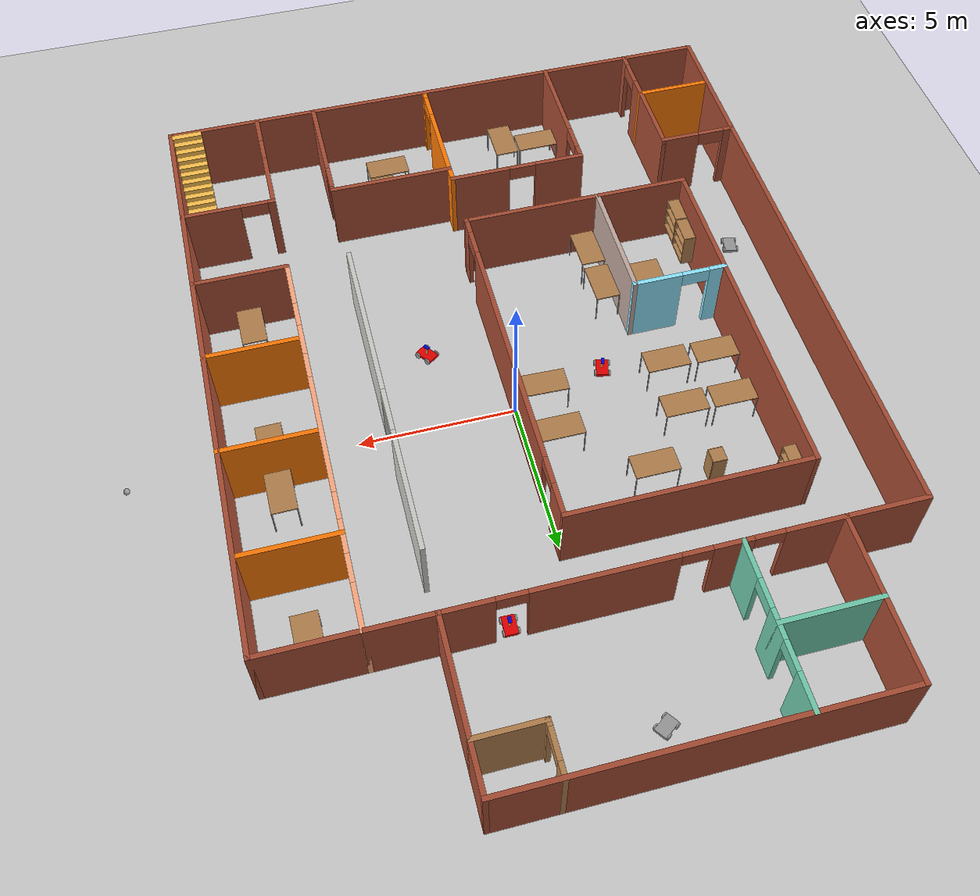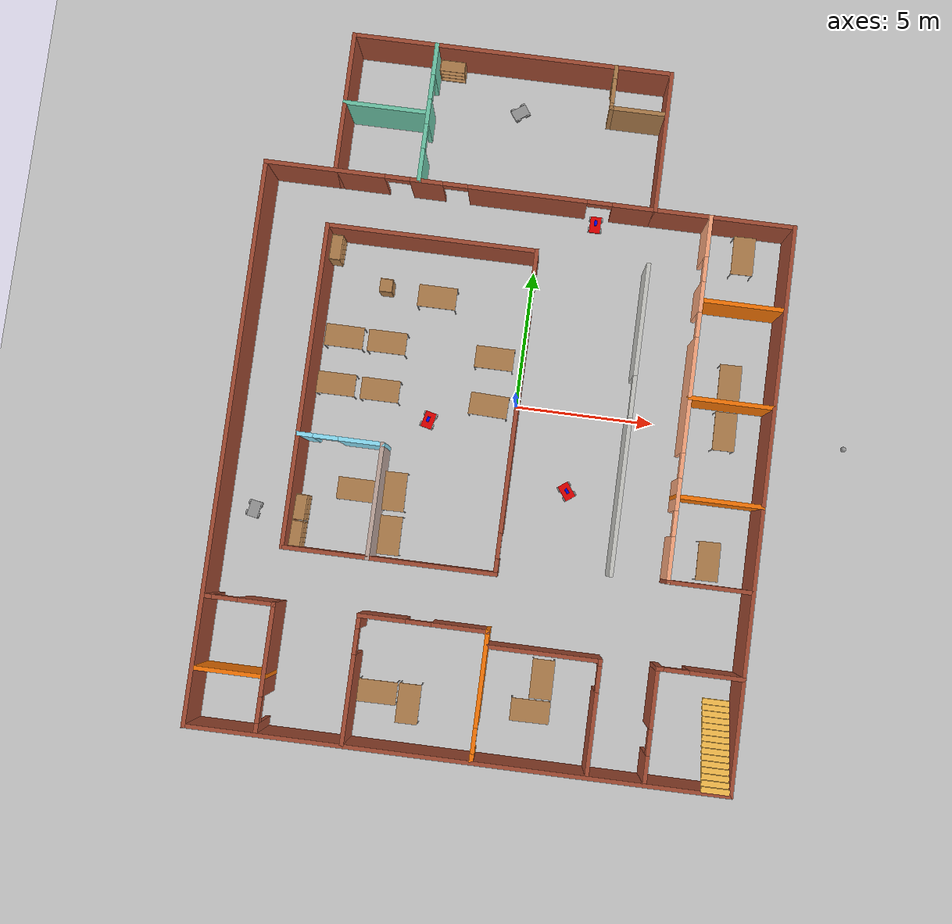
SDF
<sdf version="1.6">
 <world name="default">
  <plugin name="hello" filename="libhello.so"/>
  <light name="sun" type="directional">
   <pose>0 0 10 0 -0 0</pose>
   <diffuse>0.8 0.8 0.8 1</diffuse>
   <specular>0.1 0.1 0.1 1</specular>
   <attenuation>
    <range>1000</range>
    <constant>0.9</constant>
    <linear>0.01</linear>
    <quadratic>0.001</quadratic>
   </attenuation>
   <direction>-0.5 0.5 -1</direction>
  </light>
  <model name="ground_plane">
   <static>1</static>
   <link name="link">
    <collision name="collision">
     <geometry><plane><normal>0 0 1</normal><size>100 100</size></plane></geometry>
     <surface><friction><ode><mu>100</mu><mu2>50</mu2></ode></friction></surface>
    </collision>
    <visual name="visual">
     <cast_shadows>0</cast_shadows>
     <geometry><plane><normal>0 0 1</normal><size>100 100</size></plane></geometry>
     <material>
      <script><uri>file://media/materials/scripts/gazebo.material</uri><name>Gazebo/Grey</name></script>
     </material>
    </visual>
   </link>
  </model>
  <gravity>0 0 -9.8</gravity>
  <magnetic_field>6e-06 2.3e-05 -4.2e-05</magnetic_field>
  <atmosphere type="adiabatic"/>
  <physics name="default_physics" default="0" type="ode">
   <max_step_size>0.001</max_step_size>
   <real_time_factor>1</real_time_factor>
   <real_time_update_rate>1000</real_time_update_rate>
  </physics>
  <scene><ambient>0.4 0.4 0.4 1</ambient><background>0.7 0.7 0.7 1</background><shadows>1</shadows></scene>
  <spherical_coordinates>
   <surface_model>EARTH_WGS84</surface_model>
   <latitude_deg>0</latitude_deg>
   <longitude_deg>0</longitude_deg>
   <elevation>0</elevation>
   <heading_deg>0</heading_deg>
  </spherical_coordinates>
  <model name="MyBuilding">
   <pose>-0.452354 -0.124982 0 0 -0 0</pose>
   <link name="Stairs_0">
    <visual name="Stairs_0_Visual_0">
     <pose>8.94729 -9.5729 0.083333 0 -0 0</pose>
     <geometry><box><size>1 0.2 0.166667</size></box></geometry>
     <material>
      <script><uri>file://media/materials/scripts/gazebo.material</uri><name>Gazebo/Grey</name></script>
      <ambient>1 0.764706 0.305882 1</ambient>
     </material>
    </visual>
    <collision name="Stairs_0_Collision_0">
     <geometry><box><size>1 0.2 0.166667</size></box></geometry>
     <pose>8.94729 -9.5729 0.083333 0 -0 0</pose>
    </collision>
    <visual name="Stairs_0_Visual_1">
     <pose>8.94729 -9.7729 0.25 0 -0 0</pose>
     <geometry><box><size>1 0.2 0.166667</size></box></geometry>
     <material>
      <script><uri>file://media/materials/scripts/gazebo.material</uri><name>Gazebo/Grey</name></script>
      <ambient>1 0.764706 0.305882 1</ambient>
     </material>
    </visual>
    <collision name="Stairs_0_Collision_1">
     <geometry><box><size>1 0.2 0.166667</size></box></geometry>
     <pose>8.94729 -9.7729 0.25 0 -0 0</pose>
    </collision>
    <visual name="Stairs_0_Visual_2">
     <pose>8.94729 -9.9729 0.416667 0 -0 0</pose>
     <geometry><box><size>1 0.2 0.166667</size></box></geometry>
     <material>
      <script><uri>file://media/materials/scripts/gazebo.material</uri><name>Gazebo/Grey</name></script>
      <ambient>1 0.764706 0.305882 1</ambient>
     </material>
    </visual>
    <collision name="Stairs_0_Collision_2">
     <geometry><box><size>1 0.2 0.166667</size></box></geometry>
     <pose>8.94729 -9.9729 0.416667 0 -0 0</pose>
    </collision>
    <visual name="Stairs_0_Visual_3">
     <pose>8.94729 -10.1729 0.583333 0 -0 0</pose>
     <geometry><box><size>1 0.2 0.166667</size></box></geometry>
     <material>
      <script><uri>file://media/materials/scripts/gazebo.material</uri><name>Gazebo/Grey</name></script>
      <ambient>1 0.764706 0.305882 1</ambient>
     </material>
    </visual>
    <collision name="Stairs_0_Collision_3">
     <geometry><box><size>1 0.2 0.166667</size></box></geometry>
     <pose>8.94729 -10.1729 0.583333 0 -0 0</pose>
    </collision>
    <visual name="Stairs_0_Visual_4">
     <pose>8.94729 -10.3729 0.75 0 -0 0</pose>
     <geometry><box><size>1 0.2 0.166667</size></box></geometry>
     <material>
      <script><uri>file://media/materials/scripts/gazebo.material</uri><name>Gazebo/Grey</name></script>
      <ambient>1 0.764706 0.305882 1</ambient>
     </material>
    </visual>
    <collision name="Stairs_0_Collision_4">
     <geometry><box><size>1 0.2 0.166667</size></box></geometry>
     <pose>8.94729 -10.3729 0.75 0 -0 0</pose>
    </collision>
    <visual name="Stairs_0_Visual_5">
     <pose>8.94729 -10.5729 0.916667 0 -0 0</pose>
     <geometry><box><size>1 0.2 0.166667</size></box></geometry>
     <material>
      <script><uri>file://media/materials/scripts/gazebo.material</uri><name>Gazebo/Grey</name></script>
      <ambient>1 0.764706 0.305882 1</ambient>
     </material>
    </visual>
    <collision name="Stairs_0_Collision_5">
     <geometry><box><size>1 0.2 0.166667</size></box></geometry>
     <pose>8.94729 -10.5729 0.916667 0 -0 0</pose>
    </collision>
    <visual name="Stairs_0_Visual_6">
     <pose>8.94729 -10.7729 1.08333 0 -0 0</pose>
     <geometry><box><size>1 0.2 0.166667</size></box></geometry>
     <material>
      <script><uri>file://media/materials/scripts/gazebo.material</uri><name>Gazebo/Grey</name></script>
      <ambient>1 0.764706 0.305882 1</ambient>
     </material>
    </visual>
    <collision name="Stairs_0_Collision_6">
     <geometry><box><size>1 0.2 0.166667</size></box></geometry>
     <pose>8.94729 -10.7729 1.08333 0 -0 0</pose>
    </collision>
    <visual name="Stairs_0_Visual_7">
     <pose>8.94729 -10.9729 1.25 0 -0 0</pose>
     <geometry><box><size>1 0.2 0.166667</size></box></geometry>
     <material>
      <script><uri>file://media/materials/scripts/gazebo.material</uri><name>Gazebo/Grey</name></script>
      <ambient>1 0.764706 0.305882 1</ambient>
     </material>
    </visual>
    <collision name="Stairs_0_Collision_7">
     <geometry><box><size>1 0.2 0.166667</size></box></geometry>
     <pose>8.94729 -10.9729 1.25 0 -0 0</pose>
    </collision>
    <visual name="Stairs_0_Visual_8">
     <pose>8.94729 -11.1729 1.41667 0 -0 0</pose>
     <geometry><box><size>1 0.2 0.166667</size></box></geometry>
     <material>
      <script><uri>file://media/materials/scripts/gazebo.material</uri><name>Gazebo/Grey</name></script>
      <ambient>1 0.764706 0.305882 1</ambient>
     </material>
    </visual>
    <collision name="Stairs_0_Collision_8">
     <geometry><box><size>1 0.2 0.166667</size></box></geometry>
     <pose>8.94729 -11.1729 1.41667 0 -0 0</pose>
    </collision>
    <visual name="Stairs_0_Visual_9">
     <pose>8.94729 -11.3729 1.58333 0 -0 0</pose>
     <geometry><box><size>1 0.2 0.166667</size></box></geometry>
     <material>
      <script><uri>file://media/materials/scripts/gazebo.material</uri><name>Gazebo/Grey</name></script>
      <ambient>1 0.764706 0.305882 1</ambient>
     </material>
    </visual>
    <collision name="Stairs_0_Collision_9">
     <geometry><box><size>1 0.2 0.166667</size></box></geometry>
     <pose>8.94729 -11.3729 1.58333 0 -0 0</pose>
    </collision>
    <visual name="Stairs_0_Visual_10">
     <pose>8.94729 -11.5729 1.75 0 -0 0</pose>
     <geometry><box><size>1 0.2 0.166667</size></box></geometry>
     <material>
      <script><uri>file://media/materials/scripts/gazebo.material</uri><name>Gazebo/Grey</name></script>
      <ambient>1 0.764706 0.305882 1</ambient>
     </material>
    </visual>
    <collision name="Stairs_0_Collision_10">
     <geometry><box><size>1 0.2 0.166667</size></box></geometry>
     <pose>8.94729 -11.5729 1.75 0 -0 0</pose>
    </collision>
    <visual name="Stairs_0_Visual_11">
     <pose>8.94729 -11.7729 1.91667 0 -0 0</pose>
     <geometry><box><size>1 0.2 0.166667</size></box></geometry>
     <material>
      <script><uri>file://media/materials/scripts/gazebo.material</uri><name>Gazebo/Grey</name></script>
      <ambient>1 0.764706 0.305882 1</ambient>
     </material>
    </visual>
    <collision name="Stairs_0_Collision_11">
     <geometry><box><size>1 0.2 0.166667</size></box></geometry>
     <pose>8.94729 -11.7729 1.91667 0 -0 0</pose>
    </collision>
    <visual name="Stairs_0_Visual_12">
     <pose>8.94729 -11.9729 2.08333 0 -0 0</pose>
     <geometry><box><size>1 0.2 0.166667</size></box></geometry>
     <material>
      <script><uri>file://media/materials/scripts/gazebo.material</uri><name>Gazebo/Grey</name></script>
      <ambient>1 0.764706 0.305882 1</ambient>
     </material>
    </visual>
    <collision name="Stairs_0_Collision_12">
     <geometry><box><size>1 0.2 0.166667</size></box></geometry>
     <pose>8.94729 -11.9729 2.08333 0 -0 0</pose>
    </collision>
    <visual name="Stairs_0_Visual_13">
     <pose>8.94729 -12.1729 2.25 0 -0 0</pose>
     <geometry><box><size>1 0.2 0.166667</size></box></geometry>
     <material>
      <script><uri>file://media/materials/scripts/gazebo.material</uri><name>Gazebo/Grey</name></script>
      <ambient>1 0.764706 0.305882 1</ambient>
     </material>
    </visual>
    <collision name="Stairs_0_Collision_13">
     <geometry><box><size>1 0.2 0.166667</size></box></geometry>
     <pose>8.94729 -12.1729 2.25 0 -0 0</pose>
    </collision>
    <visual name="Stairs_0_Visual_14">
     <pose>8.94729 -12.3729 2.41667 0 -0 0</pose>
     <geometry><box><size>1 0.2 0.166667</size></box></geometry>
     <material>
      <script><uri>file://media/materials/scripts/gazebo.material</uri><name>Gazebo/Grey</name></script>
      <ambient>1 0.764706 0.305882 1</ambient>
     </material>
    </visual>
    <collision name="Stairs_0_Collision_14">
     <geometry><box><size>1 0.2 0.166667</size></box></geometry>
     <pose>8.94729 -12.3729 2.41667 0 -0 0</pose>
    </collision>
   </link>
   <link name="Wall_11">
    <collision name="Wall_11_Collision">
     <geometry><box><size>7.65008 0.15 2.5</size></box></geometry>
     <pose>0 0 1.25 0 -0 0</pose>
    </collision>
    <visual name="Wall_11_Visual">
     <pose>0 0 1.25 0 -0 0</pose>
     <geometry><box><size>7.65008 0.15 2.5</size></box></geometry>
     <material>
      <script><uri>file://media/materials/scripts/gazebo.material</uri><name>Gazebo/Bricks</name></script>
      <ambient>1 1 1 1</ambient>
     </material>
    </visual>
    <pose>-3.25 5.5 0 0 -0 0</pose>
   </link>
   <link name="Wall_13">
    <pose>0.5 -0.25 0 0 0 -1.5708</pose>
    <visual name="Wall_13_Visual_0">
     <pose>-5.25703 0 1.25 0 -0 0</pose>
     <geometry><box><size>1.13593 0.15 2.5</size></box></geometry>
     <material>
      <script><uri>file://media/materials/scripts/gazebo.material</uri><name>Gazebo/Bricks</name></script>
      <ambient>1 1 1 1</ambient>
     </material>
    </visual>
    <collision name="Wall_13_Collision_0">
     <geometry><box><size>1.13593 0.15 2.5</size></box></geometry>
     <pose>-5.25703 0 1.25 0 -0 0</pose>
    </collision>
    <visual name="Wall_13_Visual_1">
     <pose>0.255466 0 1.25 0 -0 0</pose>
     <geometry><box><size>8.08907 0.15 2.5</size></box></geometry>
     <material>
      <script><uri>file://media/materials/scripts/gazebo.material</uri><name>Gazebo/Bricks</name></script>
      <ambient>1 1 1 1</ambient>
     </material>
    </visual>
    <collision name="Wall_13_Collision_1">
     <geometry><box><size>8.08907 0.15 2.5</size></box></geometry>
     <pose>0.255466 0 1.25 0 -0 0</pose>
    </collision>
    <visual name="Wall_13_Visual_2">
     <pose>5.5125 0 1.25 0 -0 0</pose>
     <geometry><box><size>0.625 0.15 2.5</size></box></geometry>
     <material>
      <script><uri>file://media/materials/scripts/gazebo.material</uri><name>Gazebo/Bricks</name></script>
      <ambient>1 1 1 1</ambient>
     </material>
    </visual>
    <collision name="Wall_13_Collision_2">
     <geometry><box><size>0.625 0.15 2.5</size></box></geometry>
     <pose>5.5125 0 1.25 0 -0 0</pose>
    </collision>
    <visual name="Wall_13_Visual_3">
     <pose>-4.23907 0 2.25 0 -0 0</pose>
     <geometry><box><size>0.9 0.15 0.5</size></box></geometry>
     <material>
      <script><uri>file://media/materials/scripts/gazebo.material</uri><name>Gazebo/Bricks</name></script>
      <ambient>1 1 1 1</ambient>
     </material>
    </visual>
    <collision name="Wall_13_Collision_3">
     <geometry><box><size>0.9 0.15 0.5</size></box></geometry>
     <pose>-4.23907 0 2.25 0 -0 0</pose>
    </collision>
    <visual name="Wall_13_Visual_4">
     <pose>4.75 0 2.25 0 -0 0</pose>
     <geometry><box><size>0.9 0.15 0.5</size></box></geometry>
     <material>
      <script><uri>file://media/materials/scripts/gazebo.material</uri><name>Gazebo/Bricks</name></script>
      <ambient>1 1 1 1</ambient>
     </material>
    </visual>
    <collision name="Wall_13_Collision_4">
     <geometry><box><size>0.9 0.15 0.5</size></box></geometry>
     <pose>4.75 0 2.25 0 -0 0</pose>
    </collision>
   </link>
   <link name="Wall_17">
    <collision name="Wall_17_Collision">
     <geometry><box><size>4.15 0.15 2.5</size></box></geometry>
     <pose>0 0 1.25 0 -0 0</pose>
    </collision>
    <visual name="Wall_17_Visual">
     <pose>0 0 1.25 0 -0 0</pose>
     <geometry><box><size>4.15 0.15 2.5</size></box></geometry>
     <material>
      <script><uri>file://media/materials/scripts/gazebo.material</uri><name>Gazebo/Grey</name></script>
      <ambient>0.760784 0.662745 0.627451 1</ambient>
     </material>
    </visual>
    <pose>-4 -4 0 0 -0 1.5708</pose>
   </link>
   <link name="Wall_2">
    <collision name="Wall_2_Collision">
     <geometry><box><size>20.15 0.15 2.5</size></box></geometry>
     <pose>0 0 1.25 0 -0 0</pose>
    </collision>
    <visual name="Wall_2_Visual">
     <pose>0 0 1.25 0 -0 0</pose>
     <geometry><box><size>20.15 0.15 2.5</size></box></geometry>
     <material>
      <script><uri>file://media/materials/scripts/gazebo.material</uri><name>Gazebo/Bricks</name></script>
      <ambient>1 1 1 1</ambient>
     </material>
    </visual>
    <pose>-9.5 -2.5 0 0 -0 1.5708</pose>
   </link>
   <link name="Wall_20">
    <pose>-5.5 -2 0 0 -0 3.14159</pose>
    <visual name="Wall_20_Visual_0">
     <pose>-0.751088 0 1.25 0 -0 0</pose>
     <geometry><box><size>1.64782 0.15 2.5</size></box></geometry>
     <material>
      <script><uri>file://media/materials/scripts/gazebo.material</uri><name>Gazebo/Grey</name></script>
      <ambient>0.560784 0.905882 1 1</ambient>
     </material>
    </visual>
    <collision name="Wall_20_Collision_0">
     <geometry><box><size>1.64782 0.15 2.5</size></box></geometry>
     <pose>-0.751088 0 1.25 0 -0 0</pose>
    </collision>
    <visual name="Wall_20_Visual_1">
     <pose>1.27391 0 1.25 0 -0 0</pose>
     <geometry><box><size>0.602176 0.15 2.5</size></box></geometry>
     <material>
      <script><uri>file://media/materials/scripts/gazebo.material</uri><name>Gazebo/Grey</name></script>
      <ambient>0.560784 0.905882 1 1</ambient>
     </material>
    </visual>
    <collision name="Wall_20_Collision_1">
     <geometry><box><size>0.602176 0.15 2.5</size></box></geometry>
     <pose>1.27391 0 1.25 0 -0 0</pose>
    </collision>
    <visual name="Wall_20_Visual_2">
     <pose>0.522824 0 2.25 0 -0 0</pose>
     <geometry><box><size>0.9 0.15 0.5</size></box></geometry>
     <material>
      <script><uri>file://media/materials/scripts/gazebo.material</uri><name>Gazebo/Grey</name></script>
      <ambient>0.560784 0.905882 1 1</ambient>
     </material>
    </visual>
    <collision name="Wall_20_Collision_2">
     <geometry><box><size>0.9 0.15 0.5</size></box></geometry>
     <pose>0.522824 0 2.25 0 -0 0</pose>
    </collision>
   </link>
   <link name="Wall_22">
    <pose>-2.5 7.5 0 0 -0 0</pose>
    <visual name="Wall_22_Visual_0">
     <pose>-4.89486 0 1.25 0 -0 0</pose>
     <geometry><box><size>4.36028 0.15 2.5</size></box></geometry>
     <material>
      <script><uri>file://media/materials/scripts/gazebo.material</uri><name>Gazebo/Bricks</name></script>
      <ambient>1 1 1 1</ambient>
     </material>
    </visual>
    <collision name="Wall_22_Collision_0">
     <geometry><box><size>4.36028 0.15 2.5</size></box></geometry>
     <pose>-4.89486 0 1.25 0 -0 0</pose>
    </collision>
    <visual name="Wall_22_Visual_1">
     <pose>-1.22142 0 1.25 0 -0 0</pose>
     <geometry><box><size>1.1866 0.15 2.5</size></box></geometry>
     <material>
      <script><uri>file://media/materials/scripts/gazebo.material</uri><name>Gazebo/Bricks</name></script>
      <ambient>1 1 1 1</ambient>
     </material>
    </visual>
    <collision name="Wall_22_Collision_1">
     <geometry><box><size>1.1866 0.15 2.5</size></box></geometry>
     <pose>-1.22142 0 1.25 0 -0 0</pose>
    </collision>
    <visual name="Wall_22_Visual_2">
     <pose>2.4158 0 1.25 0 -0 0</pose>
     <geometry><box><size>4.28784 0.15 2.5</size></box></geometry>
     <material>
      <script><uri>file://media/materials/scripts/gazebo.material</uri><name>Gazebo/Bricks</name></script>
      <ambient>1 1 1 1</ambient>
     </material>
    </visual>
    <collision name="Wall_22_Collision_2">
     <geometry><box><size>4.28784 0.15 2.5</size></box></geometry>
     <pose>2.4158 0 1.25 0 -0 0</pose>
    </collision>
    <visual name="Wall_22_Visual_3">
     <pose>6.26736 0 1.25 0 -0 0</pose>
     <geometry><box><size>1.61528 0.15 2.5</size></box></geometry>
     <material>
      <script><uri>file://media/materials/scripts/gazebo.material</uri><name>Gazebo/Bricks</name></script>
      <ambient>1 1 1 1</ambient>
     </material>
    </visual>
    <collision name="Wall_22_Collision_3">
     <geometry><box><size>1.61528 0.15 2.5</size></box></geometry>
     <pose>6.26736 0 1.25 0 -0 0</pose>
    </collision>
    <visual name="Wall_22_Visual_4">
     <pose>-2.26472 0 2.25 0 -0 0</pose>
     <geometry><box><size>0.9 0.15 0.5</size></box></geometry>
     <material>
      <script><uri>file://media/materials/scripts/gazebo.material</uri><name>Gazebo/Bricks</name></script>
      <ambient>1 1 1 1</ambient>
     </material>
    </visual>
    <collision name="Wall_22_Collision_4">
     <geometry><box><size>0.9 0.15 0.5</size></box></geometry>
     <pose>-2.26472 0 2.25 0 -0 0</pose>
    </collision>
    <visual name="Wall_22_Visual_5">
     <pose>-0.17812 0 2.25 0 -0 0</pose>
     <geometry><box><size>0.9 0.15 0.5</size></box></geometry>
     <material>
      <script><uri>file://media/materials/scripts/gazebo.material</uri><name>Gazebo/Bricks</name></script>
      <ambient>1 1 1 1</ambient>
     </material>
    </visual>
    <collision name="Wall_22_Collision_5">
     <geometry><box><size>0.9 0.15 0.5</size></box></geometry>
     <pose>-0.17812 0 2.25 0 -0 0</pose>
    </collision>
    <visual name="Wall_22_Visual_6">
     <pose>5.00972 0 2.25 0 -0 0</pose>
     <geometry><box><size>0.9 0.15 0.5</size></box></geometry>
     <material>
      <script><uri>file://media/materials/scripts/gazebo.material</uri><name>Gazebo/Bricks</name></script>
      <ambient>1 1 1 1</ambient>
     </material>
    </visual>
    <collision name="Wall_22_Collision_6">
     <geometry><box><size>0.9 0.15 0.5</size></box></geometry>
     <pose>5.00972 0 2.25 0 -0 0</pose>
    </collision>
   </link>
   <link name="Wall_23">
    <collision name="Wall_23_Collision">
     <geometry><box><size>5.15 0.15 2.5</size></box></geometry>
     <pose>0 0 1.25 0 -0 0</pose>
    </collision>
    <visual name="Wall_23_Visual">
     <pose>0 0 1.25 0 -0 0</pose>
     <geometry><box><size>5.15 0.15 2.5</size></box></geometry>
     <material>
      <script><uri>file://media/materials/scripts/gazebo.material</uri><name>Gazebo/Bricks</name></script>
      <ambient>1 1 1 1</ambient>
     </material>
    </visual>
    <pose>4.5 10 0 0 -0 1.5708</pose>
   </link>
   <link name="Wall_24">
    <collision name="Wall_24_Collision">
     <geometry><box><size>11.65 0.15 2.5</size></box></geometry>
     <pose>0 0 1.25 0 -0 0</pose>
    </collision>
    <visual name="Wall_24_Visual">
     <pose>0 0 1.25 0 -0 0</pose>
     <geometry><box><size>11.65 0.15 2.5</size></box></geometry>
     <material>
      <script><uri>file://media/materials/scripts/gazebo.material</uri><name>Gazebo/Bricks</name></script>
      <ambient>1 1 1 1</ambient>
     </material>
    </visual>
    <pose>-1.25 12.5 0 0 -0 3.14159</pose>
   </link>
   <link name="Wall_25">
    <collision name="Wall_25_Collision">
     <geometry><box><size>5.15 0.15 2.5</size></box></geometry>
     <pose>0 0 1.25 0 -0 0</pose>
    </collision>
    <visual name="Wall_25_Visual">
     <pose>0 0 1.25 0 -0 0</pose>
     <geometry><box><size>5.15 0.15 2.5</size></box></geometry>
     <material>
      <script><uri>file://media/materials/scripts/gazebo.material</uri><name>Gazebo/Bricks</name></script>
      <ambient>1 1 1 1</ambient>
     </material>
    </visual>
    <pose>-7 10 0 0 0 -1.5708</pose>
   </link>
   <link name="Wall_27">
    <pose>4.5 0 0 0 -0 1.5708</pose>
    <visual name="Wall_27_Visual_0">
     <pose>-2.77301 0 1.25 0 -0 0</pose>
     <geometry><box><size>5.60398 0.15 2.5</size></box></geometry>
     <material>
      <script><uri>file://media/materials/scripts/gazebo.material</uri><name>Gazebo/CeilingTiled</name></script>
      <ambient>0.560784 0.905882 1 1</ambient>
     </material>
    </visual>
    <collision name="Wall_27_Collision_0">
     <geometry><box><size>5.60398 0.15 2.5</size></box></geometry>
     <pose>-2.77301 0 1.25 0 -0 0</pose>
    </collision>
    <visual name="Wall_27_Visual_1">
     <pose>3.55199 0 1.25 0 -0 0</pose>
     <geometry><box><size>4.04602 0.15 2.5</size></box></geometry>
     <material>
      <script><uri>file://media/materials/scripts/gazebo.material</uri><name>Gazebo/CeilingTiled</name></script>
      <ambient>0.560784 0.905882 1 1</ambient>
     </material>
    </visual>
    <collision name="Wall_27_Collision_1">
     <geometry><box><size>4.04602 0.15 2.5</size></box></geometry>
     <pose>3.55199 0 1.25 0 -0 0</pose>
    </collision>
    <visual name="Wall_27_Visual_2">
     <pose>0.778981 0 2.25 0 -0 0</pose>
     <geometry><box><size>1.5 0.15 0.5</size></box></geometry>
     <material>
      <script><uri>file://media/materials/scripts/gazebo.material</uri><name>Gazebo/CeilingTiled</name></script>
      <ambient>0.560784 0.905882 1 1</ambient>
     </material>
    </visual>
    <collision name="Wall_27_Collision_2">
     <geometry><box><size>1.5 0.15 0.5</size></box></geometry>
     <pose>0.778981 0 2.25 0 -0 0</pose>
    </collision>
   </link>
   <link name="Wall_30">
    <pose>0.5 -10.25 0 0 0 -1.5708</pose>
    <visual name="Wall_30_Visual_0">
     <pose>-0.641869 0 1.25 0 -0 0</pose>
     <geometry><box><size>3.36626 0.15 2.5</size></box></geometry>
     <material>
      <script><uri>file://media/materials/scripts/gazebo.material</uri><name>Gazebo/Grey</name></script>
      <ambient>0.996078 0.47451 0.0196078 1</ambient>
     </material>
    </visual>
    <collision name="Wall_30_Collision_0">
     <geometry><box><size>3.36626 0.15 2.5</size></box></geometry>
     <pose>-0.641869 0 1.25 0 -0 0</pose>
    </collision>
    <visual name="Wall_30_Visual_1">
     <pose>2.13313 0 1.25 0 -0 0</pose>
     <geometry><box><size>0.383739 0.15 2.5</size></box></geometry>
     <material>
      <script><uri>file://media/materials/scripts/gazebo.material</uri><name>Gazebo/Grey</name></script>
      <ambient>0.996078 0.47451 0.0196078 1</ambient>
     </material>
    </visual>
    <collision name="Wall_30_Collision_1">
     <geometry><box><size>0.383739 0.15 2.5</size></box></geometry>
     <pose>2.13313 0 1.25 0 -0 0</pose>
    </collision>
    <visual name="Wall_30_Visual_2">
     <pose>1.49126 0 2.25 0 -0 0</pose>
     <geometry><box><size>0.9 0.15 0.5</size></box></geometry>
     <material>
      <script><uri>file://media/materials/scripts/gazebo.material</uri><name>Gazebo/Grey</name></script>
      <ambient>0.996078 0.47451 0.0196078 1</ambient>
     </material>
    </visual>
    <collision name="Wall_30_Collision_2">
     <geometry><box><size>0.9 0.15 0.5</size></box></geometry>
     <pose>1.49126 0 2.25 0 -0 0</pose>
    </collision>
   </link>
   <link name="Wall_32">
    <pose>6.5 1 0 0 -0 1.5708</pose>
    <visual name="Wall_32_Visual_0">
     <pose>-5.73988 0 1.25 0 -0 0</pose>
     <geometry><box><size>1.67024 0.15 2.5</size></box></geometry>
     <material>
      <script><uri>file://media/materials/scripts/gazebo.material</uri><name>Gazebo/Grey</name></script>
      <ambient>1 0.666667 0.498039 1</ambient>
     </material>
    </visual>
    <collision name="Wall_32_Collision_0">
     <geometry><box><size>1.67024 0.15 2.5</size></box></geometry>
     <pose>-5.73988 0 1.25 0 -0 0</pose>
    </collision>
    <visual name="Wall_32_Visual_1">
     <pose>-3.43123 0 1.25 0 -0 0</pose>
     <geometry><box><size>1.14705 0.15 2.5</size></box></geometry>
     <material>
      <script><uri>file://media/materials/scripts/gazebo.material</uri><name>Gazebo/Grey</name></script>
      <ambient>1 0.666667 0.498039 1</ambient>
     </material>
    </visual>
    <collision name="Wall_32_Collision_1">
     <geometry><box><size>1.14705 0.15 2.5</size></box></geometry>
     <pose>-3.43123 0 1.25 0 -0 0</pose>
    </collision>
    <visual name="Wall_32_Visual_2">
     <pose>0.104585 0 1.25 0 -0 0</pose>
     <geometry><box><size>4.12458 0.15 2.5</size></box></geometry>
     <material>
      <script><uri>file://media/materials/scripts/gazebo.material</uri><name>Gazebo/Grey</name></script>
      <ambient>1 0.666667 0.498039 1</ambient>
     </material>
    </visual>
    <collision name="Wall_32_Collision_2">
     <geometry><box><size>4.12458 0.15 2.5</size></box></geometry>
     <pose>0.104585 0 1.25 0 -0 0</pose>
    </collision>
    <visual name="Wall_32_Visual_3">
     <pose>3.61714 0 1.25 0 -0 0</pose>
     <geometry><box><size>1.10053 0.15 2.5</size></box></geometry>
     <material>
      <script><uri>file://media/materials/scripts/gazebo.material</uri><name>Gazebo/Grey</name></script>
      <ambient>1 0.666667 0.498039 1</ambient>
     </material>
    </visual>
    <collision name="Wall_32_Collision_3">
     <geometry><box><size>1.10053 0.15 2.5</size></box></geometry>
     <pose>3.61714 0 1.25 0 -0 0</pose>
    </collision>
    <visual name="Wall_32_Visual_4">
     <pose>5.8212 0 1.25 0 -0 0</pose>
     <geometry><box><size>1.5076 0.15 2.5</size></box></geometry>
     <material>
      <script><uri>file://media/materials/scripts/gazebo.material</uri><name>Gazebo/Grey</name></script>
      <ambient>1 0.666667 0.498039 1</ambient>
     </material>
    </visual>
    <collision name="Wall_32_Collision_4">
     <geometry><box><size>1.5076 0.15 2.5</size></box></geometry>
     <pose>5.8212 0 1.25 0 -0 0</pose>
    </collision>
    <visual name="Wall_32_Visual_5">
     <pose>-4.45476 0 2.25 0 -0 0</pose>
     <geometry><box><size>0.9 0.15 0.5</size></box></geometry>
     <material>
      <script><uri>file://media/materials/scripts/gazebo.material</uri><name>Gazebo/Grey</name></script>
      <ambient>1 0.666667 0.498039 1</ambient>
     </material>
    </visual>
    <collision name="Wall_32_Collision_5">
     <geometry><box><size>0.9 0.15 0.5</size></box></geometry>
     <pose>-4.45476 0 2.25 0 -0 0</pose>
    </collision>
    <visual name="Wall_32_Visual_6">
     <pose>-2.40771 0 2.25 0 -0 0</pose>
     <geometry><box><size>0.9 0.15 0.5</size></box></geometry>
     <material>
      <script><uri>file://media/materials/scripts/gazebo.material</uri><name>Gazebo/Grey</name></script>
      <ambient>1 0.666667 0.498039 1</ambient>
     </material>
    </visual>
    <collision name="Wall_32_Collision_6">
     <geometry><box><size>0.9 0.15 0.5</size></box></geometry>
     <pose>-2.40771 0 2.25 0 -0 0</pose>
    </collision>
    <visual name="Wall_32_Visual_7">
     <pose>2.61688 0 2.25 0 -0 0</pose>
     <geometry><box><size>0.9 0.15 0.5</size></box></geometry>
     <material>
      <script><uri>file://media/materials/scripts/gazebo.material</uri><name>Gazebo/Grey</name></script>
      <ambient>1 0.666667 0.498039 1</ambient>
     </material>
    </visual>
    <collision name="Wall_32_Collision_7">
     <geometry><box><size>0.9 0.15 0.5</size></box></geometry>
     <pose>2.61688 0 2.25 0 -0 0</pose>
    </collision>
    <visual name="Wall_32_Visual_8">
     <pose>4.6174 0 2.25 0 -0 0</pose>
     <geometry><box><size>0.9 0.15 0.5</size></box></geometry>
     <material>
      <script><uri>file://media/materials/scripts/gazebo.material</uri><name>Gazebo/Grey</name></script>
      <ambient>1 0.666667 0.498039 1</ambient>
     </material>
    </visual>
    <collision name="Wall_32_Collision_8">
     <geometry><box><size>0.9 0.15 0.5</size></box></geometry>
     <pose>4.6174 0 2.25 0 -0 0</pose>
    </collision>
   </link>
   <link name="Wall_34">
    <collision name="Wall_34_Collision">
     <geometry><box><size>20.15 0.15 2.5</size></box></geometry>
     <pose>0 0 1.25 0 -0 0</pose>
    </collision>
    <visual name="Wall_34_Visual">
     <pose>0 0 1.25 0 -0 0</pose>
     <geometry><box><size>20.15 0.15 2.5</size></box></geometry>
     <material>
      <script><uri>file://media/materials/scripts/gazebo.material</uri><name>Gazebo/Bricks</name></script>
      <ambient>1 1 1 1</ambient>
     </material>
    </visual>
    <pose>9.5 -2.5 0 0 0 -1.5708</pose>
   </link>
   <link name="Wall_36">
    <collision name="Wall_36_Collision">
     <geometry><box><size>5.15 0.15 2.5</size></box></geometry>
     <pose>0 0 1.25 0 -0 0</pose>
    </collision>
    <visual name="Wall_36_Visual">
     <pose>0 0 1.25 0 -0 0</pose>
     <geometry><box><size>5.15 0.15 2.5</size></box></geometry>
     <material>
      <script><uri>file://media/materials/scripts/gazebo.material</uri><name>Gazebo/Bricks</name></script>
      <ambient>1 1 1 1</ambient>
     </material>
    </visual>
    <pose>7 7.5 0 0 -0 0</pose>
   </link>
   <link name="Wall_38">
    <collision name="Wall_38_Collision">
     <geometry><box><size>3.15 0.15 2.5</size></box></geometry>
     <pose>0 0 1.25 0 -0 0</pose>
    </collision>
    <visual name="Wall_38_Visual">
     <pose>0 0 1.25 0 -0 0</pose>
     <geometry><box><size>3.15 0.15 2.5</size></box></geometry>
     <material>
      <script><uri>file://media/materials/scripts/gazebo.material</uri><name>Gazebo/Bricks</name></script>
      <ambient>1 1 1 1</ambient>
     </material>
    </visual>
    <pose>8 -5.5 0 0 -0 0</pose>
   </link>
   <link name="Wall_4">
    <collision name="Wall_4_Collision">
     <geometry><box><size>19.15 0.15 2.5</size></box></geometry>
     <pose>0 0 1.25 0 -0 0</pose>
    </collision>
    <visual name="Wall_4_Visual">
     <pose>0 0 1.25 0 -0 0</pose>
     <geometry><box><size>19.15 0.15 2.5</size></box></geometry>
     <material>
      <script><uri>file://media/materials/scripts/gazebo.material</uri><name>Gazebo/Bricks</name></script>
      <ambient>1 1 1 1</ambient>
     </material>
    </visual>
    <pose>0 -12.5 0 0 -0 0</pose>
   </link>
   <link name="Wall_40">
    <pose>8 -8.5 0 0 -0 3.14159</pose>
    <visual name="Wall_40_Visual_0">
     <pose>-0.584222 0 1.25 0 -0 0</pose>
     <geometry><box><size>1.98156 0.15 2.5</size></box></geometry>
     <material>
      <script><uri>file://media/materials/scripts/gazebo.material</uri><name>Gazebo/Bricks</name></script>
      <ambient>1 1 1 1</ambient>
     </material>
    </visual>
    <collision name="Wall_40_Collision_0">
     <geometry><box><size>1.98156 0.15 2.5</size></box></geometry>
     <pose>-0.584222 0 1.25 0 -0 0</pose>
    </collision>
    <visual name="Wall_40_Visual_1">
     <pose>1.44078 0 1.25 0 -0 0</pose>
     <geometry><box><size>0.268443 0.15 2.5</size></box></geometry>
     <material>
      <script><uri>file://media/materials/scripts/gazebo.material</uri><name>Gazebo/Bricks</name></script>
      <ambient>1 1 1 1</ambient>
     </material>
    </visual>
    <collision name="Wall_40_Collision_1">
     <geometry><box><size>0.268443 0.15 2.5</size></box></geometry>
     <pose>1.44078 0 1.25 0 -0 0</pose>
    </collision>
    <visual name="Wall_40_Visual_2">
     <pose>0.856557 0 2.25 0 -0 0</pose>
     <geometry><box><size>0.9 0.15 0.5</size></box></geometry>
     <material>
      <script><uri>file://media/materials/scripts/gazebo.material</uri><name>Gazebo/Bricks</name></script>
      <ambient>1 1 1 1</ambient>
     </material>
    </visual>
    <collision name="Wall_40_Collision_2">
     <geometry><box><size>0.9 0.15 0.5</size></box></geometry>
     <pose>0.856557 0 2.25 0 -0 0</pose>
    </collision>
   </link>
   <link name="Wall_41">
    <pose>6.5 -10.5 0 0 0 -1.5708</pose>
    <visual name="Wall_41_Visual_0">
     <pose>-0.993422 0 1.25 0 -0 0</pose>
     <geometry><box><size>2.16316 0.15 2.5</size></box></geometry>
     <material>
      <script><uri>file://media/materials/scripts/gazebo.material</uri><name>Gazebo/Bricks</name></script>
      <ambient>1 1 1 1</ambient>
     </material>
    </visual>
    <collision name="Wall_41_Collision_0">
     <geometry><box><size>2.16316 0.15 2.5</size></box></geometry>
     <pose>-0.993422 0 1.25 0 -0 0</pose>
    </collision>
    <visual name="Wall_41_Visual_1">
     <pose>1.53158 0 1.25 0 -0 0</pose>
     <geometry><box><size>1.08684 0.15 2.5</size></box></geometry>
     <material>
      <script><uri>file://media/materials/scripts/gazebo.material</uri><name>Gazebo/Bricks</name></script>
      <ambient>1 1 1 1</ambient>
     </material>
    </visual>
    <collision name="Wall_41_Collision_1">
     <geometry><box><size>1.08684 0.15 2.5</size></box></geometry>
     <pose>1.53158 0 1.25 0 -0 0</pose>
    </collision>
    <visual name="Wall_41_Visual_2">
     <pose>0.538157 0 2.25 0 -0 0</pose>
     <geometry><box><size>0.9 0.15 0.5</size></box></geometry>
     <material>
      <script><uri>file://media/materials/scripts/gazebo.material</uri><name>Gazebo/Bricks</name></script>
      <ambient>1 1 1 1</ambient>
     </material>
    </visual>
    <collision name="Wall_41_Collision_2">
     <geometry><box><size>0.9 0.15 0.5</size></box></geometry>
     <pose>0.538157 0 2.25 0 -0 0</pose>
    </collision>
   </link>
   <link name="Wall_43">
    <collision name="Wall_43_Collision">
     <geometry><box><size>4.15 0.15 2.5</size></box></geometry>
     <pose>0 0 1.25 0 -0 0</pose>
    </collision>
    <visual name="Wall_43_Visual">
     <pose>0 0 1.25 0 -0 0</pose>
     <geometry><box><size>4.15 0.15 2.5</size></box></geometry>
     <material>
      <script><uri>file://media/materials/scripts/gazebo.material</uri><name>Gazebo/Bricks</name></script>
      <ambient>1 1 1 1</ambient>
     </material>
    </visual>
    <pose>2.5 -8.5 0 0 -0 0</pose>
   </link>
   <link name="Wall_44">
    <pose>4.5 -10.5 0 0 0 -1.5708</pose>
    <visual name="Wall_44_Visual_0">
     <pose>-1.9526 0 1.25 0 -0 0</pose>
     <geometry><box><size>0.244488 0.15 2.5</size></box></geometry>
     <material>
      <script><uri>file://media/materials/scripts/gazebo.material</uri><name>Gazebo/Bricks</name></script>
      <ambient>1 1 1 1</ambient>
     </material>
    </visual>
    <collision name="Wall_44_Collision_0">
     <geometry><box><size>0.244488 0.15 2.5</size></box></geometry>
     <pose>-1.9526 0 1.25 0 -0 0</pose>
    </collision>
    <visual name="Wall_44_Visual_1">
     <pose>0.572244 0 1.25 0 -0 0</pose>
     <geometry><box><size>3.00521 0.15 2.5</size></box></geometry>
     <material>
      <script><uri>file://media/materials/scripts/gazebo.material</uri><name>Gazebo/Bricks</name></script>
      <ambient>1 1 1 1</ambient>
     </material>
    </visual>
    <collision name="Wall_44_Collision_1">
     <geometry><box><size>3.00521 0.15 2.5</size></box></geometry>
     <pose>0.572244 0 1.25 0 -0 0</pose>
    </collision>
    <visual name="Wall_44_Visual_2">
     <pose>-1.38036 0 2.25 0 -0 0</pose>
     <geometry><box><size>0.9 0.15 0.5</size></box></geometry>
     <material>
      <script><uri>file://media/materials/scripts/gazebo.material</uri><name>Gazebo/Bricks</name></script>
      <ambient>1 1 1 1</ambient>
     </material>
    </visual>
    <collision name="Wall_44_Collision_2">
     <geometry><box><size>0.9 0.15 0.5</size></box></geometry>
     <pose>-1.38036 0 2.25 0 -0 0</pose>
    </collision>
   </link>
   <link name="Wall_46">
    <collision name="Wall_46_Collision">
     <geometry><box><size>3.15 0.15 2.5</size></box></geometry>
     <pose>0 0 1.25 0 -0 0</pose>
    </collision>
    <visual name="Wall_46_Visual">
     <pose>0 0 1.25 0 -0 0</pose>
     <geometry><box><size>3.15 0.15 2.5</size></box></geometry>
     <material>
      <script><uri>file://media/materials/scripts/gazebo.material</uri><name>Gazebo/Grey</name></script>
      <ambient>0.996078 0.47451 0.0196078 1</ambient>
     </material>
    </visual>
    <pose>8 -2.5 0 0 -0 0</pose>
   </link>
   <link name="Wall_48">
    <collision name="Wall_48_Collision">
     <geometry><box><size>3.15 0.15 2.5</size></box></geometry>
     <pose>0 0 1.25 0 -0 0</pose>
    </collision>
    <visual name="Wall_48_Visual">
     <pose>0 0 1.25 0 -0 0</pose>
     <geometry><box><size>3.15 0.15 2.5</size></box></geometry>
     <material>
      <script><uri>file://media/materials/scripts/gazebo.material</uri><name>Gazebo/Grey</name></script>
      <ambient>0.996078 0.47451 0.0196078 1</ambient>
     </material>
    </visual>
    <pose>8 1 0 0 -0 0</pose>
   </link>
   <link name="Wall_50">
    <collision name="Wall_50_Collision">
     <geometry><box><size>3.15 0.15 2.5</size></box></geometry>
     <pose>0 0 1.25 0 -0 0</pose>
    </collision>
    <visual name="Wall_50_Visual">
     <pose>0 0 1.25 0 -0 0</pose>
     <geometry><box><size>3.15 0.15 2.5</size></box></geometry>
     <material>
      <script><uri>file://media/materials/scripts/gazebo.material</uri><name>Gazebo/Grey</name></script>
      <ambient>0.996078 0.47451 0.0196078 1</ambient>
     </material>
    </visual>
    <pose>8 4.5 0 0 -0 0</pose>
   </link>
   <link name="Wall_52">
    <pose>-8.25 -8 0 0 -0 0</pose>
    <visual name="Wall_52_Visual_0">
     <pose>-1.12311 0 1.25 0 -0 0</pose>
     <geometry><box><size>0.403789 0.15 2.5</size></box></geometry>
     <material>
      <script><uri>file://media/materials/scripts/gazebo.material</uri><name>Gazebo/Bricks</name></script>
      <ambient>1 1 1 1</ambient>
     </material>
    </visual>
    <collision name="Wall_52_Collision_0">
     <geometry><box><size>0.403789 0.15 2.5</size></box></geometry>
     <pose>-1.12311 0 1.25 0 -0 0</pose>
    </collision>
    <visual name="Wall_52_Visual_1">
     <pose>0.651894 0 1.25 0 -0 0</pose>
     <geometry><box><size>1.34621 0.15 2.5</size></box></geometry>
     <material>
      <script><uri>file://media/materials/scripts/gazebo.material</uri><name>Gazebo/Bricks</name></script>
      <ambient>1 1 1 1</ambient>
     </material>
    </visual>
    <collision name="Wall_52_Collision_1">
     <geometry><box><size>1.34621 0.15 2.5</size></box></geometry>
     <pose>0.651894 0 1.25 0 -0 0</pose>
    </collision>
    <visual name="Wall_52_Visual_2">
     <pose>-0.471211 0 2.25 0 -0 0</pose>
     <geometry><box><size>0.9 0.15 0.5</size></box></geometry>
     <material>
      <script><uri>file://media/materials/scripts/gazebo.material</uri><name>Gazebo/Bricks</name></script>
      <ambient>1 1 1 1</ambient>
     </material>
    </visual>
    <collision name="Wall_52_Collision_2">
     <geometry><box><size>0.9 0.15 0.5</size></box></geometry>
     <pose>-0.471211 0 2.25 0 -0 0</pose>
    </collision>
   </link>
   <link name="Wall_53">
    <pose>-7 -10.25 0 0 0 -1.5708</pose>
    <visual name="Wall_53_Visual_0">
     <pose>-0.691016 0 1.25 0 -0 0</pose>
     <geometry><box><size>3.26797 0.15 2.5</size></box></geometry>
     <material>
      <script><uri>file://media/materials/scripts/gazebo.material</uri><name>Gazebo/Bricks</name></script>
      <ambient>1 1 1 1</ambient>
     </material>
    </visual>
    <collision name="Wall_53_Collision_0">
     <geometry><box><size>3.26797 0.15 2.5</size></box></geometry>
     <pose>-0.691016 0 1.25 0 -0 0</pose>
    </collision>
    <visual name="Wall_53_Visual_1">
     <pose>2.08398 0 1.25 0 -0 0</pose>
     <geometry><box><size>0.482033 0.15 2.5</size></box></geometry>
     <material>
      <script><uri>file://media/materials/scripts/gazebo.material</uri><name>Gazebo/Bricks</name></script>
      <ambient>1 1 1 1</ambient>
     </material>
    </visual>
    <collision name="Wall_53_Collision_1">
     <geometry><box><size>0.482033 0.15 2.5</size></box></geometry>
     <pose>2.08398 0 1.25 0 -0 0</pose>
    </collision>
    <visual name="Wall_53_Visual_2">
     <pose>1.39297 0 2.25 0 -0 0</pose>
     <geometry><box><size>0.9 0.15 0.5</size></box></geometry>
     <material>
      <script><uri>file://media/materials/scripts/gazebo.material</uri><name>Gazebo/Bricks</name></script>
      <ambient>1 1 1 1</ambient>
     </material>
    </visual>
    <collision name="Wall_53_Collision_2">
     <geometry><box><size>0.9 0.15 0.5</size></box></geometry>
     <pose>1.39297 0 2.25 0 -0 0</pose>
    </collision>
   </link>
   <link name="Wall_55">
    <pose>-1.75 -8 0 0 -0 3.14159</pose>
    <visual name="Wall_55_Visual_0">
     <pose>-1.29796 0 1.25 0 -0 0</pose>
     <geometry><box><size>2.05409 0.15 2.5</size></box></geometry>
     <material>
      <script><uri>file://media/materials/scripts/gazebo.material</uri><name>Gazebo/Bricks</name></script>
      <ambient>1 1 1 1</ambient>
     </material>
    </visual>
    <collision name="Wall_55_Collision_0">
     <geometry><box><size>2.05409 0.15 2.5</size></box></geometry>
     <pose>-1.29796 0 1.25 0 -0 0</pose>
    </collision>
    <visual name="Wall_55_Visual_1">
     <pose>1.47704 0 1.25 0 -0 0</pose>
     <geometry><box><size>1.69592 0.15 2.5</size></box></geometry>
     <material>
      <script><uri>file://media/materials/scripts/gazebo.material</uri><name>Gazebo/Bricks</name></script>
      <ambient>1 1 1 1</ambient>
     </material>
    </visual>
    <collision name="Wall_55_Collision_1">
     <geometry><box><size>1.69592 0.15 2.5</size></box></geometry>
     <pose>1.47704 0 1.25 0 -0 0</pose>
    </collision>
    <visual name="Wall_55_Visual_2">
     <pose>0.179085 0 2.25 0 -0 0</pose>
     <geometry><box><size>0.9 0.15 0.5</size></box></geometry>
     <material>
      <script><uri>file://media/materials/scripts/gazebo.material</uri><name>Gazebo/Bricks</name></script>
      <ambient>1 1 1 1</ambient>
     </material>
    </visual>
    <collision name="Wall_55_Collision_2">
     <geometry><box><size>0.9 0.15 0.5</size></box></geometry>
     <pose>0.179085 0 2.25 0 -0 0</pose>
    </collision>
   </link>
   <link name="Wall_56">
    <pose>-4 -10.25 0 0 0 -1.5708</pose>
    <visual name="Wall_56_Visual_0">
     <pose>-2.05968 0 1.25 0 -0 0</pose>
     <geometry><box><size>0.530629 0.15 2.5</size></box></geometry>
     <material>
      <script><uri>file://media/materials/scripts/gazebo.material</uri><name>Gazebo/Bricks</name></script>
      <ambient>1 1 1 1</ambient>
     </material>
    </visual>
    <collision name="Wall_56_Collision_0">
     <geometry><box><size>0.530629 0.15 2.5</size></box></geometry>
     <pose>-2.05968 0 1.25 0 -0 0</pose>
    </collision>
    <visual name="Wall_56_Visual_1">
     <pose>0.715315 0 1.25 0 -0 0</pose>
     <geometry><box><size>3.21937 0.15 2.5</size></box></geometry>
     <material>
      <script><uri>file://media/materials/scripts/gazebo.material</uri><name>Gazebo/Bricks</name></script>
      <ambient>1 1 1 1</ambient>
     </material>
    </visual>
    <collision name="Wall_56_Collision_1">
     <geometry><box><size>3.21937 0.15 2.5</size></box></geometry>
     <pose>0.715315 0 1.25 0 -0 0</pose>
    </collision>
    <visual name="Wall_56_Visual_2">
     <pose>-1.34437 0 2.25 0 -0 0</pose>
     <geometry><box><size>0.9 0.15 0.5</size></box></geometry>
     <material>
      <script><uri>file://media/materials/scripts/gazebo.material</uri><name>Gazebo/Bricks</name></script>
      <ambient>1 1 1 1</ambient>
     </material>
    </visual>
    <collision name="Wall_56_Collision_2">
     <geometry><box><size>0.9 0.15 0.5</size></box></geometry>
     <pose>-1.34437 0 2.25 0 -0 0</pose>
    </collision>
   </link>
   <link name="Wall_58">
    <collision name="Wall_58_Collision">
     <geometry><box><size>2.65 0.15 2.5</size></box></geometry>
     <pose>0 0 1.25 0 -0 0</pose>
    </collision>
    <visual name="Wall_58_Visual">
     <pose>0 0 1.25 0 -0 0</pose>
     <geometry><box><size>2.65 0.15 2.5</size></box></geometry>
     <material>
      <script><uri>file://media/materials/scripts/gazebo.material</uri><name>Gazebo/Grey</name></script>
      <ambient>0.996078 0.47451 0.0196078 1</ambient>
     </material>
    </visual>
    <pose>-8.25 -10.5 0 0 -0 0</pose>
   </link>
   <link name="Wall_60">
    <pose>-4 10 0 0 -0 1.5708</pose>
    <visual name="Wall_60_Visual_0">
     <pose>-1.95014 0 1.25 0 -0 0</pose>
     <geometry><box><size>1.24971 0.15 2.5</size></box></geometry>
     <material>
      <script><uri>file://media/materials/scripts/gazebo.material</uri><name>Gazebo/Grey</name></script>
      <ambient>0.435294 0.796078 0.67451 1</ambient>
     </material>
    </visual>
    <collision name="Wall_60_Collision_0">
     <geometry><box><size>1.24971 0.15 2.5</size></box></geometry>
     <pose>-1.95014 0 1.25 0 -0 0</pose>
    </collision>
    <visual name="Wall_60_Visual_1">
     <pose>0.034256 0 1.25 0 -0 0</pose>
     <geometry><box><size>0.919085 0.15 2.5</size></box></geometry>
     <material>
      <script><uri>file://media/materials/scripts/gazebo.material</uri><name>Gazebo/Grey</name></script>
      <ambient>0.435294 0.796078 0.67451 1</ambient>
     </material>
    </visual>
    <collision name="Wall_60_Collision_1">
     <geometry><box><size>0.919085 0.15 2.5</size></box></geometry>
     <pose>0.034256 0 1.25 0 -0 0</pose>
    </collision>
    <visual name="Wall_60_Visual_2">
     <pose>1.9844 0 1.25 0 -0 0</pose>
     <geometry><box><size>1.1812 0.15 2.5</size></box></geometry>
     <material>
      <script><uri>file://media/materials/scripts/gazebo.material</uri><name>Gazebo/Grey</name></script>
      <ambient>0.435294 0.796078 0.67451 1</ambient>
     </material>
    </visual>
    <collision name="Wall_60_Collision_2">
     <geometry><box><size>1.1812 0.15 2.5</size></box></geometry>
     <pose>1.9844 0 1.25 0 -0 0</pose>
    </collision>
    <visual name="Wall_60_Visual_3">
     <pose>-0.875286 0 2.25 0 -0 0</pose>
     <geometry><box><size>0.9 0.15 0.5</size></box></geometry>
     <material>
      <script><uri>file://media/materials/scripts/gazebo.material</uri><name>Gazebo/Grey</name></script>
      <ambient>0.435294 0.796078 0.67451 1</ambient>
     </material>
    </visual>
    <collision name="Wall_60_Collision_3">
     <geometry><box><size>0.9 0.15 0.5</size></box></geometry>
     <pose>-0.875286 0 2.25 0 -0 0</pose>
    </collision>
    <visual name="Wall_60_Visual_4">
     <pose>0.943799 0 2.25 0 -0 0</pose>
     <geometry><box><size>0.9 0.15 0.5</size></box></geometry>
     <material>
      <script><uri>file://media/materials/scripts/gazebo.material</uri><name>Gazebo/Grey</name></script>
      <ambient>0.435294 0.796078 0.67451 1</ambient>
     </material>
    </visual>
    <collision name="Wall_60_Collision_4">
     <geometry><box><size>0.9 0.15 0.5</size></box></geometry>
     <pose>0.943799 0 2.25 0 -0 0</pose>
    </collision>
   </link>
   <link name="Wall_62">
    <collision name="Wall_62_Collision">
     <geometry><box><size>3.15 0.15 2.5</size></box></geometry>
     <pose>0 0 1.25 0 -0 0</pose>
    </collision>
    <visual name="Wall_62_Visual">
     <pose>0 0 1.25 0 -0 0</pose>
     <geometry><box><size>3.15 0.15 2.5</size></box></geometry>
     <material>
      <script><uri>file://media/materials/scripts/gazebo.material</uri><name>Gazebo/Grey</name></script>
      <ambient>0.435294 0.796078 0.67451 1</ambient>
     </material>
    </visual>
    <pose>-5.5 10 0 0 -0 0</pose>
   </link>
   <link name="Wall_64">
    <pose>2.5 11.75 0 0 0 -1.5708</pose>
    <visual name="Wall_64_Visual_0">
     <pose>-0.576379 0 1.25 0 -0 0</pose>
     <geometry><box><size>0.497242 0.15 2.5</size></box></geometry>
     <material>
      <script><uri>file://media/materials/scripts/gazebo.material</uri><name>Gazebo/Wood</name></script>
      <ambient>1 1 1 1</ambient>
     </material>
    </visual>
    <collision name="Wall_64_Collision_0">
     <geometry><box><size>0.497242 0.15 2.5</size></box></geometry>
     <pose>-0.576379 0 1.25 0 -0 0</pose>
    </collision>
    <visual name="Wall_64_Visual_1">
     <pose>0.698621 0 1.25 0 -0 0</pose>
     <geometry><box><size>0.252758 0.15 2.5</size></box></geometry>
     <material>
      <script><uri>file://media/materials/scripts/gazebo.material</uri><name>Gazebo/Wood</name></script>
      <ambient>1 1 1 1</ambient>
     </material>
    </visual>
    <collision name="Wall_64_Collision_1">
     <geometry><box><size>0.252758 0.15 2.5</size></box></geometry>
     <pose>0.698621 0 1.25 0 -0 0</pose>
    </collision>
    <visual name="Wall_64_Visual_2">
     <pose>0.122242 0 2.25 0 -0 0</pose>
     <geometry><box><size>0.9 0.15 0.5</size></box></geometry>
     <material>
      <script><uri>file://media/materials/scripts/gazebo.material</uri><name>Gazebo/Wood</name></script>
      <ambient>1 1 1 1</ambient>
     </material>
    </visual>
    <collision name="Wall_64_Collision_2">
     <geometry><box><size>0.9 0.15 0.5</size></box></geometry>
     <pose>0.122242 0 2.25 0 -0 0</pose>
    </collision>
   </link>
   <link name="Wall_65">
    <collision name="Wall_65_Collision">
     <geometry><box><size>2.15 0.15 2.5</size></box></geometry>
     <pose>0 0 1.25 0 -0 0</pose>
    </collision>
    <visual name="Wall_65_Visual">
     <pose>0 0 1.25 0 -0 0</pose>
     <geometry><box><size>2.15 0.15 2.5</size></box></geometry>
     <material>
      <script><uri>file://media/materials/scripts/gazebo.material</uri><name>Gazebo/Wood</name></script>
      <ambient>1 1 1 1</ambient>
     </material>
    </visual>
    <pose>3.5 11 0 0 -0 0</pose>
   </link>
   <link name="Wall_7">
    <collision name="Wall_7_Collision">
     <geometry><box><size>7.65 0.15 2.5</size></box></geometry>
     <pose>0 0 1.25 0 -0 0</pose>
    </collision>
    <visual name="Wall_7_Visual">
     <pose>0 0 1.25 0 -0 0</pose>
     <geometry><box><size>7.65 0.15 2.5</size></box></geometry>
     <material>
      <script><uri>file://media/materials/scripts/gazebo.material</uri><name>Gazebo/Bricks</name></script>
      <ambient>1 1 1 1</ambient>
     </material>
    </visual>
    <pose>-3.25 -6 0 0 -0 0</pose>
   </link>
   <link name="Wall_9">
    <collision name="Wall_9_Collision">
     <geometry><box><size>11.65 0.15 2.5</size></box></geometry>
     <pose>0 0 1.25 0 -0 0</pose>
    </collision>
    <visual name="Wall_9_Visual">
     <pose>0 0 1.25 0 -0 0</pose>
     <geometry><box><size>11.65 0.15 2.5</size></box></geometry>
     <material>
      <script><uri>file://media/materials/scripts/gazebo.material</uri><name>Gazebo/Bricks</name></script>
      <ambient>1 1 1 1</ambient>
     </material>
    </visual>
    <pose>-7 -0.25 0 0 -0 1.5708</pose>
   </link>
   <static>1</static>
  </model>
  <model name="table_0_clone">
   <static>0</static>
   <link name="link">
    <collision name="surface">
     <pose>0 0 1 0 -0 0</pose>
     <geometry><box><size>1.5 0.8 0.03</size></box></geometry>
     <surface><friction><ode><mu>0.6</mu><mu2>0.6</mu2></ode></friction></surface>
    </collision>
    <visual name="visual1">
     <pose>0 0 1 0 -0 0</pose>
     <geometry><box><size>1.4 0.8 0.04</size></box></geometry>
     <material>
      <script><uri>file://media/materials/scripts/gazebo.material</uri><name>Gazebo/Wood</name></script>
     </material>
    </visual>
    <collision name="front_left_leg">
     <pose>0.68 0.38 0.5 0 -0 0</pose>
     <geometry><cylinder><radius>0.02</radius><length>1</length></cylinder></geometry>
    </collision>
    <visual name="front_left_leg">
     <pose>0.68 0.38 0.5 0 -0 0</pose>
     <geometry><cylinder><radius>0.02</radius><length>1</length></cylinder></geometry>
     <material>
      <script><uri>file://media/materials/scripts/gazebo.material</uri><name>Gazebo/Grey</name></script>
     </material>
    </visual>
    <collision name="front_right_leg">
     <pose>0.68 -0.38 0.5 0 -0 0</pose>
     <geometry><cylinder><radius>0.02</radius><length>1</length></cylinder></geometry>
    </collision>
    <visual name="front_right_leg">
     <pose>0.68 -0.38 0.5 0 -0 0</pose>
     <geometry><cylinder><radius>0.02</radius><length>1</length></cylinder></geometry>
     <material>
      <script><uri>file://media/materials/scripts/gazebo.material</uri><name>Gazebo/Grey</name></script>
     </material>
    </visual>
    <collision name="back_right_leg">
     <pose>-0.68 -0.38 0.5 0 -0 0</pose>
     <geometry><cylinder><radius>0.02</radius><length>1</length></cylinder></geometry>
    </collision>
    <visual name="back_right_leg">
     <pose>-0.68 -0.38 0.5 0 -0 0</pose>
     <geometry><cylinder><radius>0.02</radius><length>1</length></cylinder></geometry>
     <material>
      <script><uri>file://media/materials/scripts/gazebo.material</uri><name>Gazebo/Grey</name></script>
     </material>
    </visual>
    <collision name="back_left_leg">
     <pose>-0.68 0.38 0.5 0 -0 0</pose>
     <geometry><cylinder><radius>0.02</radius><length>1</length></cylinder></geometry>
    </collision>
    <visual name="back_left_leg">
     <pose>-0.68 0.38 0.5 0 -0 0</pose>
     <geometry><cylinder><radius>0.02</radius><length>1</length></cylinder></geometry>
     <material>
      <script><uri>file://media/materials/scripts/gazebo.material</uri><name>Gazebo/Grey</name></script>
     </material>
    </visual>
    <inertial>
     <inertia><ixx>1</ixx><ixy>0</ixy><ixz>0</ixz><iyy>1</iyy><iyz>0</iyz><izz>1</izz></inertia>
     <mass>1</mass>
    </inertial>
   </link>
   <pose>-6.50108 1.67338 -9e-06 0 -1e-06 0</pose>
  </model>
  <model name="table_0_clone_clone">
   <static>0</static>
   <link name="link">
    <collision name="surface">
     <pose>0 0 1 0 -0 0</pose>
     <geometry><box><size>1.5 0.8 0.03</size></box></geometry>
     <surface><friction><ode><mu>0.6</mu><mu2>0.6</mu2></ode></friction></surface>
    </collision>
    <visual name="visual1">
     <pose>0 0 1 0 -0 0</pose>
     <geometry><box><size>1.4 0.8 0.04</size></box></geometry>
     <material>
      <script><uri>file://media/materials/scripts/gazebo.material</uri><name>Gazebo/Wood</name></script>
     </material>
    </visual>
    <collision name="front_left_leg">
     <pose>0.68 0.38 0.5 0 -0 0</pose>
     <geometry><cylinder><radius>0.02</radius><length>1</length></cylinder></geometry>
    </collision>
    <visual name="front_left_leg">
     <pose>0.68 0.38 0.5 0 -0 0</pose>
     <geometry><cylinder><radius>0.02</radius><length>1</length></cylinder></geometry>
     <material>
      <script><uri>file://media/materials/scripts/gazebo.material</uri><name>Gazebo/Grey</name></script>
     </material>
    </visual>
    <collision name="front_right_leg">
     <pose>0.68 -0.38 0.5 0 -0 0</pose>
     <geometry><cylinder><radius>0.02</radius><length>1</length></cylinder></geometry>
    </collision>
    <visual name="front_right_leg">
     <pose>0.68 -0.38 0.5 0 -0 0</pose>
     <geometry><cylinder><radius>0.02</radius><length>1</length></cylinder></geometry>
     <material>
      <script><uri>file://media/materials/scripts/gazebo.material</uri><name>Gazebo/Grey</name></script>
     </material>
    </visual>
    <collision name="back_right_leg">
     <pose>-0.68 -0.38 0.5 0 -0 0</pose>
     <geometry><cylinder><radius>0.02</radius><length>1</length></cylinder></geometry>
    </collision>
    <visual name="back_right_leg">
     <pose>-0.68 -0.38 0.5 0 -0 0</pose>
     <geometry><cylinder><radius>0.02</radius><length>1</length></cylinder></geometry>
     <material>
      <script><uri>file://media/materials/scripts/gazebo.material</uri><name>Gazebo/Grey</name></script>
     </material>
    </visual>
    <collision name="back_left_leg">
     <pose>-0.68 0.38 0.5 0 -0 0</pose>
     <geometry><cylinder><radius>0.02</radius><length>1</length></cylinder></geometry>
    </collision>
    <visual name="back_left_leg">
     <pose>-0.68 0.38 0.5 0 -0 0</pose>
     <geometry><cylinder><radius>0.02</radius><length>1</length></cylinder></geometry>
     <material>
      <script><uri>file://media/materials/scripts/gazebo.material</uri><name>Gazebo/Grey</name></script>
     </material>
    </visual>
    <inertial>
     <inertia><ixx>1</ixx><ixy>0</ixy><ixz>0</ixz><iyy>1</iyy><iyz>0</iyz><izz>1</izz></inertia>
     <mass>1</mass>
    </inertial>
   </link>
   <pose>-4.93237 1.65925 -9e-06 0 -1e-06 0</pose>
  </model>
  <model name="table_0_clone_clone_0">
   <static>0</static>
   <link name="link">
    <collision name="surface">
     <pose>0 0 1 0 -0 0</pose>
     <geometry><box><size>1.5 0.8 0.03</size></box></geometry>
     <surface><friction><ode><mu>0.6</mu><mu2>0.6</mu2></ode></friction></surface>
    </collision>
    <visual name="visual1">
     <pose>0 0 1 0 -0 0</pose>
     <geometry><box><size>1.4 0.8 0.04</size></box></geometry>
     <material>
      <script><uri>file://media/materials/scripts/gazebo.material</uri><name>Gazebo/Wood</name></script>
     </material>
    </visual>
    <collision name="front_left_leg">
     <pose>0.68 0.38 0.5 0 -0 0</pose>
     <geometry><cylinder><radius>0.02</radius><length>1</length></cylinder></geometry>
    </collision>
    <visual name="front_left_leg">
     <pose>0.68 0.38 0.5 0 -0 0</pose>
     <geometry><cylinder><radius>0.02</radius><length>1</length></cylinder></geometry>
     <material>
      <script><uri>file://media/materials/scripts/gazebo.material</uri><name>Gazebo/Grey</name></script>
     </material>
    </visual>
    <collision name="front_right_leg">
     <pose>0.68 -0.38 0.5 0 -0 0</pose>
     <geometry><cylinder><radius>0.02</radius><length>1</length></cylinder></geometry>
    </collision>
    <visual name="front_right_leg">
     <pose>0.68 -0.38 0.5 0 -0 0</pose>
     <geometry><cylinder><radius>0.02</radius><length>1</length></cylinder></geometry>
     <material>
      <script><uri>file://media/materials/scripts/gazebo.material</uri><name>Gazebo/Grey</name></script>
     </material>
    </visual>
    <collision name="back_right_leg">
     <pose>-0.68 -0.38 0.5 0 -0 0</pose>
     <geometry><cylinder><radius>0.02</radius><length>1</length></cylinder></geometry>
    </collision>
    <visual name="back_right_leg">
     <pose>-0.68 -0.38 0.5 0 -0 0</pose>
     <geometry><cylinder><radius>0.02</radius><length>1</length></cylinder></geometry>
     <material>
      <script><uri>file://media/materials/scripts/gazebo.material</uri><name>Gazebo/Grey</name></script>
     </material>
    </visual>
    <collision name="back_left_leg">
     <pose>-0.68 0.38 0.5 0 -0 0</pose>
     <geometry><cylinder><radius>0.02</radius><length>1</length></cylinder></geometry>
    </collision>
    <visual name="back_left_leg">
     <pose>-0.68 0.38 0.5 0 -0 0</pose>
     <geometry><cylinder><radius>0.02</radius><length>1</length></cylinder></geometry>
     <material>
      <script><uri>file://media/materials/scripts/gazebo.material</uri><name>Gazebo/Grey</name></script>
     </material>
    </visual>
    <inertial>
     <inertia><ixx>1</ixx><ixy>0</ixy><ixz>0</ixz><iyy>1</iyy><iyz>0</iyz><izz>1</izz></inertia>
     <mass>1</mass>
    </inertial>
   </link>
   <pose>-6.55927 -0.076382 0 0 -0 0</pose>
  </model>
  <model name="table_0_clone_clone_clone_clone">
   <static>0</static>
   <link name="link">
    <collision name="surface">
     <pose>0 0 1 0 -0 0</pose>
     <geometry><box><size>1.5 0.8 0.03</size></box></geometry>
     <surface><friction><ode><mu>0.6</mu><mu2>0.6</mu2></ode></friction></surface>
    </collision>
    <visual name="visual1">
     <pose>0 0 1 0 -0 0</pose>
     <geometry><box><size>1.4 0.8 0.04</size></box></geometry>
     <material>
      <script><uri>file://media/materials/scripts/gazebo.material</uri><name>Gazebo/Wood</name></script>
     </material>
    </visual>
    <collision name="front_left_leg">
     <pose>0.68 0.38 0.5 0 -0 0</pose>
     <geometry><cylinder><radius>0.02</radius><length>1</length></cylinder></geometry>
    </collision>
    <visual name="front_left_leg">
     <pose>0.68 0.38 0.5 0 -0 0</pose>
     <geometry><cylinder><radius>0.02</radius><length>1</length></cylinder></geometry>
     <material>
      <script><uri>file://media/materials/scripts/gazebo.material</uri><name>Gazebo/Grey</name></script>
     </material>
    </visual>
    <collision name="front_right_leg">
     <pose>0.68 -0.38 0.5 0 -0 0</pose>
     <geometry><cylinder><radius>0.02</radius><length>1</length></cylinder></geometry>
    </collision>
    <visual name="front_right_leg">
     <pose>0.68 -0.38 0.5 0 -0 0</pose>
     <geometry><cylinder><radius>0.02</radius><length>1</length></cylinder></geometry>
     <material>
      <script><uri>file://media/materials/scripts/gazebo.material</uri><name>Gazebo/Grey</name></script>
     </material>
    </visual>
    <collision name="back_right_leg">
     <pose>-0.68 -0.38 0.5 0 -0 0</pose>
     <geometry><cylinder><radius>0.02</radius><length>1</length></cylinder></geometry>
    </collision>
    <visual name="back_right_leg">
     <pose>-0.68 -0.38 0.5 0 -0 0</pose>
     <geometry><cylinder><radius>0.02</radius><length>1</length></cylinder></geometry>
     <material>
      <script><uri>file://media/materials/scripts/gazebo.material</uri><name>Gazebo/Grey</name></script>
     </material>
    </visual>
    <collision name="back_left_leg">
     <pose>-0.68 0.38 0.5 0 -0 0</pose>
     <geometry><cylinder><radius>0.02</radius><length>1</length></cylinder></geometry>
    </collision>
    <visual name="back_left_leg">
     <pose>-0.68 0.38 0.5 0 -0 0</pose>
     <geometry><cylinder><radius>0.02</radius><length>1</length></cylinder></geometry>
     <material>
      <script><uri>file://media/materials/scripts/gazebo.material</uri><name>Gazebo/Grey</name></script>
     </material>
    </visual>
    <inertial>
     <inertia><ixx>1</ixx><ixy>0</ixy><ixz>0</ixz><iyy>1</iyy><iyz>0</iyz><izz>1</izz></inertia>
     <mass>1</mass>
    </inertial>
   </link>
   <pose>-0.984849 -0.161 -9e-06 0 -1e-06 -0.030669</pose>
  </model>
  <model name="table_0_clone_clone_clone_0">
   <static>0</static>
   <link name="link">
    <collision name="surface">
     <pose>0 0 1 0 -0 0</pose>
     <geometry><box><size>1.5 0.8 0.03</size></box></geometry>
     <surface><friction><ode><mu>0.6</mu><mu2>0.6</mu2></ode></friction></surface>
    </collision>
    <visual name="visual1">
     <pose>0 0 1 0 -0 0</pose>
     <geometry><box><size>1.4 0.8 0.04</size></box></geometry>
     <material>
      <script><uri>file://media/materials/scripts/gazebo.material</uri><name>Gazebo/Wood</name></script>
     </material>
    </visual>
    <collision name="front_left_leg">
     <pose>0.68 0.38 0.5 0 -0 0</pose>
     <geometry><cylinder><radius>0.02</radius><length>1</length></cylinder></geometry>
    </collision>
    <visual name="front_left_leg">
     <pose>0.68 0.38 0.5 0 -0 0</pose>
     <geometry><cylinder><radius>0.02</radius><length>1</length></cylinder></geometry>
     <material>
      <script><uri>file://media/materials/scripts/gazebo.material</uri><name>Gazebo/Grey</name></script>
     </material>
    </visual>
    <collision name="front_right_leg">
     <pose>0.68 -0.38 0.5 0 -0 0</pose>
     <geometry><cylinder><radius>0.02</radius><length>1</length></cylinder></geometry>
    </collision>
    <visual name="front_right_leg">
     <pose>0.68 -0.38 0.5 0 -0 0</pose>
     <geometry><cylinder><radius>0.02</radius><length>1</length></cylinder></geometry>
     <material>
      <script><uri>file://media/materials/scripts/gazebo.material</uri><name>Gazebo/Grey</name></script>
     </material>
    </visual>
    <collision name="back_right_leg">
     <pose>-0.68 -0.38 0.5 0 -0 0</pose>
     <geometry><cylinder><radius>0.02</radius><length>1</length></cylinder></geometry>
    </collision>
    <visual name="back_right_leg">
     <pose>-0.68 -0.38 0.5 0 -0 0</pose>
     <geometry><cylinder><radius>0.02</radius><length>1</length></cylinder></geometry>
     <material>
      <script><uri>file://media/materials/scripts/gazebo.material</uri><name>Gazebo/Grey</name></script>
     </material>
    </visual>
    <collision name="back_left_leg">
     <pose>-0.68 0.38 0.5 0 -0 0</pose>
     <geometry><cylinder><radius>0.02</radius><length>1</length></cylinder></geometry>
    </collision>
    <visual name="back_left_leg">
     <pose>-0.68 0.38 0.5 0 -0 0</pose>
     <geometry><cylinder><radius>0.02</radius><length>1</length></cylinder></geometry>
     <material>
      <script><uri>file://media/materials/scripts/gazebo.material</uri><name>Gazebo/Grey</name></script>
     </material>
    </visual>
    <inertial>
     <inertia><ixx>1</ixx><ixy>0</ixy><ixz>0</ixz><iyy>1</iyy><iyz>0</iyz><izz>1</izz></inertia>
     <mass>1</mass>
    </inertial>
   </link>
   <pose>-0.997502 1.5636 -9e-06 1e-06 -1e-06 0</pose>
  </model>
  <model name="table_0_clone_clone_clone_0_clone">
   <static>0</static>
   <link name="link">
    <collision name="surface">
     <pose>0 0 1 0 -0 0</pose>
     <geometry><box><size>1.5 0.8 0.03</size></box></geometry>
     <surface><friction><ode><mu>0.6</mu><mu2>0.6</mu2></ode></friction></surface>
    </collision>
    <visual name="visual1">
     <pose>0 0 1 0 -0 0</pose>
     <geometry><box><size>1.4 0.8 0.04</size></box></geometry>
     <material>
      <script><uri>file://media/materials/scripts/gazebo.material</uri><name>Gazebo/Wood</name></script>
     </material>
    </visual>
    <collision name="front_left_leg">
     <pose>0.68 0.38 0.5 0 -0 0</pose>
     <geometry><cylinder><radius>0.02</radius><length>1</length></cylinder></geometry>
    </collision>
    <visual name="front_left_leg">
     <pose>0.68 0.38 0.5 0 -0 0</pose>
     <geometry><cylinder><radius>0.02</radius><length>1</length></cylinder></geometry>
     <material>
      <script><uri>file://media/materials/scripts/gazebo.material</uri><name>Gazebo/Grey</name></script>
     </material>
    </visual>
    <collision name="front_right_leg">
     <pose>0.68 -0.38 0.5 0 -0 0</pose>
     <geometry><cylinder><radius>0.02</radius><length>1</length></cylinder></geometry>
    </collision>
    <visual name="front_right_leg">
     <pose>0.68 -0.38 0.5 0 -0 0</pose>
     <geometry><cylinder><radius>0.02</radius><length>1</length></cylinder></geometry>
     <material>
      <script><uri>file://media/materials/scripts/gazebo.material</uri><name>Gazebo/Grey</name></script>
     </material>
    </visual>
    <collision name="back_right_leg">
     <pose>-0.68 -0.38 0.5 0 -0 0</pose>
     <geometry><cylinder><radius>0.02</radius><length>1</length></cylinder></geometry>
    </collision>
    <visual name="back_right_leg">
     <pose>-0.68 -0.38 0.5 0 -0 0</pose>
     <geometry><cylinder><radius>0.02</radius><length>1</length></cylinder></geometry>
     <material>
      <script><uri>file://media/materials/scripts/gazebo.material</uri><name>Gazebo/Grey</name></script>
     </material>
    </visual>
    <collision name="back_left_leg">
     <pose>-0.68 0.38 0.5 0 -0 0</pose>
     <geometry><cylinder><radius>0.02</radius><length>1</length></cylinder></geometry>
    </collision>
    <visual name="back_left_leg">
     <pose>-0.68 0.38 0.5 0 -0 0</pose>
     <geometry><cylinder><radius>0.02</radius><length>1</length></cylinder></geometry>
     <material>
      <script><uri>file://media/materials/scripts/gazebo.material</uri><name>Gazebo/Grey</name></script>
     </material>
    </visual>
    <inertial>
     <inertia><ixx>1</ixx><ixy>0</ixy><ixz>0</ixz><iyy>1</iyy><iyz>0</iyz><izz>1</izz></inertia>
     <mass>1</mass>
    </inertial>
   </link>
   <pose>-3.90513 -5.24711 -9e-06 0 -1e-06 -1.55435</pose>
  </model>
  <model name="table_0_clone_clone_clone_0_clone_clone">
   <static>0</static>
   <link name="link">
    <collision name="surface">
     <pose>0 0 1 0 -0 0</pose>
     <geometry><box><size>1.5 0.8 0.03</size></box></geometry>
     <surface><friction><ode><mu>0.6</mu><mu2>0.6</mu2></ode></friction></surface>
    </collision>
    <visual name="visual1">
     <pose>0 0 1 0 -0 0</pose>
     <geometry><box><size>1.4 0.8 0.04</size></box></geometry>
     <material>
      <script><uri>file://media/materials/scripts/gazebo.material</uri><name>Gazebo/Wood</name></script>
     </material>
    </visual>
    <collision name="front_left_leg">
     <pose>0.68 0.38 0.5 0 -0 0</pose>
     <geometry><cylinder><radius>0.02</radius><length>1</length></cylinder></geometry>
    </collision>
    <visual name="front_left_leg">
     <pose>0.68 0.38 0.5 0 -0 0</pose>
     <geometry><cylinder><radius>0.02</radius><length>1</length></cylinder></geometry>
     <material>
      <script><uri>file://media/materials/scripts/gazebo.material</uri><name>Gazebo/Grey</name></script>
     </material>
    </visual>
    <collision name="front_right_leg">
     <pose>0.68 -0.38 0.5 0 -0 0</pose>
     <geometry><cylinder><radius>0.02</radius><length>1</length></cylinder></geometry>
    </collision>
    <visual name="front_right_leg">
     <pose>0.68 -0.38 0.5 0 -0 0</pose>
     <geometry><cylinder><radius>0.02</radius><length>1</length></cylinder></geometry>
     <material>
      <script><uri>file://media/materials/scripts/gazebo.material</uri><name>Gazebo/Grey</name></script>
     </material>
    </visual>
    <collision name="back_right_leg">
     <pose>-0.68 -0.38 0.5 0 -0 0</pose>
     <geometry><cylinder><radius>0.02</radius><length>1</length></cylinder></geometry>
    </collision>
    <visual name="back_right_leg">
     <pose>-0.68 -0.38 0.5 0 -0 0</pose>
     <geometry><cylinder><radius>0.02</radius><length>1</length></cylinder></geometry>
     <material>
      <script><uri>file://media/materials/scripts/gazebo.material</uri><name>Gazebo/Grey</name></script>
     </material>
    </visual>
    <collision name="back_left_leg">
     <pose>-0.68 0.38 0.5 0 -0 0</pose>
     <geometry><cylinder><radius>0.02</radius><length>1</length></cylinder></geometry>
    </collision>
    <visual name="back_left_leg">
     <pose>-0.68 0.38 0.5 0 -0 0</pose>
     <geometry><cylinder><radius>0.02</radius><length>1</length></cylinder></geometry>
     <material>
      <script><uri>file://media/materials/scripts/gazebo.material</uri><name>Gazebo/Grey</name></script>
     </material>
    </visual>
    <inertial>
     <inertia><ixx>1</ixx><ixy>0</ixy><ixz>0</ixz><iyy>1</iyy><iyz>0</iyz><izz>1</izz></inertia>
     <mass>1</mass>
    </inertial>
   </link>
   <pose>-3.9349 -3.66964 -9e-06 0 -1e-06 -1.55435</pose>
  </model>
  <model name="cabinet_0">
   <static>1</static>
   <link name="cabinet_bottom_plate">
    <inertial>
     <pose>0 0 -1 0 -0 0</pose>
     <inertia><ixx>2.05</ixx><ixy>0</ixy><ixz>0</ixz><iyy>2.05</iyy><iyz>0</iyz><izz>2.05</izz></inertia>
     <mass>25</mass>
    </inertial>
    <collision name="cabinet_bottom_plate_geom">
     <pose>0 0 0.01 0 -0 0</pose>
     <geometry><box><size>0.45 0.45 0.02</size></box></geometry>
    </collision>
    <visual name="cabinet_bottom_plate_geom_visual">
     <pose>0 0 0.01 0 -0 0</pose>
     <geometry><box><size>0.45 0.45 0.02</size></box></geometry>
     <material>
      <script><uri>file://media/materials/scripts/gazebo.material</uri><name>Gazebo/Wood</name></script>
     </material>
    </visual>
    <collision name="cabinet_bottom_plate_geom_cabinet_back_plate">
     <pose>0.235 0 0.51 0 -0 0</pose>
     <geometry><box><size>0.02 0.45 1.02</size></box></geometry>
    </collision>
    <visual name="cabinet_bottom_plate_geom_cabinet_back_plate_visual">
     <pose>0.235 0 0.51 0 -0 0</pose>
     <geometry><box><size>0.02 0.45 1.02</size></box></geometry>
     <material>
      <script><uri>file://media/materials/scripts/gazebo.material</uri><name>Gazebo/Wood</name></script>
     </material>
    </visual>
    <collision name="cabinet_bottom_plate_geom_cabinet_left_plate">
     <pose>0 0.235 0.51 0 -0 0</pose>
     <geometry><box><size>0.45 0.02 1.02</size></box></geometry>
    </collision>
    <visual name="cabinet_bottom_plate_geom_cabinet_left_plate_visual">
     <pose>0 0.235 0.51 0 -0 0</pose>
     <geometry><box><size>0.45 0.02 1.02</size></box></geometry>
     <material>
      <script><uri>file://media/materials/scripts/gazebo.material</uri><name>Gazebo/Wood</name></script>
     </material>
    </visual>
    <collision name="cabinet_bottom_plate_geom_cabinet_middle_plate">
     <pose>0 0 0.51 0 -0 0</pose>
     <geometry><box><size>0.45 0.45 0.02</size></box></geometry>
    </collision>
    <visual name="cabinet_bottom_plate_geom_cabinet_middle_plate_visual">
     <pose>0 0 0.51 0 -0 0</pose>
     <geometry><box><size>0.45 0.45 0.02</size></box></geometry>
     <material>
      <script><uri>file://media/materials/scripts/gazebo.material</uri><name>Gazebo/Wood</name></script>
     </material>
    </visual>
    <collision name="cabinet_bottom_plate_geom_cabinet_right_plate">
     <pose>0 -0.235 0.51 0 -0 0</pose>
     <geometry><box><size>0.45 0.02 1.02</size></box></geometry>
    </collision>
    <visual name="cabinet_bottom_plate_geom_cabinet_right_plate_visual">
     <pose>0 -0.235 0.51 0 -0 0</pose>
     <geometry><box><size>0.45 0.02 1.02</size></box></geometry>
     <material>
      <script><uri>file://media/materials/scripts/gazebo.material</uri><name>Gazebo/Wood</name></script>
     </material>
    </visual>
    <collision name="cabinet_bottom_plate_geom_cabinet_top_plate">
     <pose>0 0 1.01 0 -0 0</pose>
     <geometry><box><size>0.45 0.45 0.02</size></box></geometry>
    </collision>
    <visual name="cabinet_bottom_plate_geom_cabinet_top_plate_visual">
     <pose>0 0 1.01 0 -0 0</pose>
     <geometry><box><size>0.45 0.45 0.02</size></box></geometry>
     <material>
      <script><uri>file://media/materials/scripts/gazebo.material</uri><name>Gazebo/Wood</name></script>
     </material>
    </visual>
   </link>
   <pose>-5.25669 3.72206 0 0 -0 0</pose>
  </model>
  <model name="table_0_clone_clone_clone">
   <static>0</static>
   <link name="link">
    <collision name="surface">
     <pose>0 0 1 0 -0 0</pose>
     <geometry><box><size>1.5 0.8 0.03</size></box></geometry>
     <surface><friction><ode><mu>0.6</mu><mu2>0.6</mu2></ode></friction></surface>
    </collision>
    <visual name="visual1">
     <pose>0 0 1 0 -0 0</pose>
     <geometry><box><size>1.4 0.8 0.04</size></box></geometry>
     <material>
      <script><uri>file://media/materials/scripts/gazebo.material</uri><name>Gazebo/Wood</name></script>
     </material>
    </visual>
    <collision name="front_left_leg">
     <pose>0.68 0.38 0.5 0 -0 0</pose>
     <geometry><cylinder><radius>0.02</radius><length>1</length></cylinder></geometry>
    </collision>
    <visual name="front_left_leg">
     <pose>0.68 0.38 0.5 0 -0 0</pose>
     <geometry><cylinder><radius>0.02</radius><length>1</length></cylinder></geometry>
     <material>
      <script><uri>file://media/materials/scripts/gazebo.material</uri><name>Gazebo/Grey</name></script>
     </material>
    </visual>
    <collision name="front_right_leg">
     <pose>0.68 -0.38 0.5 0 -0 0</pose>
     <geometry><cylinder><radius>0.02</radius><length>1</length></cylinder></geometry>
    </collision>
    <visual name="front_right_leg">
     <pose>0.68 -0.38 0.5 0 -0 0</pose>
     <geometry><cylinder><radius>0.02</radius><length>1</length></cylinder></geometry>
     <material>
      <script><uri>file://media/materials/scripts/gazebo.material</uri><name>Gazebo/Grey</name></script>
     </material>
    </visual>
    <collision name="back_right_leg">
     <pose>-0.68 -0.38 0.5 0 -0 0</pose>
     <geometry><cylinder><radius>0.02</radius><length>1</length></cylinder></geometry>
    </collision>
    <visual name="back_right_leg">
     <pose>-0.68 -0.38 0.5 0 -0 0</pose>
     <geometry><cylinder><radius>0.02</radius><length>1</length></cylinder></geometry>
     <material>
      <script><uri>file://media/materials/scripts/gazebo.material</uri><name>Gazebo/Grey</name></script>
     </material>
    </visual>
    <collision name="back_left_leg">
     <pose>-0.68 0.38 0.5 0 -0 0</pose>
     <geometry><cylinder><radius>0.02</radius><length>1</length></cylinder></geometry>
    </collision>
    <visual name="back_left_leg">
     <pose>-0.68 0.38 0.5 0 -0 0</pose>
     <geometry><cylinder><radius>0.02</radius><length>1</length></cylinder></geometry>
     <material>
      <script><uri>file://media/materials/scripts/gazebo.material</uri><name>Gazebo/Grey</name></script>
     </material>
    </visual>
    <inertial>
     <inertia><ixx>1</ixx><ixy>0</ixy><ixz>0</ixz><iyy>1</iyy><iyz>0</iyz><izz>1</izz></inertia>
     <mass>1</mass>
    </inertial>
   </link>
   <pose>-4.94822 -0.09981 -9e-06 -1e-06 0 0</pose>
  </model>
  <model name="table_0_clone_clone_clone_0_clone_clone_0">
   <static>0</static>
   <link name="link">
    <collision name="surface">
     <pose>0 0 1 0 -0 0</pose>
     <geometry><box><size>1.5 0.8 0.03</size></box></geometry>
     <surface><friction><ode><mu>0.6</mu><mu2>0.6</mu2></ode></friction></surface>
    </collision>
    <visual name="visual1">
     <pose>0 0 1 0 -0 0</pose>
     <geometry><box><size>1.4 0.8 0.04</size></box></geometry>
     <material>
      <script><uri>file://media/materials/scripts/gazebo.material</uri><name>Gazebo/Wood</name></script>
     </material>
    </visual>
    <collision name="front_left_leg">
     <pose>0.68 0.38 0.5 0 -0 0</pose>
     <geometry><cylinder><radius>0.02</radius><length>1</length></cylinder></geometry>
    </collision>
    <visual name="front_left_leg">
     <pose>0.68 0.38 0.5 0 -0 0</pose>
     <geometry><cylinder><radius>0.02</radius><length>1</length></cylinder></geometry>
     <material>
      <script><uri>file://media/materials/scripts/gazebo.material</uri><name>Gazebo/Grey</name></script>
     </material>
    </visual>
    <collision name="front_right_leg">
     <pose>0.68 -0.38 0.5 0 -0 0</pose>
     <geometry><cylinder><radius>0.02</radius><length>1</length></cylinder></geometry>
    </collision>
    <visual name="front_right_leg">
     <pose>0.68 -0.38 0.5 0 -0 0</pose>
     <geometry><cylinder><radius>0.02</radius><length>1</length></cylinder></geometry>
     <material>
      <script><uri>file://media/materials/scripts/gazebo.material</uri><name>Gazebo/Grey</name></script>
     </material>
    </visual>
    <collision name="back_right_leg">
     <pose>-0.68 -0.38 0.5 0 -0 0</pose>
     <geometry><cylinder><radius>0.02</radius><length>1</length></cylinder></geometry>
    </collision>
    <visual name="back_right_leg">
     <pose>-0.68 -0.38 0.5 0 -0 0</pose>
     <geometry><cylinder><radius>0.02</radius><length>1</length></cylinder></geometry>
     <material>
      <script><uri>file://media/materials/scripts/gazebo.material</uri><name>Gazebo/Grey</name></script>
     </material>
    </visual>
    <collision name="back_left_leg">
     <pose>-0.68 0.38 0.5 0 -0 0</pose>
     <geometry><cylinder><radius>0.02</radius><length>1</length></cylinder></geometry>
    </collision>
    <visual name="back_left_leg">
     <pose>-0.68 0.38 0.5 0 -0 0</pose>
     <geometry><cylinder><radius>0.02</radius><length>1</length></cylinder></geometry>
     <material>
      <script><uri>file://media/materials/scripts/gazebo.material</uri><name>Gazebo/Grey</name></script>
     </material>
    </visual>
    <inertial>
     <inertia><ixx>1</ixx><ixy>0</ixy><ixz>0</ixz><iyy>1</iyy><iyz>0</iyz><izz>1</izz></inertia>
     <mass>1</mass>
    </inertial>
   </link>
   <pose>7.52497 -4.72562 -1e-06 0 1e-06 -1.55435</pose>
  </model>
  <model name="table_0_clone_clone_clone_0_clone_clone_0_clone">
   <static>0</static>
   <link name="link">
    <collision name="surface">
     <pose>0 0 1 0 -0 0</pose>
     <geometry><box><size>1.5 0.8 0.03</size></box></geometry>
     <surface><friction><ode><mu>0.6</mu><mu2>0.6</mu2></ode></friction></surface>
    </collision>
    <visual name="visual1">
     <pose>0 0 1 0 -0 0</pose>
     <geometry><box><size>1.4 0.8 0.04</size></box></geometry>
     <material>
      <script><uri>file://media/materials/scripts/gazebo.material</uri><name>Gazebo/Wood</name></script>
     </material>
    </visual>
    <collision name="front_left_leg">
     <pose>0.68 0.38 0.5 0 -0 0</pose>
     <geometry><cylinder><radius>0.02</radius><length>1</length></cylinder></geometry>
    </collision>
    <visual name="front_left_leg">
     <pose>0.68 0.38 0.5 0 -0 0</pose>
     <geometry><cylinder><radius>0.02</radius><length>1</length></cylinder></geometry>
     <material>
      <script><uri>file://media/materials/scripts/gazebo.material</uri><name>Gazebo/Grey</name></script>
     </material>
    </visual>
    <collision name="front_right_leg">
     <pose>0.68 -0.38 0.5 0 -0 0</pose>
     <geometry><cylinder><radius>0.02</radius><length>1</length></cylinder></geometry>
    </collision>
    <visual name="front_right_leg">
     <pose>0.68 -0.38 0.5 0 -0 0</pose>
     <geometry><cylinder><radius>0.02</radius><length>1</length></cylinder></geometry>
     <material>
      <script><uri>file://media/materials/scripts/gazebo.material</uri><name>Gazebo/Grey</name></script>
     </material>
    </visual>
    <collision name="back_right_leg">
     <pose>-0.68 -0.38 0.5 0 -0 0</pose>
     <geometry><cylinder><radius>0.02</radius><length>1</length></cylinder></geometry>
    </collision>
    <visual name="back_right_leg">
     <pose>-0.68 -0.38 0.5 0 -0 0</pose>
     <geometry><cylinder><radius>0.02</radius><length>1</length></cylinder></geometry>
     <material>
      <script><uri>file://media/materials/scripts/gazebo.material</uri><name>Gazebo/Grey</name></script>
     </material>
    </visual>
    <collision name="back_left_leg">
     <pose>-0.68 0.38 0.5 0 -0 0</pose>
     <geometry><cylinder><radius>0.02</radius><length>1</length></cylinder></geometry>
    </collision>
    <visual name="back_left_leg">
     <pose>-0.68 0.38 0.5 0 -0 0</pose>
     <geometry><cylinder><radius>0.02</radius><length>1</length></cylinder></geometry>
     <material>
      <script><uri>file://media/materials/scripts/gazebo.material</uri><name>Gazebo/Grey</name></script>
     </material>
    </visual>
    <inertial>
     <inertia><ixx>1</ixx><ixy>0</ixy><ixz>0</ixz><iyy>1</iyy><iyz>0</iyz><izz>1</izz></inertia>
     <mass>1</mass>
    </inertial>
   </link>
   <pose>7.57987 -0.026303 -1e-06 0 1e-06 -1.55435</pose>
  </model>
  <model name="table_0_clone_clone_clone_0_clone_clone_0_clone_clone">
   <static>0</static>
   <link name="link">
    <collision name="surface">
     <pose>0 0 1 0 -0 0</pose>
     <geometry><box><size>1.5 0.8 0.03</size></box></geometry>
     <surface><friction><ode><mu>0.6</mu><mu2>0.6</mu2></ode></friction></surface>
    </collision>
    <visual name="visual1">
     <pose>0 0 1 0 -0 0</pose>
     <geometry><box><size>1.4 0.8 0.04</size></box></geometry>
     <material>
      <script><uri>file://media/materials/scripts/gazebo.material</uri><name>Gazebo/Wood</name></script>
     </material>
    </visual>
    <collision name="front_left_leg">
     <pose>0.68 0.38 0.5 0 -0 0</pose>
     <geometry><cylinder><radius>0.02</radius><length>1</length></cylinder></geometry>
    </collision>
    <visual name="front_left_leg">
     <pose>0.68 0.38 0.5 0 -0 0</pose>
     <geometry><cylinder><radius>0.02</radius><length>1</length></cylinder></geometry>
     <material>
      <script><uri>file://media/materials/scripts/gazebo.material</uri><name>Gazebo/Grey</name></script>
     </material>
    </visual>
    <collision name="front_right_leg">
     <pose>0.68 -0.38 0.5 0 -0 0</pose>
     <geometry><cylinder><radius>0.02</radius><length>1</length></cylinder></geometry>
    </collision>
    <visual name="front_right_leg">
     <pose>0.68 -0.38 0.5 0 -0 0</pose>
     <geometry><cylinder><radius>0.02</radius><length>1</length></cylinder></geometry>
     <material>
      <script><uri>file://media/materials/scripts/gazebo.material</uri><name>Gazebo/Grey</name></script>
     </material>
    </visual>
    <collision name="back_right_leg">
     <pose>-0.68 -0.38 0.5 0 -0 0</pose>
     <geometry><cylinder><radius>0.02</radius><length>1</length></cylinder></geometry>
    </collision>
    <visual name="back_right_leg">
     <pose>-0.68 -0.38 0.5 0 -0 0</pose>
     <geometry><cylinder><radius>0.02</radius><length>1</length></cylinder></geometry>
     <material>
      <script><uri>file://media/materials/scripts/gazebo.material</uri><name>Gazebo/Grey</name></script>
     </material>
    </visual>
    <collision name="back_left_leg">
     <pose>-0.68 0.38 0.5 0 -0 0</pose>
     <geometry><cylinder><radius>0.02</radius><length>1</length></cylinder></geometry>
    </collision>
    <visual name="back_left_leg">
     <pose>-0.68 0.38 0.5 0 -0 0</pose>
     <geometry><cylinder><radius>0.02</radius><length>1</length></cylinder></geometry>
     <material>
      <script><uri>file://media/materials/scripts/gazebo.material</uri><name>Gazebo/Grey</name></script>
     </material>
    </visual>
    <inertial>
     <inertia><ixx>1</ixx><ixy>0</ixy><ixz>0</ixz><iyy>1</iyy><iyz>0</iyz><izz>1</izz></inertia>
     <mass>1</mass>
    </inertial>
   </link>
   <pose>7.55139 1.70564 0.00041 -2.3e-05 -0.000573 -1.5551</pose>
  </model>
  <model name="table_0_clone_clone_clone_0_clone_clone_0_clone_clone_clone">
   <static>0</static>
   <link name="link">
    <collision name="surface">
     <pose>0 0 1 0 -0 0</pose>
     <geometry><box><size>1.5 0.8 0.03</size></box></geometry>
     <surface><friction><ode><mu>0.6</mu><mu2>0.6</mu2></ode></friction></surface>
    </collision>
    <visual name="visual1">
     <pose>0 0 1 0 -0 0</pose>
     <geometry><box><size>1.4 0.8 0.04</size></box></geometry>
     <material>
      <script><uri>file://media/materials/scripts/gazebo.material</uri><name>Gazebo/Wood</name></script>
     </material>
    </visual>
    <collision name="front_left_leg">
     <pose>0.68 0.38 0.5 0 -0 0</pose>
     <geometry><cylinder><radius>0.02</radius><length>1</length></cylinder></geometry>
    </collision>
    <visual name="front_left_leg">
     <pose>0.68 0.38 0.5 0 -0 0</pose>
     <geometry><cylinder><radius>0.02</radius><length>1</length></cylinder></geometry>
     <material>
      <script><uri>file://media/materials/scripts/gazebo.material</uri><name>Gazebo/Grey</name></script>
     </material>
    </visual>
    <collision name="front_right_leg">
     <pose>0.68 -0.38 0.5 0 -0 0</pose>
     <geometry><cylinder><radius>0.02</radius><length>1</length></cylinder></geometry>
    </collision>
    <visual name="front_right_leg">
     <pose>0.68 -0.38 0.5 0 -0 0</pose>
     <geometry><cylinder><radius>0.02</radius><length>1</length></cylinder></geometry>
     <material>
      <script><uri>file://media/materials/scripts/gazebo.material</uri><name>Gazebo/Grey</name></script>
     </material>
    </visual>
    <collision name="back_right_leg">
     <pose>-0.68 -0.38 0.5 0 -0 0</pose>
     <geometry><cylinder><radius>0.02</radius><length>1</length></cylinder></geometry>
    </collision>
    <visual name="back_right_leg">
     <pose>-0.68 -0.38 0.5 0 -0 0</pose>
     <geometry><cylinder><radius>0.02</radius><length>1</length></cylinder></geometry>
     <material>
      <script><uri>file://media/materials/scripts/gazebo.material</uri><name>Gazebo/Grey</name></script>
     </material>
    </visual>
    <collision name="back_left_leg">
     <pose>-0.68 0.38 0.5 0 -0 0</pose>
     <geometry><cylinder><radius>0.02</radius><length>1</length></cylinder></geometry>
    </collision>
    <visual name="back_left_leg">
     <pose>-0.68 0.38 0.5 0 -0 0</pose>
     <geometry><cylinder><radius>0.02</radius><length>1</length></cylinder></geometry>
     <material>
      <script><uri>file://media/materials/scripts/gazebo.material</uri><name>Gazebo/Grey</name></script>
     </material>
    </visual>
    <inertial>
     <inertia><ixx>1</ixx><ixy>0</ixy><ixz>0</ixz><iyy>1</iyy><iyz>0</iyz><izz>1</izz></inertia>
     <mass>1</mass>
    </inertial>
   </link>
   <pose>7.51097 6.43424 -1e-06 0 1e-06 -1.55435</pose>
  </model>
  <model name="table_0_clone_clone_clone_0_clone_clone_1_clone">
   <static>0</static>
   <link name="link">
    <collision name="surface">
     <pose>0 0 1 0 -0 0</pose>
     <geometry><box><size>1.5 0.8 0.03</size></box></geometry>
     <surface><friction><ode><mu>0.6</mu><mu2>0.6</mu2></ode></friction></surface>
    </collision>
    <visual name="visual1">
     <pose>0 0 1 0 -0 0</pose>
     <geometry><box><size>1.4 0.8 0.04</size></box></geometry>
     <material>
      <script><uri>file://media/materials/scripts/gazebo.material</uri><name>Gazebo/Wood</name></script>
     </material>
    </visual>
    <collision name="front_left_leg">
     <pose>0.68 0.38 0.5 0 -0 0</pose>
     <geometry><cylinder><radius>0.02</radius><length>1</length></cylinder></geometry>
    </collision>
    <visual name="front_left_leg">
     <pose>0.68 0.38 0.5 0 -0 0</pose>
     <geometry><cylinder><radius>0.02</radius><length>1</length></cylinder></geometry>
     <material>
      <script><uri>file://media/materials/scripts/gazebo.material</uri><name>Gazebo/Grey</name></script>
     </material>
    </visual>
    <collision name="front_right_leg">
     <pose>0.68 -0.38 0.5 0 -0 0</pose>
     <geometry><cylinder><radius>0.02</radius><length>1</length></cylinder></geometry>
    </collision>
    <visual name="front_right_leg">
     <pose>0.68 -0.38 0.5 0 -0 0</pose>
     <geometry><cylinder><radius>0.02</radius><length>1</length></cylinder></geometry>
     <material>
      <script><uri>file://media/materials/scripts/gazebo.material</uri><name>Gazebo/Grey</name></script>
     </material>
    </visual>
    <collision name="back_right_leg">
     <pose>-0.68 -0.38 0.5 0 -0 0</pose>
     <geometry><cylinder><radius>0.02</radius><length>1</length></cylinder></geometry>
    </collision>
    <visual name="back_right_leg">
     <pose>-0.68 -0.38 0.5 0 -0 0</pose>
     <geometry><cylinder><radius>0.02</radius><length>1</length></cylinder></geometry>
     <material>
      <script><uri>file://media/materials/scripts/gazebo.material</uri><name>Gazebo/Grey</name></script>
     </material>
    </visual>
    <collision name="back_left_leg">
     <pose>-0.68 0.38 0.5 0 -0 0</pose>
     <geometry><cylinder><radius>0.02</radius><length>1</length></cylinder></geometry>
    </collision>
    <visual name="back_left_leg">
     <pose>-0.68 0.38 0.5 0 -0 0</pose>
     <geometry><cylinder><radius>0.02</radius><length>1</length></cylinder></geometry>
     <material>
      <script><uri>file://media/materials/scripts/gazebo.material</uri><name>Gazebo/Grey</name></script>
     </material>
    </visual>
    <inertial>
     <inertia><ixx>1</ixx><ixy>0</ixy><ixz>0</ixz><iyy>1</iyy><iyz>0</iyz><izz>1</izz></inertia>
     <mass>1</mass>
    </inertial>
   </link>
   <pose>2.15506 -9.60985 -3e-06 0 4e-06 -1.55742</pose>
  </model>
  <model name="table_0_clone_clone_clone_clone_clone_clone">
   <static>0</static>
   <link name="link">
    <collision name="surface">
     <pose>0 0 1 0 -0 0</pose>
     <geometry><box><size>1.5 0.8 0.03</size></box></geometry>
     <surface><friction><ode><mu>0.6</mu><mu2>0.6</mu2></ode></friction></surface>
    </collision>
    <visual name="visual1">
     <pose>0 0 1 0 -0 0</pose>
     <geometry><box><size>1.4 0.8 0.04</size></box></geometry>
     <material>
      <script><uri>file://media/materials/scripts/gazebo.material</uri><name>Gazebo/Wood</name></script>
     </material>
    </visual>
    <collision name="front_left_leg">
     <pose>0.68 0.38 0.5 0 -0 0</pose>
     <geometry><cylinder><radius>0.02</radius><length>1</length></cylinder></geometry>
    </collision>
    <visual name="front_left_leg">
     <pose>0.68 0.38 0.5 0 -0 0</pose>
     <geometry><cylinder><radius>0.02</radius><length>1</length></cylinder></geometry>
     <material>
      <script><uri>file://media/materials/scripts/gazebo.material</uri><name>Gazebo/Grey</name></script>
     </material>
    </visual>
    <collision name="front_right_leg">
     <pose>0.68 -0.38 0.5 0 -0 0</pose>
     <geometry><cylinder><radius>0.02</radius><length>1</length></cylinder></geometry>
    </collision>
    <visual name="front_right_leg">
     <pose>0.68 -0.38 0.5 0 -0 0</pose>
     <geometry><cylinder><radius>0.02</radius><length>1</length></cylinder></geometry>
     <material>
      <script><uri>file://media/materials/scripts/gazebo.material</uri><name>Gazebo/Grey</name></script>
     </material>
    </visual>
    <collision name="back_right_leg">
     <pose>-0.68 -0.38 0.5 0 -0 0</pose>
     <geometry><cylinder><radius>0.02</radius><length>1</length></cylinder></geometry>
    </collision>
    <visual name="back_right_leg">
     <pose>-0.68 -0.38 0.5 0 -0 0</pose>
     <geometry><cylinder><radius>0.02</radius><length>1</length></cylinder></geometry>
     <material>
      <script><uri>file://media/materials/scripts/gazebo.material</uri><name>Gazebo/Grey</name></script>
     </material>
    </visual>
    <collision name="back_left_leg">
     <pose>-0.68 0.38 0.5 0 -0 0</pose>
     <geometry><cylinder><radius>0.02</radius><length>1</length></cylinder></geometry>
    </collision>
    <visual name="back_left_leg">
     <pose>-0.68 0.38 0.5 0 -0 0</pose>
     <geometry><cylinder><radius>0.02</radius><length>1</length></cylinder></geometry>
     <material>
      <script><uri>file://media/materials/scripts/gazebo.material</uri><name>Gazebo/Grey</name></script>
     </material>
    </visual>
    <inertial>
     <inertia><ixx>1</ixx><ixy>0</ixy><ixz>0</ixz><iyy>1</iyy><iyz>0</iyz><izz>1</izz></inertia>
     <mass>1</mass>
    </inertial>
   </link>
   <pose>1.86676 -10.7638 -0.001632 0 -6e-06 0.013372</pose>
  </model>
  <model name="bookshelf">
   <static>1</static>
   <link name="link">
    <inertial><mass>1</mass></inertial>
    <collision name="back">
     <pose>0 0.005 0.6 0 -0 0</pose>
     <geometry><box><size>0.9 0.01 1.2</size></box></geometry>
    </collision>
    <visual name="visual1">
     <pose>0 0.005 0.6 0 -0 0</pose>
     <geometry><box><size>0.9 0.01 1.2</size></box></geometry>
     <material>
      <script><uri>file://media/materials/scripts/gazebo.material</uri><name>Gazebo/Wood</name></script>
     </material>
    </visual>
    <collision name="left_side">
     <pose>0.45 -0.195 0.6 0 -0 0</pose>
     <geometry><box><size>0.02 0.4 1.2</size></box></geometry>
    </collision>
    <visual name="visual2">
     <pose>0.45 -0.195 0.6 0 -0 0</pose>
     <geometry><box><size>0.02 0.4 1.2</size></box></geometry>
     <material>
      <script><uri>file://media/materials/scripts/gazebo.material</uri><name>Gazebo/Wood</name></script>
     </material>
    </visual>
    <collision name="right_side">
     <pose>-0.45 -0.195 0.6 0 -0 0</pose>
     <geometry><box><size>0.02 0.4 1.2</size></box></geometry>
    </collision>
    <visual name="visual3">
     <pose>-0.45 -0.195 0.6 0 -0 0</pose>
     <geometry><box><size>0.02 0.4 1.2</size></box></geometry>
     <material>
      <script><uri>file://media/materials/scripts/gazebo.material</uri><name>Gazebo/Wood</name></script>
     </material>
    </visual>
    <collision name="bottom">
     <pose>0 -0.195 0.03 0 -0 0</pose>
     <geometry><box><size>0.88 0.4 0.06</size></box></geometry>
    </collision>
    <visual name="visual4">
     <pose>0 -0.195 0.03 0 -0 0</pose>
     <geometry><box><size>0.88 0.4 0.06</size></box></geometry>
     <material>
      <script><uri>file://media/materials/scripts/gazebo.material</uri><name>Gazebo/Wood</name></script>
     </material>
    </visual>
    <collision name="top">
     <pose>0 -0.195 1.19 0 -0 0</pose>
     <geometry><box><size>0.88 0.4 0.02</size></box></geometry>
    </collision>
    <visual name="visual5">
     <pose>0 -0.195 1.19 0 -0 0</pose>
     <geometry><box><size>0.88 0.4 0.02</size></box></geometry>
     <material>
      <script><uri>file://media/materials/scripts/gazebo.material</uri><name>Gazebo/Wood</name></script>
     </material>
    </visual>
    <collision name="low_shelf">
     <pose>0 -0.195 0.43 0 -0 0</pose>
     <geometry><box><size>0.88 0.4 0.02</size></box></geometry>
    </collision>
    <visual name="visual6">
     <pose>0 -0.195 0.43 0 -0 0</pose>
     <geometry><box><size>0.88 0.4 0.02</size></box></geometry>
     <material>
      <script><uri>file://media/materials/scripts/gazebo.material</uri><name>Gazebo/Wood</name></script>
     </material>
    </visual>
    <collision name="high_shelf">
     <pose>0 -0.195 0.8 0 -0 0</pose>
     <geometry><box><size>0.88 0.4 0.02</size></box></geometry>
    </collision>
    <visual name="visual7">
     <pose>0 -0.195 0.8 0 -0 0</pose>
     <geometry><box><size>0.88 0.4 0.02</size></box></geometry>
     <material>
      <script><uri>file://media/materials/scripts/gazebo.material</uri><name>Gazebo/Wood</name></script>
     </material>
    </visual>
   </link>
   <pose>-7.35237 4.7713 0.471392 0 -0 1.55071</pose>
  </model>
  <model name="table_0_clone_clone_clone_clone_0">
   <static>0</static>
   <link name="link">
    <collision name="surface">
     <pose>0 0 1 0 -0 0</pose>
     <geometry><box><size>1.5 0.8 0.03</size></box></geometry>
     <surface><friction><ode><mu>0.6</mu><mu2>0.6</mu2></ode></friction></surface>
    </collision>
    <visual name="visual1">
     <pose>0 0 1 0 -0 0</pose>
     <geometry><box><size>1.4 0.8 0.04</size></box></geometry>
     <material>
      <script><uri>file://media/materials/scripts/gazebo.material</uri><name>Gazebo/Wood</name></script>
     </material>
    </visual>
    <collision name="front_left_leg">
     <pose>0.68 0.38 0.5 0 -0 0</pose>
     <geometry><cylinder><radius>0.02</radius><length>1</length></cylinder></geometry>
    </collision>
    <visual name="front_left_leg">
     <pose>0.68 0.38 0.5 0 -0 0</pose>
     <geometry><cylinder><radius>0.02</radius><length>1</length></cylinder></geometry>
     <material>
      <script><uri>file://media/materials/scripts/gazebo.material</uri><name>Gazebo/Grey</name></script>
     </material>
    </visual>
    <collision name="front_right_leg">
     <pose>0.68 -0.38 0.5 0 -0 0</pose>
     <geometry><cylinder><radius>0.02</radius><length>1</length></cylinder></geometry>
    </collision>
    <visual name="front_right_leg">
     <pose>0.68 -0.38 0.5 0 -0 0</pose>
     <geometry><cylinder><radius>0.02</radius><length>1</length></cylinder></geometry>
     <material>
      <script><uri>file://media/materials/scripts/gazebo.material</uri><name>Gazebo/Grey</name></script>
     </material>
    </visual>
    <collision name="back_right_leg">
     <pose>-0.68 -0.38 0.5 0 -0 0</pose>
     <geometry><cylinder><radius>0.02</radius><length>1</length></cylinder></geometry>
    </collision>
    <visual name="back_right_leg">
     <pose>-0.68 -0.38 0.5 0 -0 0</pose>
     <geometry><cylinder><radius>0.02</radius><length>1</length></cylinder></geometry>
     <material>
      <script><uri>file://media/materials/scripts/gazebo.material</uri><name>Gazebo/Grey</name></script>
     </material>
    </visual>
    <collision name="back_left_leg">
     <pose>-0.68 0.38 0.5 0 -0 0</pose>
     <geometry><cylinder><radius>0.02</radius><length>1</length></cylinder></geometry>
    </collision>
    <visual name="back_left_leg">
     <pose>-0.68 0.38 0.5 0 -0 0</pose>
     <geometry><cylinder><radius>0.02</radius><length>1</length></cylinder></geometry>
     <material>
      <script><uri>file://media/materials/scripts/gazebo.material</uri><name>Gazebo/Grey</name></script>
     </material>
    </visual>
    <inertial>
     <inertia><ixx>1</ixx><ixy>0</ixy><ixz>0</ixz><iyy>1</iyy><iyz>0</iyz><izz>1</izz></inertia>
     <mass>1</mass>
    </inertial>
   </link>
   <pose>-5.29449 -3.77784 -9e-06 0 -1e-06 0</pose>
  </model>
  <model name="bookshelf_clone">
   <static>1</static>
   <link name="link">
    <inertial><mass>1</mass></inertial>
    <collision name="back">
     <pose>0 0.005 0.6 0 -0 0</pose>
     <geometry><box><size>0.9 0.01 1.2</size></box></geometry>
    </collision>
    <visual name="visual1">
     <pose>0 0.005 0.6 0 -0 0</pose>
     <geometry><box><size>0.9 0.01 1.2</size></box></geometry>
     <material>
      <script><uri>file://media/materials/scripts/gazebo.material</uri><name>Gazebo/Wood</name></script>
     </material>
    </visual>
    <collision name="left_side">
     <pose>0.45 -0.195 0.6 0 -0 0</pose>
     <geometry><box><size>0.02 0.4 1.2</size></box></geometry>
    </collision>
    <visual name="visual2">
     <pose>0.45 -0.195 0.6 0 -0 0</pose>
     <geometry><box><size>0.02 0.4 1.2</size></box></geometry>
     <material>
      <script><uri>file://media/materials/scripts/gazebo.material</uri><name>Gazebo/Wood</name></script>
     </material>
    </visual>
    <collision name="right_side">
     <pose>-0.45 -0.195 0.6 0 -0 0</pose>
     <geometry><box><size>0.02 0.4 1.2</size></box></geometry>
    </collision>
    <visual name="visual3">
     <pose>-0.45 -0.195 0.6 0 -0 0</pose>
     <geometry><box><size>0.02 0.4 1.2</size></box></geometry>
     <material>
      <script><uri>file://media/materials/scripts/gazebo.material</uri><name>Gazebo/Wood</name></script>
     </material>
    </visual>
    <collision name="bottom">
     <pose>0 -0.195 0.03 0 -0 0</pose>
     <geometry><box><size>0.88 0.4 0.06</size></box></geometry>
    </collision>
    <visual name="visual4">
     <pose>0 -0.195 0.03 0 -0 0</pose>
     <geometry><box><size>0.88 0.4 0.06</size></box></geometry>
     <material>
      <script><uri>file://media/materials/scripts/gazebo.material</uri><name>Gazebo/Wood</name></script>
     </material>
    </visual>
    <collision name="top">
     <pose>0 -0.195 1.19 0 -0 0</pose>
     <geometry><box><size>0.88 0.4 0.02</size></box></geometry>
    </collision>
    <visual name="visual5">
     <pose>0 -0.195 1.19 0 -0 0</pose>
     <geometry><box><size>0.88 0.4 0.02</size></box></geometry>
     <material>
      <script><uri>file://media/materials/scripts/gazebo.material</uri><name>Gazebo/Wood</name></script>
     </material>
    </visual>
    <collision name="low_shelf">
     <pose>0 -0.195 0.43 0 -0 0</pose>
     <geometry><box><size>0.88 0.4 0.02</size></box></geometry>
    </collision>
    <visual name="visual6">
     <pose>0 -0.195 0.43 0 -0 0</pose>
     <geometry><box><size>0.88 0.4 0.02</size></box></geometry>
     <material>
      <script><uri>file://media/materials/scripts/gazebo.material</uri><name>Gazebo/Wood</name></script>
     </material>
    </visual>
    <collision name="high_shelf">
     <pose>0 -0.195 0.8 0 -0 0</pose>
     <geometry><box><size>0.88 0.4 0.02</size></box></geometry>
    </collision>
    <visual name="visual7">
     <pose>0 -0.195 0.8 0 -0 0</pose>
     <geometry><box><size>0.88 0.4 0.02</size></box></geometry>
     <material>
      <script><uri>file://media/materials/scripts/gazebo.material</uri><name>Gazebo/Wood</name></script>
     </material>
    </visual>
   </link>
   <pose>-7.34792 -5.5883 0.471392 0 -0 1.55071</pose>
  </model>
  <model name="bookshelf_clone_clone">
   <static>1</static>
   <link name="link">
    <inertial><mass>1</mass></inertial>
    <collision name="back">
     <pose>0 0.005 0.6 0 -0 0</pose>
     <geometry><box><size>0.9 0.01 1.2</size></box></geometry>
    </collision>
    <visual name="visual1">
     <pose>0 0.005 0.6 0 -0 0</pose>
     <geometry><box><size>0.9 0.01 1.2</size></box></geometry>
     <material>
      <script><uri>file://media/materials/scripts/gazebo.material</uri><name>Gazebo/Wood</name></script>
     </material>
    </visual>
    <collision name="left_side">
     <pose>0.45 -0.195 0.6 0 -0 0</pose>
     <geometry><box><size>0.02 0.4 1.2</size></box></geometry>
    </collision>
    <visual name="visual2">
     <pose>0.45 -0.195 0.6 0 -0 0</pose>
     <geometry><box><size>0.02 0.4 1.2</size></box></geometry>
     <material>
      <script><uri>file://media/materials/scripts/gazebo.material</uri><name>Gazebo/Wood</name></script>
     </material>
    </visual>
    <collision name="right_side">
     <pose>-0.45 -0.195 0.6 0 -0 0</pose>
     <geometry><box><size>0.02 0.4 1.2</size></box></geometry>
    </collision>
    <visual name="visual3">
     <pose>-0.45 -0.195 0.6 0 -0 0</pose>
     <geometry><box><size>0.02 0.4 1.2</size></box></geometry>
     <material>
      <script><uri>file://media/materials/scripts/gazebo.material</uri><name>Gazebo/Wood</name></script>
     </material>
    </visual>
    <collision name="bottom">
     <pose>0 -0.195 0.03 0 -0 0</pose>
     <geometry><box><size>0.88 0.4 0.06</size></box></geometry>
    </collision>
    <visual name="visual4">
     <pose>0 -0.195 0.03 0 -0 0</pose>
     <geometry><box><size>0.88 0.4 0.06</size></box></geometry>
     <material>
      <script><uri>file://media/materials/scripts/gazebo.material</uri><name>Gazebo/Wood</name></script>
     </material>
    </visual>
    <collision name="top">
     <pose>0 -0.195 1.19 0 -0 0</pose>
     <geometry><box><size>0.88 0.4 0.02</size></box></geometry>
    </collision>
    <visual name="visual5">
     <pose>0 -0.195 1.19 0 -0 0</pose>
     <geometry><box><size>0.88 0.4 0.02</size></box></geometry>
     <material>
      <script><uri>file://media/materials/scripts/gazebo.material</uri><name>Gazebo/Wood</name></script>
     </material>
    </visual>
    <collision name="low_shelf">
     <pose>0 -0.195 0.43 0 -0 0</pose>
     <geometry><box><size>0.88 0.4 0.02</size></box></geometry>
    </collision>
    <visual name="visual6">
     <pose>0 -0.195 0.43 0 -0 0</pose>
     <geometry><box><size>0.88 0.4 0.02</size></box></geometry>
     <material>
      <script><uri>file://media/materials/scripts/gazebo.material</uri><name>Gazebo/Wood</name></script>
     </material>
    </visual>
    <collision name="high_shelf">
     <pose>0 -0.195 0.8 0 -0 0</pose>
     <geometry><box><size>0.88 0.4 0.02</size></box></geometry>
    </collision>
    <visual name="visual7">
     <pose>0 -0.195 0.8 0 -0 0</pose>
     <geometry><box><size>0.88 0.4 0.02</size></box></geometry>
     <material>
      <script><uri>file://media/materials/scripts/gazebo.material</uri><name>Gazebo/Wood</name></script>
     </material>
    </visual>
   </link>
   <pose>-7.32529 -4.65046 0.471392 0 -0 1.55071</pose>
  </model>
  <model name="bookshelf_0">
   <static>1</static>
   <link name="link">
    <inertial><mass>1</mass></inertial>
    <collision name="back">
     <pose>0 0.005 0.6 0 -0 0</pose>
     <geometry><box><size>0.9 0.01 1.2</size></box></geometry>
    </collision>
    <visual name="visual1">
     <pose>0 0.005 0.6 0 -0 0</pose>
     <geometry><box><size>0.9 0.01 1.2</size></box></geometry>
     <material>
      <script><uri>file://media/materials/scripts/gazebo.material</uri><name>Gazebo/Wood</name></script>
     </material>
    </visual>
    <collision name="left_side">
     <pose>0.45 -0.195 0.6 0 -0 0</pose>
     <geometry><box><size>0.02 0.4 1.2</size></box></geometry>
    </collision>
    <visual name="visual2">
     <pose>0.45 -0.195 0.6 0 -0 0</pose>
     <geometry><box><size>0.02 0.4 1.2</size></box></geometry>
     <material>
      <script><uri>file://media/materials/scripts/gazebo.material</uri><name>Gazebo/Wood</name></script>
     </material>
    </visual>
    <collision name="right_side">
     <pose>-0.45 -0.195 0.6 0 -0 0</pose>
     <geometry><box><size>0.02 0.4 1.2</size></box></geometry>
    </collision>
    <visual name="visual3">
     <pose>-0.45 -0.195 0.6 0 -0 0</pose>
     <geometry><box><size>0.02 0.4 1.2</size></box></geometry>
     <material>
      <script><uri>file://media/materials/scripts/gazebo.material</uri><name>Gazebo/Wood</name></script>
     </material>
    </visual>
    <collision name="bottom">
     <pose>0 -0.195 0.03 0 -0 0</pose>
     <geometry><box><size>0.88 0.4 0.06</size></box></geometry>
    </collision>
    <visual name="visual4">
     <pose>0 -0.195 0.03 0 -0 0</pose>
     <geometry><box><size>0.88 0.4 0.06</size></box></geometry>
     <material>
      <script><uri>file://media/materials/scripts/gazebo.material</uri><name>Gazebo/Wood</name></script>
     </material>
    </visual>
    <collision name="top">
     <pose>0 -0.195 1.19 0 -0 0</pose>
     <geometry><box><size>0.88 0.4 0.02</size></box></geometry>
    </collision>
    <visual name="visual5">
     <pose>0 -0.195 1.19 0 -0 0</pose>
     <geometry><box><size>0.88 0.4 0.02</size></box></geometry>
     <material>
      <script><uri>file://media/materials/scripts/gazebo.material</uri><name>Gazebo/Wood</name></script>
     </material>
    </visual>
    <collision name="low_shelf">
     <pose>0 -0.195 0.43 0 -0 0</pose>
     <geometry><box><size>0.88 0.4 0.02</size></box></geometry>
    </collision>
    <visual name="visual6">
     <pose>0 -0.195 0.43 0 -0 0</pose>
     <geometry><box><size>0.88 0.4 0.02</size></box></geometry>
     <material>
      <script><uri>file://media/materials/scripts/gazebo.material</uri><name>Gazebo/Wood</name></script>
     </material>
    </visual>
    <collision name="high_shelf">
     <pose>0 -0.195 0.8 0 -0 0</pose>
     <geometry><box><size>0.88 0.4 0.02</size></box></geometry>
    </collision>
    <visual name="visual7">
     <pose>0 -0.195 0.8 0 -0 0</pose>
     <geometry><box><size>0.88 0.4 0.02</size></box></geometry>
     <material>
      <script><uri>file://media/materials/scripts/gazebo.material</uri><name>Gazebo/Wood</name></script>
     </material>
    </visual>
   </link>
   <pose>-3.90012 12.2645 0 0 -0 0</pose>
  </model>
  <model name="table_0_clone_clone_clone_0_clone_clone_1_clone_clone">
   <static>0</static>
   <link name="link">
    <collision name="surface">
     <pose>0 0 1 0 -0 0</pose>
     <geometry><box><size>1.5 0.8 0.03</size></box></geometry>
     <surface><friction><ode><mu>0.6</mu><mu2>0.6</mu2></ode></friction></surface>
    </collision>
    <visual name="visual1">
     <pose>0 0 1 0 -0 0</pose>
     <geometry><box><size>1.4 0.8 0.04</size></box></geometry>
     <material>
      <script><uri>file://media/materials/scripts/gazebo.material</uri><name>Gazebo/Wood</name></script>
     </material>
    </visual>
    <collision name="front_left_leg">
     <pose>0.68 0.38 0.5 0 -0 0</pose>
     <geometry><cylinder><radius>0.02</radius><length>1</length></cylinder></geometry>
    </collision>
    <visual name="front_left_leg">
     <pose>0.68 0.38 0.5 0 -0 0</pose>
     <geometry><cylinder><radius>0.02</radius><length>1</length></cylinder></geometry>
     <material>
      <script><uri>file://media/materials/scripts/gazebo.material</uri><name>Gazebo/Grey</name></script>
     </material>
    </visual>
    <collision name="front_right_leg">
     <pose>0.68 -0.38 0.5 0 -0 0</pose>
     <geometry><cylinder><radius>0.02</radius><length>1</length></cylinder></geometry>
    </collision>
    <visual name="front_right_leg">
     <pose>0.68 -0.38 0.5 0 -0 0</pose>
     <geometry><cylinder><radius>0.02</radius><length>1</length></cylinder></geometry>
     <material>
      <script><uri>file://media/materials/scripts/gazebo.material</uri><name>Gazebo/Grey</name></script>
     </material>
    </visual>
    <collision name="back_right_leg">
     <pose>-0.68 -0.38 0.5 0 -0 0</pose>
     <geometry><cylinder><radius>0.02</radius><length>1</length></cylinder></geometry>
    </collision>
    <visual name="back_right_leg">
     <pose>-0.68 -0.38 0.5 0 -0 0</pose>
     <geometry><cylinder><radius>0.02</radius><length>1</length></cylinder></geometry>
     <material>
      <script><uri>file://media/materials/scripts/gazebo.material</uri><name>Gazebo/Grey</name></script>
     </material>
    </visual>
    <collision name="back_left_leg">
     <pose>-0.68 0.38 0.5 0 -0 0</pose>
     <geometry><cylinder><radius>0.02</radius><length>1</length></cylinder></geometry>
    </collision>
    <visual name="back_left_leg">
     <pose>-0.68 0.38 0.5 0 -0 0</pose>
     <geometry><cylinder><radius>0.02</radius><length>1</length></cylinder></geometry>
     <material>
      <script><uri>file://media/materials/scripts/gazebo.material</uri><name>Gazebo/Grey</name></script>
     </material>
    </visual>
    <inertial>
     <inertia><ixx>1</ixx><ixy>0</ixy><ixz>0</ixz><iyy>1</iyy><iyz>0</iyz><izz>1</izz></inertia>
     <mass>1</mass>
    </inertial>
   </link>
   <pose>-2.44644 -11.0609 0.000557 -0.001393 -0 -1.56147</pose>
  </model>
  <model name="table_0_clone_clone_clone_clone_clone_clone_clone">
   <static>0</static>
   <link name="link">
    <collision name="surface">
     <pose>0 0 1 0 -0 0</pose>
     <geometry><box><size>1.5 0.8 0.03</size></box></geometry>
     <surface><friction><ode><mu>0.6</mu><mu2>0.6</mu2></ode></friction></surface>
    </collision>
    <visual name="visual1">
     <pose>0 0 1 0 -0 0</pose>
     <geometry><box><size>1.4 0.8 0.04</size></box></geometry>
     <material>
      <script><uri>file://media/materials/scripts/gazebo.material</uri><name>Gazebo/Wood</name></script>
     </material>
    </visual>
    <collision name="front_left_leg">
     <pose>0.68 0.38 0.5 0 -0 0</pose>
     <geometry><cylinder><radius>0.02</radius><length>1</length></cylinder></geometry>
    </collision>
    <visual name="front_left_leg">
     <pose>0.68 0.38 0.5 0 -0 0</pose>
     <geometry><cylinder><radius>0.02</radius><length>1</length></cylinder></geometry>
     <material>
      <script><uri>file://media/materials/scripts/gazebo.material</uri><name>Gazebo/Grey</name></script>
     </material>
    </visual>
    <collision name="front_right_leg">
     <pose>0.68 -0.38 0.5 0 -0 0</pose>
     <geometry><cylinder><radius>0.02</radius><length>1</length></cylinder></geometry>
    </collision>
    <visual name="front_right_leg">
     <pose>0.68 -0.38 0.5 0 -0 0</pose>
     <geometry><cylinder><radius>0.02</radius><length>1</length></cylinder></geometry>
     <material>
      <script><uri>file://media/materials/scripts/gazebo.material</uri><name>Gazebo/Grey</name></script>
     </material>
    </visual>
    <collision name="back_right_leg">
     <pose>-0.68 -0.38 0.5 0 -0 0</pose>
     <geometry><cylinder><radius>0.02</radius><length>1</length></cylinder></geometry>
    </collision>
    <visual name="back_right_leg">
     <pose>-0.68 -0.38 0.5 0 -0 0</pose>
     <geometry><cylinder><radius>0.02</radius><length>1</length></cylinder></geometry>
     <material>
      <script><uri>file://media/materials/scripts/gazebo.material</uri><name>Gazebo/Grey</name></script>
     </material>
    </visual>
    <collision name="back_left_leg">
     <pose>-0.68 0.38 0.5 0 -0 0</pose>
     <geometry><cylinder><radius>0.02</radius><length>1</length></cylinder></geometry>
    </collision>
    <visual name="back_left_leg">
     <pose>-0.68 0.38 0.5 0 -0 0</pose>
     <geometry><cylinder><radius>0.02</radius><length>1</length></cylinder></geometry>
     <material>
      <script><uri>file://media/materials/scripts/gazebo.material</uri><name>Gazebo/Grey</name></script>
     </material>
    </visual>
    <inertial>
     <inertia><ixx>1</ixx><ixy>0</ixy><ixz>0</ixz><iyy>1</iyy><iyz>0</iyz><izz>1</izz></inertia>
     <mass>1</mass>
    </inertial>
   </link>
   <pose>-3.59546 -10.7825 0.001599 -3e-06 -0.002286 0.009325</pose>
  </model>
  <model name="table_0_clone_clone_clone_0_clone_0">
   <static>0</static>
   <link name="link">
    <collision name="surface">
     <pose>0 0 1 0 -0 0</pose>
     <geometry><box><size>1.5 0.8 0.03</size></box></geometry>
     <surface><friction><ode><mu>0.6</mu><mu2>0.6</mu2></ode></friction></surface>
    </collision>
    <visual name="visual1">
     <pose>0 0 1 0 -0 0</pose>
     <geometry><box><size>1.4 0.8 0.04</size></box></geometry>
     <material>
      <script><uri>file://media/materials/scripts/gazebo.material</uri><name>Gazebo/Wood</name></script>
     </material>
    </visual>
    <collision name="front_left_leg">
     <pose>0.68 0.38 0.5 0 -0 0</pose>
     <geometry><cylinder><radius>0.02</radius><length>1</length></cylinder></geometry>
    </collision>
    <visual name="front_left_leg">
     <pose>0.68 0.38 0.5 0 -0 0</pose>
     <geometry><cylinder><radius>0.02</radius><length>1</length></cylinder></geometry>
     <material>
      <script><uri>file://media/materials/scripts/gazebo.material</uri><name>Gazebo/Grey</name></script>
     </material>
    </visual>
    <collision name="front_right_leg">
     <pose>0.68 -0.38 0.5 0 -0 0</pose>
     <geometry><cylinder><radius>0.02</radius><length>1</length></cylinder></geometry>
    </collision>
    <visual name="front_right_leg">
     <pose>0.68 -0.38 0.5 0 -0 0</pose>
     <geometry><cylinder><radius>0.02</radius><length>1</length></cylinder></geometry>
     <material>
      <script><uri>file://media/materials/scripts/gazebo.material</uri><name>Gazebo/Grey</name></script>
     </material>
    </visual>
    <collision name="back_right_leg">
     <pose>-0.68 -0.38 0.5 0 -0 0</pose>
     <geometry><cylinder><radius>0.02</radius><length>1</length></cylinder></geometry>
    </collision>
    <visual name="back_right_leg">
     <pose>-0.68 -0.38 0.5 0 -0 0</pose>
     <geometry><cylinder><radius>0.02</radius><length>1</length></cylinder></geometry>
     <material>
      <script><uri>file://media/materials/scripts/gazebo.material</uri><name>Gazebo/Grey</name></script>
     </material>
    </visual>
    <collision name="back_left_leg">
     <pose>-0.68 0.38 0.5 0 -0 0</pose>
     <geometry><cylinder><radius>0.02</radius><length>1</length></cylinder></geometry>
    </collision>
    <visual name="back_left_leg">
     <pose>-0.68 0.38 0.5 0 -0 0</pose>
     <geometry><cylinder><radius>0.02</radius><length>1</length></cylinder></geometry>
     <material>
      <script><uri>file://media/materials/scripts/gazebo.material</uri><name>Gazebo/Grey</name></script>
     </material>
    </visual>
    <inertial>
     <inertia><ixx>1</ixx><ixy>0</ixy><ixz>0</ixz><iyy>1</iyy><iyz>0</iyz><izz>1</izz></inertia>
     <mass>1</mass>
    </inertial>
   </link>
   <pose>-3.34796 3.52196 -2e-06 -1e-06 -0 0.001835</pose>
  </model>
  <model name="MyInspectionRobot">
   <link name="link_10">
    <pose>0 0 0.37 0 -0 0</pose>
    <inertial>
     <mass>1</mass>
     <inertia>
      <ixx>0.166667</ixx>
      <ixy>0</ixy>
      <ixz>0</ixz>
      <iyy>0.166667</iyy>
      <iyz>0</iyz>
      <izz>0.166667</izz>
     </inertia>
    </inertial>
    <visual name="visual">
     <geometry><box><size>0.2 0.1 0.04</size></box></geometry>
     <material>
      <lighting>1</lighting>
      <script><uri>file://media/materials/scripts/gazebo.material</uri><name>Gazebo/Grey</name></script>
      <ambient>0.3 0.3 0.3 1</ambient>
      <diffuse>0 0 0.9 1</diffuse>
      <specular>0.01 0.01 0.01 1</specular>
      <emissive>0 0 0 1</emissive>
      <shader type="vertex"><normal_map>__default__</normal_map></shader>
     </material>
    </visual>
    <collision name="collision">
     <geometry><box><size>0.2 0.1 0.04</size></box></geometry>
     <surface>
      <friction>
       <ode><mu>1</mu><mu2>1</mu2><fdir1>0 0 0</fdir1><slip1>0</slip1><slip2>0</slip2></ode>
       <torsional>
        <coefficient>1</coefficient>
        <patch_radius>0</patch_radius>
        <surface_radius>0</surface_radius>
        <use_patch_radius>1</use_patch_radius>
        <ode><slip>0</slip></ode>
       </torsional>
      </friction>
      <bounce><restitution_coefficient>0</restitution_coefficient><threshold>1e+06</threshold></bounce>
      <contact>
       <collide_without_contact>0</collide_without_contact>
       <collide_without_contact_bitmask>1</collide_without_contact_bitmask>
       <collide_bitmask>1</collide_bitmask>
       <ode>
        <soft_cfm>0</soft_cfm>
        <soft_erp>0.2</soft_erp>
        <kp>1e+13</kp>
        <kd>1</kd>
        <max_vel>0.01</max_vel>
        <min_depth>0</min_depth>
       </ode>
       <bullet>
        <split_impulse>1</split_impulse>
        <split_impulse_penetration_threshold>-0.01</split_impulse_penetration_threshold>
        <soft_cfm>0</soft_cfm>
        <soft_erp>0.2</soft_erp>
        <kp>1e+13</kp>
        <kd>1</kd>
       </bullet>
      </contact>
     </surface>
    </collision>
   </link>
   <link name="link_6">
    <inertial>
     <mass>1</mass>
     <inertia>
      <ixx>0.166667</ixx>
      <ixy>0</ixy>
      <ixz>0</ixz>
      <iyy>0.166667</iyy>
      <iyz>0</iyz>
      <izz>0.166667</izz>
     </inertia>
    </inertial>
    <visual name="visual">
     <geometry><box><size>0.6 0.4 0.1</size></box></geometry>
     <material>
      <lighting>1</lighting>
      <script><uri>file://media/materials/scripts/gazebo.material</uri><name>Gazebo/Grey</name></script>
      <ambient>0.3 0.3 0.3 1</ambient>
      <diffuse>0.9 0 0 1</diffuse>
      <specular>0.01 0.01 0.01 1</specular>
      <emissive>0 0 0 1</emissive>
      <shader type="vertex"><normal_map>__default__</normal_map></shader>
     </material>
    </visual>
    <collision name="collision">
     <geometry><box><size>0.6 0.4 0.1</size></box></geometry>
     <surface>
      <friction>
       <ode><mu>1</mu><mu2>1</mu2><fdir1>0 0 0</fdir1><slip1>0</slip1><slip2>0</slip2></ode>
       <torsional>
        <coefficient>1</coefficient>
        <patch_radius>0</patch_radius>
        <surface_radius>0</surface_radius>
        <use_patch_radius>1</use_patch_radius>
        <ode><slip>0</slip></ode>
       </torsional>
      </friction>
      <bounce><restitution_coefficient>0</restitution_coefficient><threshold>1e+06</threshold></bounce>
      <contact>
       <collide_without_contact>0</collide_without_contact>
       <collide_without_contact_bitmask>1</collide_without_contact_bitmask>
       <collide_bitmask>1</collide_bitmask>
       <ode>
        <soft_cfm>0</soft_cfm>
        <soft_erp>0.2</soft_erp>
        <kp>1e+13</kp>
        <kd>1</kd>
        <max_vel>0.01</max_vel>
        <min_depth>0</min_depth>
       </ode>
       <bullet>
        <split_impulse>1</split_impulse>
        <split_impulse_penetration_threshold>-0.01</split_impulse_penetration_threshold>
        <soft_cfm>0</soft_cfm>
        <soft_erp>0.2</soft_erp>
        <kp>1e+13</kp>
        <kd>1</kd>
       </bullet>
      </contact>
     </surface>
    </collision>
   </link>
   <link name="link_8">
    <pose>-0.2 -0.22501 0 1.5707 -0 0</pose>
    <inertial>
     <mass>1</mass>
     <inertia><ixx>0.145833</ixx><ixy>0</ixy><ixz>0</ixz><iyy>0.145833</iyy><iyz>0</iyz><izz>0.125</izz></inertia>
    </inertial>
    <visual name="visual">
     <geometry><cylinder><radius>0.1</radius><length>0.05</length></cylinder></geometry>
     <material>
      <lighting>1</lighting>
      <script><uri>file://media/materials/scripts/gazebo.material</uri><name>Gazebo/Grey</name></script>
      <ambient>0.3 0.3 0.3 1</ambient>
      <diffuse>0 0 0 1</diffuse>
      <specular>0.01 0.01 0.01 1</specular>
      <emissive>0 0 0 1</emissive>
      <shader type="vertex"><normal_map>__default__</normal_map></shader>
     </material>
    </visual>
    <collision name="collision">
     <geometry><cylinder><radius>0.1</radius><length>0.05</length></cylinder></geometry>
     <surface>
      <friction>
       <ode><mu>1</mu><mu2>1</mu2><fdir1>0 0 0</fdir1><slip1>0</slip1><slip2>0</slip2></ode>
       <torsional>
        <coefficient>1</coefficient>
        <patch_radius>0</patch_radius>
        <surface_radius>0</surface_radius>
        <use_patch_radius>1</use_patch_radius>
        <ode><slip>0</slip></ode>
       </torsional>
      </friction>
      <bounce><restitution_coefficient>0</restitution_coefficient><threshold>1e+06</threshold></bounce>
      <contact>
       <collide_without_contact>0</collide_without_contact>
       <collide_without_contact_bitmask>1</collide_without_contact_bitmask>
       <collide_bitmask>1</collide_bitmask>
       <ode>
        <soft_cfm>0</soft_cfm>
        <soft_erp>0.2</soft_erp>
        <kp>1e+13</kp>
        <kd>1</kd>
        <max_vel>0.01</max_vel>
        <min_depth>0</min_depth>
       </ode>
       <bullet>
        <split_impulse>1</split_impulse>
        <split_impulse_penetration_threshold>-0.01</split_impulse_penetration_threshold>
        <soft_cfm>0</soft_cfm>
        <soft_erp>0.2</soft_erp>
        <kp>1e+13</kp>
        <kd>1</kd>
       </bullet>
      </contact>
     </surface>
    </collision>
   </link>
   <link name="link_8_clone">
    <pose>-0.2 0.22501 0 1.5707 -0 0</pose>
    <inertial>
     <mass>1</mass>
     <inertia><ixx>0.145833</ixx><ixy>0</ixy><ixz>0</ixz><iyy>0.145833</iyy><iyz>0</iyz><izz>0.125</izz></inertia>
    </inertial>
    <visual name="visual">
     <geometry><cylinder><radius>0.1</radius><length>0.05</length></cylinder></geometry>
     <material>
      <lighting>1</lighting>
      <script><uri>file://media/materials/scripts/gazebo.material</uri><name>Gazebo/Grey</name></script>
      <ambient>0.3 0.3 0.3 1</ambient>
      <diffuse>0 0 0 1</diffuse>
      <specular>0.01 0.01 0.01 1</specular>
      <emissive>0 0 0 1</emissive>
      <shader type="vertex"><normal_map>__default__</normal_map></shader>
     </material>
    </visual>
    <collision name="collision">
     <geometry><cylinder><radius>0.1</radius><length>0.05</length></cylinder></geometry>
     <surface>
      <friction>
       <ode><mu>1</mu><mu2>1</mu2><fdir1>0 0 0</fdir1><slip1>0</slip1><slip2>0</slip2></ode>
       <torsional>
        <coefficient>1</coefficient>
        <patch_radius>0</patch_radius>
        <surface_radius>0</surface_radius>
        <use_patch_radius>1</use_patch_radius>
        <ode><slip>0</slip></ode>
       </torsional>
      </friction>
      <bounce><restitution_coefficient>0</restitution_coefficient><threshold>1e+06</threshold></bounce>
      <contact>
       <collide_without_contact>0</collide_without_contact>
       <collide_without_contact_bitmask>1</collide_without_contact_bitmask>
       <collide_bitmask>1</collide_bitmask>
       <ode>
        <soft_cfm>0</soft_cfm>
        <soft_erp>0.2</soft_erp>
        <kp>1e+13</kp>
        <kd>1</kd>
        <max_vel>0.01</max_vel>
        <min_depth>0</min_depth>
       </ode>
       <bullet>
        <split_impulse>1</split_impulse>
        <split_impulse_penetration_threshold>-0.01</split_impulse_penetration_threshold>
        <soft_cfm>0</soft_cfm>
        <soft_erp>0.2</soft_erp>
        <kp>1e+13</kp>
        <kd>1</kd>
       </bullet>
      </contact>
     </surface>
    </collision>
   </link>
   <link name="link_8_clone_clone">
    <pose>0.2 -0.22501 0 1.5707 -0 0</pose>
    <inertial>
     <mass>1</mass>
     <inertia><ixx>0.145833</ixx><ixy>0</ixy><ixz>0</ixz><iyy>0.145833</iyy><iyz>0</iyz><izz>0.125</izz></inertia>
    </inertial>
    <visual name="visual">
     <geometry><cylinder><radius>0.1</radius><length>0.05</length></cylinder></geometry>
     <material>
      <lighting>1</lighting>
      <script><uri>file://media/materials/scripts/gazebo.material</uri><name>Gazebo/Grey</name></script>
      <ambient>0.3 0.3 0.3 1</ambient>
      <diffuse>0 0 0 1</diffuse>
      <specular>0.01 0.01 0.01 1</specular>
      <emissive>0 0 0 1</emissive>
      <shader type="vertex"><normal_map>__default__</normal_map></shader>
     </material>
    </visual>
    <collision name="collision">
     <geometry><cylinder><radius>0.1</radius><length>0.05</length></cylinder></geometry>
     <surface>
      <friction>
       <ode><mu>1</mu><mu2>1</mu2><fdir1>0 0 0</fdir1><slip1>0</slip1><slip2>0</slip2></ode>
       <torsional>
        <coefficient>1</coefficient>
        <patch_radius>0</patch_radius>
        <surface_radius>0</surface_radius>
        <use_patch_radius>1</use_patch_radius>
        <ode><slip>0</slip></ode>
       </torsional>
      </friction>
      <bounce><restitution_coefficient>0</restitution_coefficient><threshold>1e+06</threshold></bounce>
      <contact>
       <collide_without_contact>0</collide_without_contact>
       <collide_without_contact_bitmask>1</collide_without_contact_bitmask>
       <collide_bitmask>1</collide_bitmask>
       <ode>
        <soft_cfm>0</soft_cfm>
        <soft_erp>0.2</soft_erp>
        <kp>1e+13</kp>
        <kd>1</kd>
        <max_vel>0.01</max_vel>
        <min_depth>0</min_depth>
       </ode>
       <bullet>
        <split_impulse>1</split_impulse>
        <split_impulse_penetration_threshold>-0.01</split_impulse_penetration_threshold>
        <soft_cfm>0</soft_cfm>
        <soft_erp>0.2</soft_erp>
        <kp>1e+13</kp>
        <kd>1</kd>
       </bullet>
      </contact>
     </surface>
    </collision>
   </link>
   <link name="link_8_clone_clone_clone">
    <pose>0.2 0.22501 0 1.5707 -0 0</pose>
    <inertial>
     <mass>1</mass>
     <inertia><ixx>0.145833</ixx><ixy>0</ixy><ixz>0</ixz><iyy>0.145833</iyy><iyz>0</iyz><izz>0.125</izz></inertia>
    </inertial>
    <visual name="visual">
     <geometry><cylinder><radius>0.1</radius><length>0.05</length></cylinder></geometry>
     <material>
      <lighting>1</lighting>
      <script><uri>file://media/materials/scripts/gazebo.material</uri><name>Gazebo/Grey</name></script>
      <ambient>0.3 0.3 0.3 1</ambient>
      <diffuse>0 0 0 1</diffuse>
      <specular>0.01 0.01 0.01 1</specular>
      <emissive>0 0 0 1</emissive>
      <shader type="vertex"><normal_map>__default__</normal_map></shader>
     </material>
    </visual>
    <collision name="collision">
     <geometry><cylinder><radius>0.1</radius><length>0.05</length></cylinder></geometry>
     <surface>
      <friction>
       <ode><mu>1</mu><mu2>1</mu2><fdir1>0 0 0</fdir1><slip1>0</slip1><slip2>0</slip2></ode>
       <torsional>
        <coefficient>1</coefficient>
        <patch_radius>0</patch_radius>
        <surface_radius>0</surface_radius>
        <use_patch_radius>1</use_patch_radius>
        <ode><slip>0</slip></ode>
       </torsional>
      </friction>
      <bounce><restitution_coefficient>0</restitution_coefficient><threshold>1e+06</threshold></bounce>
      <contact>
       <collide_without_contact>0</collide_without_contact>
       <collide_without_contact_bitmask>1</collide_without_contact_bitmask>
       <collide_bitmask>1</collide_bitmask>
       <ode>
        <soft_cfm>0</soft_cfm>
        <soft_erp>0.2</soft_erp>
        <kp>1e+13</kp>
        <kd>1</kd>
        <max_vel>0.01</max_vel>
        <min_depth>0</min_depth>
       </ode>
       <bullet>
        <split_impulse>1</split_impulse>
        <split_impulse_penetration_threshold>-0.01</split_impulse_penetration_threshold>
        <soft_cfm>0</soft_cfm>
        <soft_erp>0.2</soft_erp>
        <kp>1e+13</kp>
        <kd>1</kd>
       </bullet>
      </contact>
     </surface>
    </collision>
   </link>
   <link name="link_9">
    <pose>0 0 0.2 0 -0 0</pose>
    <inertial>
     <mass>1</mass>
     <inertia><ixx>0.145833</ixx><ixy>0</ixy><ixz>0</ixz><iyy>0.145833</iyy><iyz>0</iyz><izz>0.125</izz></inertia>
    </inertial>
    <visual name="visual">
     <geometry><cylinder><radius>0.03</radius><length>0.3</length></cylinder></geometry>
     <material>
      <lighting>1</lighting>
      <script><uri>file://media/materials/scripts/gazebo.material</uri><name>Gazebo/Grey</name></script>
      <ambient>0.3 0.3 0.3 1</ambient>
      <diffuse>1 1 0.5 1</diffuse>
      <specular>0.01 0.01 0.01 1</specular>
      <emissive>0 0 0 1</emissive>
      <shader type="vertex"><normal_map>__default__</normal_map></shader>
     </material>
    </visual>
    <collision name="collision">
     <geometry><cylinder><radius>0.03</radius><length>0.3</length></cylinder></geometry>
     <surface>
      <friction>
       <ode><mu>1</mu><mu2>1</mu2><fdir1>0 0 0</fdir1><slip1>0</slip1><slip2>0</slip2></ode>
       <torsional>
        <coefficient>1</coefficient>
        <patch_radius>0</patch_radius>
        <surface_radius>0</surface_radius>
        <use_patch_radius>1</use_patch_radius>
        <ode><slip>0</slip></ode>
       </torsional>
      </friction>
      <bounce><restitution_coefficient>0</restitution_coefficient><threshold>1e+06</threshold></bounce>
      <contact>
       <collide_without_contact>0</collide_without_contact>
       <collide_without_contact_bitmask>1</collide_without_contact_bitmask>
       <collide_bitmask>1</collide_bitmask>
       <ode>
        <soft_cfm>0</soft_cfm>
        <soft_erp>0.2</soft_erp>
        <kp>1e+13</kp>
        <kd>1</kd>
        <max_vel>0.01</max_vel>
        <min_depth>0</min_depth>
       </ode>
       <bullet>
        <split_impulse>1</split_impulse>
        <split_impulse_penetration_threshold>-0.01</split_impulse_penetration_threshold>
        <soft_cfm>0</soft_cfm>
        <soft_erp>0.2</soft_erp>
        <kp>1e+13</kp>
        <kd>1</kd>
       </bullet>
      </contact>
     </surface>
    </collision>
   </link>
   <joint name="link_6_JOINT_1" type="revolute">
    <parent>link_6</parent>
    <child>link_8</child>
    <axis>
     <xyz>0 0 1</xyz>
     <use_parent_model_frame>0</use_parent_model_frame>
     <limit>
      <lower>-1.79769e+308</lower>
      <upper>1.79769e+308</upper>
      <effort>-1</effort>
      <velocity>-1</velocity>
     </limit>
     <dynamics>
      <spring_reference>0</spring_reference>
      <spring_stiffness>0</spring_stiffness>
      <damping>0</damping>
     </dynamics>
    </axis>
    <physics>
     <ode><limit><cfm>0</cfm><erp>0.2</erp></limit><suspension><cfm>0</cfm><erp>0.2</erp></suspension></ode>
    </physics>
   </joint>
   <joint name="link_6_JOINT_2" type="revolute">
    <parent>link_6</parent>
    <child>link_8_clone</child>
    <axis>
     <xyz>0 0 1</xyz>
     <use_parent_model_frame>0</use_parent_model_frame>
     <limit>
      <lower>-1.79769e+308</lower>
      <upper>1.79769e+308</upper>
      <effort>-1</effort>
      <velocity>-1</velocity>
     </limit>
     <dynamics>
      <spring_reference>0</spring_reference>
      <spring_stiffness>0</spring_stiffness>
      <damping>0</damping>
     </dynamics>
    </axis>
    <physics>
     <ode><limit><cfm>0</cfm><erp>0.2</erp></limit><suspension><cfm>0</cfm><erp>0.2</erp></suspension></ode>
    </physics>
   </joint>
   <joint name="link_6_JOINT_3" type="revolute">
    <parent>link_6</parent>
    <child>link_8_clone_clone</child>
    <axis>
     <xyz>0 0 1</xyz>
     <use_parent_model_frame>0</use_parent_model_frame>
     <limit>
      <lower>-1.79769e+308</lower>
      <upper>1.79769e+308</upper>
      <effort>-1</effort>
      <velocity>-1</velocity>
     </limit>
     <dynamics>
      <spring_reference>0</spring_reference>
      <spring_stiffness>0</spring_stiffness>
      <damping>0</damping>
     </dynamics>
    </axis>
    <physics>
     <ode><limit><cfm>0</cfm><erp>0.2</erp></limit><suspension><cfm>0</cfm><erp>0.2</erp></suspension></ode>
    </physics>
   </joint>
   <joint name="link_6_JOINT_4" type="revolute">
    <parent>link_6</parent>
    <child>link_8_clone_clone_clone</child>
    <axis>
     <xyz>0 0 1</xyz>
     <use_parent_model_frame>0</use_parent_model_frame>
     <limit>
      <lower>-1.79769e+308</lower>
      <upper>1.79769e+308</upper>
      <effort>-1</effort>
      <velocity>-1</velocity>
     </limit>
     <dynamics>
      <spring_reference>0</spring_reference>
      <spring_stiffness>0</spring_stiffness>
      <damping>0</damping>
     </dynamics>
    </axis>
    <physics>
     <ode><limit><cfm>0</cfm><erp>0.2</erp></limit><suspension><cfm>0</cfm><erp>0.2</erp></suspension></ode>
    </physics>
   </joint>
   <joint name="link_6_JOINT_5" type="revolute">
    <parent>link_6</parent>
    <child>link_9</child>
    <pose>0 0 -0.15 0 -0 0</pose>
    <axis>
     <xyz>0 0 1</xyz>
     <use_parent_model_frame>0</use_parent_model_frame>
     <limit>
      <lower>-1.79769e+308</lower>
      <upper>1.79769e+308</upper>
      <effort>-1</effort>
      <velocity>-1</velocity>
     </limit>
     <dynamics>
      <spring_reference>0</spring_reference>
      <spring_stiffness>0</spring_stiffness>
      <damping>0</damping>
     </dynamics>
    </axis>
    <physics>
     <ode><limit><cfm>0</cfm><erp>0.2</erp></limit><suspension><cfm>0</cfm><erp>0.2</erp></suspension></ode>
    </physics>
   </joint>
   <joint name="link_9_JOINT_7" type="revolute">
    <parent>link_9</parent>
    <child>link_10</child>
    <pose>0 0 -0.02 0 -0 0</pose>
    <axis>
     <xyz>0 0 1</xyz>
     <use_parent_model_frame>0</use_parent_model_frame>
     <limit>
      <lower>-1.79769e+308</lower>
      <upper>1.79769e+308</upper>
      <effort>-1</effort>
      <velocity>-1</velocity>
     </limit>
     <dynamics>
      <spring_reference>0</spring_reference>
      <spring_stiffness>0</spring_stiffness>
      <damping>0</damping>
     </dynamics>
    </axis>
    <physics>
     <ode><limit><cfm>0</cfm><erp>0.2</erp></limit><suspension><cfm>0</cfm><erp>0.2</erp></suspension></ode>
    </physics>
   </joint>
   <static>0</static>
   <pose>2.20999 -2.85168 0.100001 1e-06 -9e-06 -0.936539</pose>
  </model>
  <model name="MyInspectionRobot_clone">
   <link name="link_10">
    <pose>0 0 0.37 0 -0 0</pose>
    <inertial>
     <mass>1</mass>
     <inertia>
      <ixx>0.166667</ixx>
      <ixy>0</ixy>
      <ixz>0</ixz>
      <iyy>0.166667</iyy>
      <iyz>0</iyz>
      <izz>0.166667</izz>
     </inertia>
    </inertial>
    <visual name="visual">
     <geometry><box><size>0.2 0.1 0.04</size></box></geometry>
     <material>
      <lighting>1</lighting>
      <script><uri>file://media/materials/scripts/gazebo.material</uri><name>Gazebo/Grey</name></script>
      <ambient>0.3 0.3 0.3 1</ambient>
      <diffuse>0 0 0.9 1</diffuse>
      <specular>0.01 0.01 0.01 1</specular>
      <emissive>0 0 0 1</emissive>
      <shader type="vertex"><normal_map>__default__</normal_map></shader>
     </material>
    </visual>
    <collision name="collision">
     <geometry><box><size>0.2 0.1 0.04</size></box></geometry>
     <surface>
      <friction>
       <ode><mu>1</mu><mu2>1</mu2><fdir1>0 0 0</fdir1><slip1>0</slip1><slip2>0</slip2></ode>
       <torsional>
        <coefficient>1</coefficient>
        <patch_radius>0</patch_radius>
        <surface_radius>0</surface_radius>
        <use_patch_radius>1</use_patch_radius>
        <ode><slip>0</slip></ode>
       </torsional>
      </friction>
      <bounce><restitution_coefficient>0</restitution_coefficient><threshold>1e+06</threshold></bounce>
      <contact>
       <collide_without_contact>0</collide_without_contact>
       <collide_without_contact_bitmask>1</collide_without_contact_bitmask>
       <collide_bitmask>1</collide_bitmask>
       <ode>
        <soft_cfm>0</soft_cfm>
        <soft_erp>0.2</soft_erp>
        <kp>1e+13</kp>
        <kd>1</kd>
        <max_vel>0.01</max_vel>
        <min_depth>0</min_depth>
       </ode>
       <bullet>
        <split_impulse>1</split_impulse>
        <split_impulse_penetration_threshold>-0.01</split_impulse_penetration_threshold>
        <soft_cfm>0</soft_cfm>
        <soft_erp>0.2</soft_erp>
        <kp>1e+13</kp>
        <kd>1</kd>
       </bullet>
      </contact>
     </surface>
    </collision>
   </link>
   <link name="link_6">
    <inertial>
     <mass>1</mass>
     <inertia>
      <ixx>0.166667</ixx>
      <ixy>0</ixy>
      <ixz>0</ixz>
      <iyy>0.166667</iyy>
      <iyz>0</iyz>
      <izz>0.166667</izz>
     </inertia>
    </inertial>
    <visual name="visual">
     <geometry><box><size>0.6 0.4 0.1</size></box></geometry>
     <material>
      <lighting>1</lighting>
      <script><uri>file://media/materials/scripts/gazebo.material</uri><name>Gazebo/Grey</name></script>
      <ambient>0.3 0.3 0.3 1</ambient>
      <diffuse>0.9 0 0 1</diffuse>
      <specular>0.01 0.01 0.01 1</specular>
      <emissive>0 0 0 1</emissive>
      <shader type="vertex"><normal_map>__default__</normal_map></shader>
     </material>
    </visual>
    <collision name="collision">
     <geometry><box><size>0.6 0.4 0.1</size></box></geometry>
     <surface>
      <friction>
       <ode><mu>1</mu><mu2>1</mu2><fdir1>0 0 0</fdir1><slip1>0</slip1><slip2>0</slip2></ode>
       <torsional>
        <coefficient>1</coefficient>
        <patch_radius>0</patch_radius>
        <surface_radius>0</surface_radius>
        <use_patch_radius>1</use_patch_radius>
        <ode><slip>0</slip></ode>
       </torsional>
      </friction>
      <bounce><restitution_coefficient>0</restitution_coefficient><threshold>1e+06</threshold></bounce>
      <contact>
       <collide_without_contact>0</collide_without_contact>
       <collide_without_contact_bitmask>1</collide_without_contact_bitmask>
       <collide_bitmask>1</collide_bitmask>
       <ode>
        <soft_cfm>0</soft_cfm>
        <soft_erp>0.2</soft_erp>
        <kp>1e+13</kp>
        <kd>1</kd>
        <max_vel>0.01</max_vel>
        <min_depth>0</min_depth>
       </ode>
       <bullet>
        <split_impulse>1</split_impulse>
        <split_impulse_penetration_threshold>-0.01</split_impulse_penetration_threshold>
        <soft_cfm>0</soft_cfm>
        <soft_erp>0.2</soft_erp>
        <kp>1e+13</kp>
        <kd>1</kd>
       </bullet>
      </contact>
     </surface>
    </collision>
   </link>
   <link name="link_8">
    <pose>-0.2 -0.22501 0 1.5707 -0 0</pose>
    <inertial>
     <mass>1</mass>
     <inertia><ixx>0.145833</ixx><ixy>0</ixy><ixz>0</ixz><iyy>0.145833</iyy><iyz>0</iyz><izz>0.125</izz></inertia>
    </inertial>
    <visual name="visual">
     <geometry><cylinder><radius>0.1</radius><length>0.05</length></cylinder></geometry>
     <material>
      <lighting>1</lighting>
      <script><uri>file://media/materials/scripts/gazebo.material</uri><name>Gazebo/Grey</name></script>
      <ambient>0.3 0.3 0.3 1</ambient>
      <diffuse>0 0 0 1</diffuse>
      <specular>0.01 0.01 0.01 1</specular>
      <emissive>0 0 0 1</emissive>
      <shader type="vertex"><normal_map>__default__</normal_map></shader>
     </material>
    </visual>
    <collision name="collision">
     <geometry><cylinder><radius>0.1</radius><length>0.05</length></cylinder></geometry>
     <surface>
      <friction>
       <ode><mu>1</mu><mu2>1</mu2><fdir1>0 0 0</fdir1><slip1>0</slip1><slip2>0</slip2></ode>
       <torsional>
        <coefficient>1</coefficient>
        <patch_radius>0</patch_radius>
        <surface_radius>0</surface_radius>
        <use_patch_radius>1</use_patch_radius>
        <ode><slip>0</slip></ode>
       </torsional>
      </friction>
      <bounce><restitution_coefficient>0</restitution_coefficient><threshold>1e+06</threshold></bounce>
      <contact>
       <collide_without_contact>0</collide_without_contact>
       <collide_without_contact_bitmask>1</collide_without_contact_bitmask>
       <collide_bitmask>1</collide_bitmask>
       <ode>
        <soft_cfm>0</soft_cfm>
        <soft_erp>0.2</soft_erp>
        <kp>1e+13</kp>
        <kd>1</kd>
        <max_vel>0.01</max_vel>
        <min_depth>0</min_depth>
       </ode>
       <bullet>
        <split_impulse>1</split_impulse>
        <split_impulse_penetration_threshold>-0.01</split_impulse_penetration_threshold>
        <soft_cfm>0</soft_cfm>
        <soft_erp>0.2</soft_erp>
        <kp>1e+13</kp>
        <kd>1</kd>
       </bullet>
      </contact>
     </surface>
    </collision>
   </link>
   <link name="link_8_clone">
    <pose>-0.2 0.22501 0 1.5707 -0 0</pose>
    <inertial>
     <mass>1</mass>
     <inertia><ixx>0.145833</ixx><ixy>0</ixy><ixz>0</ixz><iyy>0.145833</iyy><iyz>0</iyz><izz>0.125</izz></inertia>
    </inertial>
    <visual name="visual">
     <geometry><cylinder><radius>0.1</radius><length>0.05</length></cylinder></geometry>
     <material>
      <lighting>1</lighting>
      <script><uri>file://media/materials/scripts/gazebo.material</uri><name>Gazebo/Grey</name></script>
      <ambient>0.3 0.3 0.3 1</ambient>
      <diffuse>0 0 0 1</diffuse>
      <specular>0.01 0.01 0.01 1</specular>
      <emissive>0 0 0 1</emissive>
      <shader type="vertex"><normal_map>__default__</normal_map></shader>
     </material>
    </visual>
    <collision name="collision">
     <geometry><cylinder><radius>0.1</radius><length>0.05</length></cylinder></geometry>
     <surface>
      <friction>
       <ode><mu>1</mu><mu2>1</mu2><fdir1>0 0 0</fdir1><slip1>0</slip1><slip2>0</slip2></ode>
       <torsional>
        <coefficient>1</coefficient>
        <patch_radius>0</patch_radius>
        <surface_radius>0</surface_radius>
        <use_patch_radius>1</use_patch_radius>
        <ode><slip>0</slip></ode>
       </torsional>
      </friction>
      <bounce><restitution_coefficient>0</restitution_coefficient><threshold>1e+06</threshold></bounce>
      <contact>
       <collide_without_contact>0</collide_without_contact>
       <collide_without_contact_bitmask>1</collide_without_contact_bitmask>
       <collide_bitmask>1</collide_bitmask>
       <ode>
        <soft_cfm>0</soft_cfm>
        <soft_erp>0.2</soft_erp>
        <kp>1e+13</kp>
        <kd>1</kd>
        <max_vel>0.01</max_vel>
        <min_depth>0</min_depth>
       </ode>
       <bullet>
        <split_impulse>1</split_impulse>
        <split_impulse_penetration_threshold>-0.01</split_impulse_penetration_threshold>
        <soft_cfm>0</soft_cfm>
        <soft_erp>0.2</soft_erp>
        <kp>1e+13</kp>
        <kd>1</kd>
       </bullet>
      </contact>
     </surface>
    </collision>
   </link>
   <link name="link_8_clone_clone">
    <pose>0.2 -0.22501 0 1.5707 -0 0</pose>
    <inertial>
     <mass>1</mass>
     <inertia><ixx>0.145833</ixx><ixy>0</ixy><ixz>0</ixz><iyy>0.145833</iyy><iyz>0</iyz><izz>0.125</izz></inertia>
    </inertial>
    <visual name="visual">
     <geometry><cylinder><radius>0.1</radius><length>0.05</length></cylinder></geometry>
     <material>
      <lighting>1</lighting>
      <script><uri>file://media/materials/scripts/gazebo.material</uri><name>Gazebo/Grey</name></script>
      <ambient>0.3 0.3 0.3 1</ambient>
      <diffuse>0 0 0 1</diffuse>
      <specular>0.01 0.01 0.01 1</specular>
      <emissive>0 0 0 1</emissive>
      <shader type="vertex"><normal_map>__default__</normal_map></shader>
     </material>
    </visual>
    <collision name="collision">
     <geometry><cylinder><radius>0.1</radius><length>0.05</length></cylinder></geometry>
     <surface>
      <friction>
       <ode><mu>1</mu><mu2>1</mu2><fdir1>0 0 0</fdir1><slip1>0</slip1><slip2>0</slip2></ode>
       <torsional>
        <coefficient>1</coefficient>
        <patch_radius>0</patch_radius>
        <surface_radius>0</surface_radius>
        <use_patch_radius>1</use_patch_radius>
        <ode><slip>0</slip></ode>
       </torsional>
      </friction>
      <bounce><restitution_coefficient>0</restitution_coefficient><threshold>1e+06</threshold></bounce>
      <contact>
       <collide_without_contact>0</collide_without_contact>
       <collide_without_contact_bitmask>1</collide_without_contact_bitmask>
       <collide_bitmask>1</collide_bitmask>
       <ode>
        <soft_cfm>0</soft_cfm>
        <soft_erp>0.2</soft_erp>
        <kp>1e+13</kp>
        <kd>1</kd>
        <max_vel>0.01</max_vel>
        <min_depth>0</min_depth>
       </ode>
       <bullet>
        <split_impulse>1</split_impulse>
        <split_impulse_penetration_threshold>-0.01</split_impulse_penetration_threshold>
        <soft_cfm>0</soft_cfm>
        <soft_erp>0.2</soft_erp>
        <kp>1e+13</kp>
        <kd>1</kd>
       </bullet>
      </contact>
     </surface>
    </collision>
   </link>
   <link name="link_8_clone_clone_clone">
    <pose>0.2 0.22501 0 1.5707 -0 0</pose>
    <inertial>
     <mass>1</mass>
     <inertia><ixx>0.145833</ixx><ixy>0</ixy><ixz>0</ixz><iyy>0.145833</iyy><iyz>0</iyz><izz>0.125</izz></inertia>
    </inertial>
    <visual name="visual">
     <geometry><cylinder><radius>0.1</radius><length>0.05</length></cylinder></geometry>
     <material>
      <lighting>1</lighting>
      <script><uri>file://media/materials/scripts/gazebo.material</uri><name>Gazebo/Grey</name></script>
      <ambient>0.3 0.3 0.3 1</ambient>
      <diffuse>0 0 0 1</diffuse>
      <specular>0.01 0.01 0.01 1</specular>
      <emissive>0 0 0 1</emissive>
      <shader type="vertex"><normal_map>__default__</normal_map></shader>
     </material>
    </visual>
    <collision name="collision">
     <geometry><cylinder><radius>0.1</radius><length>0.05</length></cylinder></geometry>
     <surface>
      <friction>
       <ode><mu>1</mu><mu2>1</mu2><fdir1>0 0 0</fdir1><slip1>0</slip1><slip2>0</slip2></ode>
       <torsional>
        <coefficient>1</coefficient>
        <patch_radius>0</patch_radius>
        <surface_radius>0</surface_radius>
        <use_patch_radius>1</use_patch_radius>
        <ode><slip>0</slip></ode>
       </torsional>
      </friction>
      <bounce><restitution_coefficient>0</restitution_coefficient><threshold>1e+06</threshold></bounce>
      <contact>
       <collide_without_contact>0</collide_without_contact>
       <collide_without_contact_bitmask>1</collide_without_contact_bitmask>
       <collide_bitmask>1</collide_bitmask>
       <ode>
        <soft_cfm>0</soft_cfm>
        <soft_erp>0.2</soft_erp>
        <kp>1e+13</kp>
        <kd>1</kd>
        <max_vel>0.01</max_vel>
        <min_depth>0</min_depth>
       </ode>
       <bullet>
        <split_impulse>1</split_impulse>
        <split_impulse_penetration_threshold>-0.01</split_impulse_penetration_threshold>
        <soft_cfm>0</soft_cfm>
        <soft_erp>0.2</soft_erp>
        <kp>1e+13</kp>
        <kd>1</kd>
       </bullet>
      </contact>
     </surface>
    </collision>
   </link>
   <link name="link_9">
    <pose>0 0 0.2 0 -0 0</pose>
    <inertial>
     <mass>1</mass>
     <inertia><ixx>0.145833</ixx><ixy>0</ixy><ixz>0</ixz><iyy>0.145833</iyy><iyz>0</iyz><izz>0.125</izz></inertia>
    </inertial>
    <visual name="visual">
     <geometry><cylinder><radius>0.03</radius><length>0.3</length></cylinder></geometry>
     <material>
      <lighting>1</lighting>
      <script><uri>file://media/materials/scripts/gazebo.material</uri><name>Gazebo/Grey</name></script>
      <ambient>0.3 0.3 0.3 1</ambient>
      <diffuse>1 1 0.5 1</diffuse>
      <specular>0.01 0.01 0.01 1</specular>
      <emissive>0 0 0 1</emissive>
      <shader type="vertex"><normal_map>__default__</normal_map></shader>
     </material>
    </visual>
    <collision name="collision">
     <geometry><cylinder><radius>0.03</radius><length>0.3</length></cylinder></geometry>
     <surface>
      <friction>
       <ode><mu>1</mu><mu2>1</mu2><fdir1>0 0 0</fdir1><slip1>0</slip1><slip2>0</slip2></ode>
       <torsional>
        <coefficient>1</coefficient>
        <patch_radius>0</patch_radius>
        <surface_radius>0</surface_radius>
        <use_patch_radius>1</use_patch_radius>
        <ode><slip>0</slip></ode>
       </torsional>
      </friction>
      <bounce><restitution_coefficient>0</restitution_coefficient><threshold>1e+06</threshold></bounce>
      <contact>
       <collide_without_contact>0</collide_without_contact>
       <collide_without_contact_bitmask>1</collide_without_contact_bitmask>
       <collide_bitmask>1</collide_bitmask>
       <ode>
        <soft_cfm>0</soft_cfm>
        <soft_erp>0.2</soft_erp>
        <kp>1e+13</kp>
        <kd>1</kd>
        <max_vel>0.01</max_vel>
        <min_depth>0</min_depth>
       </ode>
       <bullet>
        <split_impulse>1</split_impulse>
        <split_impulse_penetration_threshold>-0.01</split_impulse_penetration_threshold>
        <soft_cfm>0</soft_cfm>
        <soft_erp>0.2</soft_erp>
        <kp>1e+13</kp>
        <kd>1</kd>
       </bullet>
      </contact>
     </surface>
    </collision>
   </link>
   <joint name="link_6_JOINT_1" type="revolute">
    <parent>link_6</parent>
    <child>link_8</child>
    <axis>
     <xyz>0 0 1</xyz>
     <use_parent_model_frame>0</use_parent_model_frame>
     <limit>
      <lower>-1.79769e+308</lower>
      <upper>1.79769e+308</upper>
      <effort>-1</effort>
      <velocity>-1</velocity>
     </limit>
     <dynamics>
      <spring_reference>0</spring_reference>
      <spring_stiffness>0</spring_stiffness>
      <damping>0</damping>
     </dynamics>
    </axis>
    <physics>
     <ode><limit><cfm>0</cfm><erp>0.2</erp></limit><suspension><cfm>0</cfm><erp>0.2</erp></suspension></ode>
    </physics>
   </joint>
   <joint name="link_6_JOINT_2" type="revolute">
    <parent>link_6</parent>
    <child>link_8_clone</child>
    <axis>
     <xyz>0 0 1</xyz>
     <use_parent_model_frame>0</use_parent_model_frame>
     <limit>
      <lower>-1.79769e+308</lower>
      <upper>1.79769e+308</upper>
      <effort>-1</effort>
      <velocity>-1</velocity>
     </limit>
     <dynamics>
      <spring_reference>0</spring_reference>
      <spring_stiffness>0</spring_stiffness>
      <damping>0</damping>
     </dynamics>
    </axis>
    <physics>
     <ode><limit><cfm>0</cfm><erp>0.2</erp></limit><suspension><cfm>0</cfm><erp>0.2</erp></suspension></ode>
    </physics>
   </joint>
   <joint name="link_6_JOINT_3" type="revolute">
    <parent>link_6</parent>
    <child>link_8_clone_clone</child>
    <axis>
     <xyz>0 0 1</xyz>
     <use_parent_model_frame>0</use_parent_model_frame>
     <limit>
      <lower>-1.79769e+308</lower>
      <upper>1.79769e+308</upper>
      <effort>-1</effort>
      <velocity>-1</velocity>
     </limit>
     <dynamics>
      <spring_reference>0</spring_reference>
      <spring_stiffness>0</spring_stiffness>
      <damping>0</damping>
     </dynamics>
    </axis>
    <physics>
     <ode><limit><cfm>0</cfm><erp>0.2</erp></limit><suspension><cfm>0</cfm><erp>0.2</erp></suspension></ode>
    </physics>
   </joint>
   <joint name="link_6_JOINT_4" type="revolute">
    <parent>link_6</parent>
    <child>link_8_clone_clone_clone</child>
    <axis>
     <xyz>0 0 1</xyz>
     <use_parent_model_frame>0</use_parent_model_frame>
     <limit>
      <lower>-1.79769e+308</lower>
      <upper>1.79769e+308</upper>
      <effort>-1</effort>
      <velocity>-1</velocity>
     </limit>
     <dynamics>
      <spring_reference>0</spring_reference>
      <spring_stiffness>0</spring_stiffness>
      <damping>0</damping>
     </dynamics>
    </axis>
    <physics>
     <ode><limit><cfm>0</cfm><erp>0.2</erp></limit><suspension><cfm>0</cfm><erp>0.2</erp></suspension></ode>
    </physics>
   </joint>
   <joint name="link_6_JOINT_5" type="revolute">
    <parent>link_6</parent>
    <child>link_9</child>
    <pose>0 0 -0.15 0 -0 0</pose>
    <axis>
     <xyz>0 0 1</xyz>
     <use_parent_model_frame>0</use_parent_model_frame>
     <limit>
      <lower>-1.79769e+308</lower>
      <upper>1.79769e+308</upper>
      <effort>-1</effort>
      <velocity>-1</velocity>
     </limit>
     <dynamics>
      <spring_reference>0</spring_reference>
      <spring_stiffness>0</spring_stiffness>
      <damping>0</damping>
     </dynamics>
    </axis>
    <physics>
     <ode><limit><cfm>0</cfm><erp>0.2</erp></limit><suspension><cfm>0</cfm><erp>0.2</erp></suspension></ode>
    </physics>
   </joint>
   <joint name="link_9_JOINT_7" type="revolute">
    <parent>link_9</parent>
    <child>link_10</child>
    <pose>0 0 -0.02 0 -0 0</pose>
    <axis>
     <xyz>0 0 1</xyz>
     <use_parent_model_frame>0</use_parent_model_frame>
     <limit>
      <lower>-1.79769e+308</lower>
      <upper>1.79769e+308</upper>
      <effort>-1</effort>
      <velocity>-1</velocity>
     </limit>
     <dynamics>
      <spring_reference>0</spring_reference>
      <spring_stiffness>0</spring_stiffness>
      <damping>0</damping>
     </dynamics>
    </axis>
    <physics>
     <ode><limit><cfm>0</cfm><erp>0.2</erp></limit><suspension><cfm>0</cfm><erp>0.2</erp></suspension></ode>
    </physics>
   </joint>
   <static>0</static>
   <pose>-3.12681 -0.891166 0.100003 -5e-06 -7e-06 -1.81389</pose>
  </model>
  <model name="MyInspectionRobot_0">
   <link name="link_10">
    <pose>0 0 0.37 0 -0 0</pose>
    <inertial>
     <mass>1</mass>
     <inertia>
      <ixx>0.166667</ixx>
      <ixy>0</ixy>
      <ixz>0</ixz>
      <iyy>0.166667</iyy>
      <iyz>0</iyz>
      <izz>0.166667</izz>
     </inertia>
    </inertial>
    <visual name="visual">
     <geometry><box><size>0.2 0.1 0.04</size></box></geometry>
     <material>
      <lighting>1</lighting>
      <script><uri>file://media/materials/scripts/gazebo.material</uri><name>Gazebo/Grey</name></script>
      <ambient>0.3 0.3 0.3 1</ambient>
      <diffuse>0 0 0.9 1</diffuse>
      <specular>0.01 0.01 0.01 1</specular>
      <emissive>0 0 0 1</emissive>
      <shader type="vertex"><normal_map>__default__</normal_map></shader>
     </material>
    </visual>
    <collision name="collision">
     <geometry><box><size>0.2 0.1 0.04</size></box></geometry>
     <surface>
      <friction>
       <ode><mu>1</mu><mu2>1</mu2><fdir1>0 0 0</fdir1><slip1>0</slip1><slip2>0</slip2></ode>
       <torsional>
        <coefficient>1</coefficient>
        <patch_radius>0</patch_radius>
        <surface_radius>0</surface_radius>
        <use_patch_radius>1</use_patch_radius>
        <ode><slip>0</slip></ode>
       </torsional>
      </friction>
      <bounce><restitution_coefficient>0</restitution_coefficient><threshold>1e+06</threshold></bounce>
      <contact>
       <collide_without_contact>0</collide_without_contact>
       <collide_without_contact_bitmask>1</collide_without_contact_bitmask>
       <collide_bitmask>1</collide_bitmask>
       <ode>
        <soft_cfm>0</soft_cfm>
        <soft_erp>0.2</soft_erp>
        <kp>1e+13</kp>
        <kd>1</kd>
        <max_vel>0.01</max_vel>
        <min_depth>0</min_depth>
       </ode>
       <bullet>
        <split_impulse>1</split_impulse>
        <split_impulse_penetration_threshold>-0.01</split_impulse_penetration_threshold>
        <soft_cfm>0</soft_cfm>
        <soft_erp>0.2</soft_erp>
        <kp>1e+13</kp>
        <kd>1</kd>
       </bullet>
      </contact>
     </surface>
    </collision>
   </link>
   <link name="link_6">
    <inertial>
     <mass>1</mass>
     <inertia>
      <ixx>0.166667</ixx>
      <ixy>0</ixy>
      <ixz>0</ixz>
      <iyy>0.166667</iyy>
      <iyz>0</iyz>
      <izz>0.166667</izz>
     </inertia>
    </inertial>
    <visual name="visual">
     <geometry><box><size>0.6 0.4 0.1</size></box></geometry>
     <material>
      <lighting>1</lighting>
      <script><uri>file://media/materials/scripts/gazebo.material</uri><name>Gazebo/Grey</name></script>
      <ambient>0.3 0.3 0.3 1</ambient>
      <diffuse>0.9 0 0 1</diffuse>
      <specular>0.01 0.01 0.01 1</specular>
      <emissive>0 0 0 1</emissive>
      <shader type="vertex"><normal_map>__default__</normal_map></shader>
     </material>
    </visual>
    <collision name="collision">
     <geometry><box><size>0.6 0.4 0.1</size></box></geometry>
     <surface>
      <friction>
       <ode><mu>1</mu><mu2>1</mu2><fdir1>0 0 0</fdir1><slip1>0</slip1><slip2>0</slip2></ode>
       <torsional>
        <coefficient>1</coefficient>
        <patch_radius>0</patch_radius>
        <surface_radius>0</surface_radius>
        <use_patch_radius>1</use_patch_radius>
        <ode><slip>0</slip></ode>
       </torsional>
      </friction>
      <bounce><restitution_coefficient>0</restitution_coefficient><threshold>1e+06</threshold></bounce>
      <contact>
       <collide_without_contact>0</collide_without_contact>
       <collide_without_contact_bitmask>1</collide_without_contact_bitmask>
       <collide_bitmask>1</collide_bitmask>
       <ode>
        <soft_cfm>0</soft_cfm>
        <soft_erp>0.2</soft_erp>
        <kp>1e+13</kp>
        <kd>1</kd>
        <max_vel>0.01</max_vel>
        <min_depth>0</min_depth>
       </ode>
       <bullet>
        <split_impulse>1</split_impulse>
        <split_impulse_penetration_threshold>-0.01</split_impulse_penetration_threshold>
        <soft_cfm>0</soft_cfm>
        <soft_erp>0.2</soft_erp>
        <kp>1e+13</kp>
        <kd>1</kd>
       </bullet>
      </contact>
     </surface>
    </collision>
   </link>
   <link name="link_8">
    <pose>-0.2 -0.22501 0 1.5707 -0 0</pose>
    <inertial>
     <mass>1</mass>
     <inertia><ixx>0.145833</ixx><ixy>0</ixy><ixz>0</ixz><iyy>0.145833</iyy><iyz>0</iyz><izz>0.125</izz></inertia>
    </inertial>
    <visual name="visual">
     <geometry><cylinder><radius>0.1</radius><length>0.05</length></cylinder></geometry>
     <material>
      <lighting>1</lighting>
      <script><uri>file://media/materials/scripts/gazebo.material</uri><name>Gazebo/Grey</name></script>
      <ambient>0.3 0.3 0.3 1</ambient>
      <diffuse>0 0 0 1</diffuse>
      <specular>0.01 0.01 0.01 1</specular>
      <emissive>0 0 0 1</emissive>
      <shader type="vertex"><normal_map>__default__</normal_map></shader>
     </material>
    </visual>
    <collision name="collision">
     <geometry><cylinder><radius>0.1</radius><length>0.05</length></cylinder></geometry>
     <surface>
      <friction>
       <ode><mu>1</mu><mu2>1</mu2><fdir1>0 0 0</fdir1><slip1>0</slip1><slip2>0</slip2></ode>
       <torsional>
        <coefficient>1</coefficient>
        <patch_radius>0</patch_radius>
        <surface_radius>0</surface_radius>
        <use_patch_radius>1</use_patch_radius>
        <ode><slip>0</slip></ode>
       </torsional>
      </friction>
      <bounce><restitution_coefficient>0</restitution_coefficient><threshold>1e+06</threshold></bounce>
      <contact>
       <collide_without_contact>0</collide_without_contact>
       <collide_without_contact_bitmask>1</collide_without_contact_bitmask>
       <collide_bitmask>1</collide_bitmask>
       <ode>
        <soft_cfm>0</soft_cfm>
        <soft_erp>0.2</soft_erp>
        <kp>1e+13</kp>
        <kd>1</kd>
        <max_vel>0.01</max_vel>
        <min_depth>0</min_depth>
       </ode>
       <bullet>
        <split_impulse>1</split_impulse>
        <split_impulse_penetration_threshold>-0.01</split_impulse_penetration_threshold>
        <soft_cfm>0</soft_cfm>
        <soft_erp>0.2</soft_erp>
        <kp>1e+13</kp>
        <kd>1</kd>
       </bullet>
      </contact>
     </surface>
    </collision>
   </link>
   <link name="link_8_clone">
    <pose>-0.2 0.22501 0 1.5707 -0 0</pose>
    <inertial>
     <mass>1</mass>
     <inertia><ixx>0.145833</ixx><ixy>0</ixy><ixz>0</ixz><iyy>0.145833</iyy><iyz>0</iyz><izz>0.125</izz></inertia>
    </inertial>
    <visual name="visual">
     <geometry><cylinder><radius>0.1</radius><length>0.05</length></cylinder></geometry>
     <material>
      <lighting>1</lighting>
      <script><uri>file://media/materials/scripts/gazebo.material</uri><name>Gazebo/Grey</name></script>
      <ambient>0.3 0.3 0.3 1</ambient>
      <diffuse>0 0 0 1</diffuse>
      <specular>0.01 0.01 0.01 1</specular>
      <emissive>0 0 0 1</emissive>
      <shader type="vertex"><normal_map>__default__</normal_map></shader>
     </material>
    </visual>
    <collision name="collision">
     <geometry><cylinder><radius>0.1</radius><length>0.05</length></cylinder></geometry>
     <surface>
      <friction>
       <ode><mu>1</mu><mu2>1</mu2><fdir1>0 0 0</fdir1><slip1>0</slip1><slip2>0</slip2></ode>
       <torsional>
        <coefficient>1</coefficient>
        <patch_radius>0</patch_radius>
        <surface_radius>0</surface_radius>
        <use_patch_radius>1</use_patch_radius>
        <ode><slip>0</slip></ode>
       </torsional>
      </friction>
      <bounce><restitution_coefficient>0</restitution_coefficient><threshold>1e+06</threshold></bounce>
      <contact>
       <collide_without_contact>0</collide_without_contact>
       <collide_without_contact_bitmask>1</collide_without_contact_bitmask>
       <collide_bitmask>1</collide_bitmask>
       <ode>
        <soft_cfm>0</soft_cfm>
        <soft_erp>0.2</soft_erp>
        <kp>1e+13</kp>
        <kd>1</kd>
        <max_vel>0.01</max_vel>
        <min_depth>0</min_depth>
       </ode>
       <bullet>
        <split_impulse>1</split_impulse>
        <split_impulse_penetration_threshold>-0.01</split_impulse_penetration_threshold>
        <soft_cfm>0</soft_cfm>
        <soft_erp>0.2</soft_erp>
        <kp>1e+13</kp>
        <kd>1</kd>
       </bullet>
      </contact>
     </surface>
    </collision>
   </link>
   <link name="link_8_clone_clone">
    <pose>0.2 -0.22501 0 1.5707 -0 0</pose>
    <inertial>
     <mass>1</mass>
     <inertia><ixx>0.145833</ixx><ixy>0</ixy><ixz>0</ixz><iyy>0.145833</iyy><iyz>0</iyz><izz>0.125</izz></inertia>
    </inertial>
    <visual name="visual">
     <geometry><cylinder><radius>0.1</radius><length>0.05</length></cylinder></geometry>
     <material>
      <lighting>1</lighting>
      <script><uri>file://media/materials/scripts/gazebo.material</uri><name>Gazebo/Grey</name></script>
      <ambient>0.3 0.3 0.3 1</ambient>
      <diffuse>0 0 0 1</diffuse>
      <specular>0.01 0.01 0.01 1</specular>
      <emissive>0 0 0 1</emissive>
      <shader type="vertex"><normal_map>__default__</normal_map></shader>
     </material>
    </visual>
    <collision name="collision">
     <geometry><cylinder><radius>0.1</radius><length>0.05</length></cylinder></geometry>
     <surface>
      <friction>
       <ode><mu>1</mu><mu2>1</mu2><fdir1>0 0 0</fdir1><slip1>0</slip1><slip2>0</slip2></ode>
       <torsional>
        <coefficient>1</coefficient>
        <patch_radius>0</patch_radius>
        <surface_radius>0</surface_radius>
        <use_patch_radius>1</use_patch_radius>
        <ode><slip>0</slip></ode>
       </torsional>
      </friction>
      <bounce><restitution_coefficient>0</restitution_coefficient><threshold>1e+06</threshold></bounce>
      <contact>
       <collide_without_contact>0</collide_without_contact>
       <collide_without_contact_bitmask>1</collide_without_contact_bitmask>
       <collide_bitmask>1</collide_bitmask>
       <ode>
        <soft_cfm>0</soft_cfm>
        <soft_erp>0.2</soft_erp>
        <kp>1e+13</kp>
        <kd>1</kd>
        <max_vel>0.01</max_vel>
        <min_depth>0</min_depth>
       </ode>
       <bullet>
        <split_impulse>1</split_impulse>
        <split_impulse_penetration_threshold>-0.01</split_impulse_penetration_threshold>
        <soft_cfm>0</soft_cfm>
        <soft_erp>0.2</soft_erp>
        <kp>1e+13</kp>
        <kd>1</kd>
       </bullet>
      </contact>
     </surface>
    </collision>
   </link>
   <link name="link_8_clone_clone_clone">
    <pose>0.2 0.22501 0 1.5707 -0 0</pose>
    <inertial>
     <mass>1</mass>
     <inertia><ixx>0.145833</ixx><ixy>0</ixy><ixz>0</ixz><iyy>0.145833</iyy><iyz>0</iyz><izz>0.125</izz></inertia>
    </inertial>
    <visual name="visual">
     <geometry><cylinder><radius>0.1</radius><length>0.05</length></cylinder></geometry>
     <material>
      <lighting>1</lighting>
      <script><uri>file://media/materials/scripts/gazebo.material</uri><name>Gazebo/Grey</name></script>
      <ambient>0.3 0.3 0.3 1</ambient>
      <diffuse>0 0 0 1</diffuse>
      <specular>0.01 0.01 0.01 1</specular>
      <emissive>0 0 0 1</emissive>
      <shader type="vertex"><normal_map>__default__</normal_map></shader>
     </material>
    </visual>
    <collision name="collision">
     <geometry><cylinder><radius>0.1</radius><length>0.05</length></cylinder></geometry>
     <surface>
      <friction>
       <ode><mu>1</mu><mu2>1</mu2><fdir1>0 0 0</fdir1><slip1>0</slip1><slip2>0</slip2></ode>
       <torsional>
        <coefficient>1</coefficient>
        <patch_radius>0</patch_radius>
        <surface_radius>0</surface_radius>
        <use_patch_radius>1</use_patch_radius>
        <ode><slip>0</slip></ode>
       </torsional>
      </friction>
      <bounce><restitution_coefficient>0</restitution_coefficient><threshold>1e+06</threshold></bounce>
      <contact>
       <collide_without_contact>0</collide_without_contact>
       <collide_without_contact_bitmask>1</collide_without_contact_bitmask>
       <collide_bitmask>1</collide_bitmask>
       <ode>
        <soft_cfm>0</soft_cfm>
        <soft_erp>0.2</soft_erp>
        <kp>1e+13</kp>
        <kd>1</kd>
        <max_vel>0.01</max_vel>
        <min_depth>0</min_depth>
       </ode>
       <bullet>
        <split_impulse>1</split_impulse>
        <split_impulse_penetration_threshold>-0.01</split_impulse_penetration_threshold>
        <soft_cfm>0</soft_cfm>
        <soft_erp>0.2</soft_erp>
        <kp>1e+13</kp>
        <kd>1</kd>
       </bullet>
      </contact>
     </surface>
    </collision>
   </link>
   <link name="link_9">
    <pose>0 0 0.2 0 -0 0</pose>
    <inertial>
     <mass>1</mass>
     <inertia><ixx>0.145833</ixx><ixy>0</ixy><ixz>0</ixz><iyy>0.145833</iyy><iyz>0</iyz><izz>0.125</izz></inertia>
    </inertial>
    <visual name="visual">
     <geometry><cylinder><radius>0.03</radius><length>0.3</length></cylinder></geometry>
     <material>
      <lighting>1</lighting>
      <script><uri>file://media/materials/scripts/gazebo.material</uri><name>Gazebo/Grey</name></script>
      <ambient>0.3 0.3 0.3 1</ambient>
      <diffuse>1 1 0.5 1</diffuse>
      <specular>0.01 0.01 0.01 1</specular>
      <emissive>0 0 0 1</emissive>
      <shader type="vertex"><normal_map>__default__</normal_map></shader>
     </material>
    </visual>
    <collision name="collision">
     <geometry><cylinder><radius>0.03</radius><length>0.3</length></cylinder></geometry>
     <surface>
      <friction>
       <ode><mu>1</mu><mu2>1</mu2><fdir1>0 0 0</fdir1><slip1>0</slip1><slip2>0</slip2></ode>
       <torsional>
        <coefficient>1</coefficient>
        <patch_radius>0</patch_radius>
        <surface_radius>0</surface_radius>
        <use_patch_radius>1</use_patch_radius>
        <ode><slip>0</slip></ode>
       </torsional>
      </friction>
      <bounce><restitution_coefficient>0</restitution_coefficient><threshold>1e+06</threshold></bounce>
      <contact>
       <collide_without_contact>0</collide_without_contact>
       <collide_without_contact_bitmask>1</collide_without_contact_bitmask>
       <collide_bitmask>1</collide_bitmask>
       <ode>
        <soft_cfm>0</soft_cfm>
        <soft_erp>0.2</soft_erp>
        <kp>1e+13</kp>
        <kd>1</kd>
        <max_vel>0.01</max_vel>
        <min_depth>0</min_depth>
       </ode>
       <bullet>
        <split_impulse>1</split_impulse>
        <split_impulse_penetration_threshold>-0.01</split_impulse_penetration_threshold>
        <soft_cfm>0</soft_cfm>
        <soft_erp>0.2</soft_erp>
        <kp>1e+13</kp>
        <kd>1</kd>
       </bullet>
      </contact>
     </surface>
    </collision>
   </link>
   <joint name="link_6_JOINT_1" type="revolute">
    <parent>link_6</parent>
    <child>link_8</child>
    <axis>
     <xyz>0 0 1</xyz>
     <use_parent_model_frame>0</use_parent_model_frame>
     <limit>
      <lower>-1.79769e+308</lower>
      <upper>1.79769e+308</upper>
      <effort>-1</effort>
      <velocity>-1</velocity>
     </limit>
     <dynamics>
      <spring_reference>0</spring_reference>
      <spring_stiffness>0</spring_stiffness>
      <damping>0</damping>
     </dynamics>
    </axis>
    <physics>
     <ode><limit><cfm>0</cfm><erp>0.2</erp></limit><suspension><cfm>0</cfm><erp>0.2</erp></suspension></ode>
    </physics>
   </joint>
   <joint name="link_6_JOINT_2" type="revolute">
    <parent>link_6</parent>
    <child>link_8_clone</child>
    <axis>
     <xyz>0 0 1</xyz>
     <use_parent_model_frame>0</use_parent_model_frame>
     <limit>
      <lower>-1.79769e+308</lower>
      <upper>1.79769e+308</upper>
      <effort>-1</effort>
      <velocity>-1</velocity>
     </limit>
     <dynamics>
      <spring_reference>0</spring_reference>
      <spring_stiffness>0</spring_stiffness>
      <damping>0</damping>
     </dynamics>
    </axis>
    <physics>
     <ode><limit><cfm>0</cfm><erp>0.2</erp></limit><suspension><cfm>0</cfm><erp>0.2</erp></suspension></ode>
    </physics>
   </joint>
   <joint name="link_6_JOINT_3" type="revolute">
    <parent>link_6</parent>
    <child>link_8_clone_clone</child>
    <axis>
     <xyz>0 0 1</xyz>
     <use_parent_model_frame>0</use_parent_model_frame>
     <limit>
      <lower>-1.79769e+308</lower>
      <upper>1.79769e+308</upper>
      <effort>-1</effort>
      <velocity>-1</velocity>
     </limit>
     <dynamics>
      <spring_reference>0</spring_reference>
      <spring_stiffness>0</spring_stiffness>
      <damping>0</damping>
     </dynamics>
    </axis>
    <physics>
     <ode><limit><cfm>0</cfm><erp>0.2</erp></limit><suspension><cfm>0</cfm><erp>0.2</erp></suspension></ode>
    </physics>
   </joint>
   <joint name="link_6_JOINT_4" type="revolute">
    <parent>link_6</parent>
    <child>link_8_clone_clone_clone</child>
    <axis>
     <xyz>0 0 1</xyz>
     <use_parent_model_frame>0</use_parent_model_frame>
     <limit>
      <lower>-1.79769e+308</lower>
      <upper>1.79769e+308</upper>
      <effort>-1</effort>
      <velocity>-1</velocity>
     </limit>
     <dynamics>
      <spring_reference>0</spring_reference>
      <spring_stiffness>0</spring_stiffness>
      <damping>0</damping>
     </dynamics>
    </axis>
    <physics>
     <ode><limit><cfm>0</cfm><erp>0.2</erp></limit><suspension><cfm>0</cfm><erp>0.2</erp></suspension></ode>
    </physics>
   </joint>
   <joint name="link_6_JOINT_5" type="revolute">
    <parent>link_6</parent>
    <child>link_9</child>
    <pose>0 0 -0.15 0 -0 0</pose>
    <axis>
     <xyz>0 0 1</xyz>
     <use_parent_model_frame>0</use_parent_model_frame>
     <limit>
      <lower>-1.79769e+308</lower>
      <upper>1.79769e+308</upper>
      <effort>-1</effort>
      <velocity>-1</velocity>
     </limit>
     <dynamics>
      <spring_reference>0</spring_reference>
      <spring_stiffness>0</spring_stiffness>
      <damping>0</damping>
     </dynamics>
    </axis>
    <physics>
     <ode><limit><cfm>0</cfm><erp>0.2</erp></limit><suspension><cfm>0</cfm><erp>0.2</erp></suspension></ode>
    </physics>
   </joint>
   <joint name="link_9_JOINT_7" type="revolute">
    <parent>link_9</parent>
    <child>link_10</child>
    <pose>0 0 -0.02 0 -0 0</pose>
    <axis>
     <xyz>0 0 1</xyz>
     <use_parent_model_frame>0</use_parent_model_frame>
     <limit>
      <lower>-1.79769e+308</lower>
      <upper>1.79769e+308</upper>
      <effort>-1</effort>
      <velocity>-1</velocity>
     </limit>
     <dynamics>
      <spring_reference>0</spring_reference>
      <spring_stiffness>0</spring_stiffness>
      <damping>0</damping>
     </dynamics>
    </axis>
    <physics>
     <ode><limit><cfm>0</cfm><erp>0.2</erp></limit><suspension><cfm>0</cfm><erp>0.2</erp></suspension></ode>
    </physics>
   </joint>
   <static>0</static>
   <pose>2.04017 7.09708 0.099999 1e-05 -5e-06 -1.58719</pose>
  </model>
  <model name="MyRobot">
   <link name="link_6">
    <inertial>
     <mass>1</mass>
     <inertia>
      <ixx>0.166667</ixx>
      <ixy>0</ixy>
      <ixz>0</ixz>
      <iyy>0.166667</iyy>
      <iyz>0</iyz>
      <izz>0.166667</izz>
     </inertia>
    </inertial>
    <visual name="visual">
     <geometry><box><size>0.6 0.4 0.1</size></box></geometry>
     <material>
      <lighting>1</lighting>
      <script><uri>file://media/materials/scripts/gazebo.material</uri><name>Gazebo/Grey</name></script>
      <ambient>0.3 0.3 0.3 1</ambient>
      <diffuse>0.7 0.7 0.7 1</diffuse>
      <specular>0.01 0.01 0.01 1</specular>
      <emissive>0 0 0 1</emissive>
      <shader type="vertex"><normal_map>__default__</normal_map></shader>
     </material>
    </visual>
    <collision name="collision">
     <geometry><box><size>0.6 0.4 0.1</size></box></geometry>
     <surface>
      <friction>
       <ode><mu>1</mu><mu2>1</mu2><fdir1>0 0 0</fdir1><slip1>0</slip1><slip2>0</slip2></ode>
       <torsional>
        <coefficient>1</coefficient>
        <patch_radius>0</patch_radius>
        <surface_radius>0</surface_radius>
        <use_patch_radius>1</use_patch_radius>
        <ode><slip>0</slip></ode>
       </torsional>
      </friction>
      <bounce><restitution_coefficient>0</restitution_coefficient><threshold>1e+06</threshold></bounce>
      <contact>
       <collide_without_contact>0</collide_without_contact>
       <collide_without_contact_bitmask>1</collide_without_contact_bitmask>
       <collide_bitmask>1</collide_bitmask>
       <ode>
        <soft_cfm>0</soft_cfm>
        <soft_erp>0.2</soft_erp>
        <kp>1e+13</kp>
        <kd>1</kd>
        <max_vel>0.01</max_vel>
        <min_depth>0</min_depth>
       </ode>
       <bullet>
        <split_impulse>1</split_impulse>
        <split_impulse_penetration_threshold>-0.01</split_impulse_penetration_threshold>
        <soft_cfm>0</soft_cfm>
        <soft_erp>0.2</soft_erp>
        <kp>1e+13</kp>
        <kd>1</kd>
       </bullet>
      </contact>
     </surface>
    </collision>
   </link>
   <link name="link_8">
    <pose>-0.2 -0.22501 0 1.5707 -0 0</pose>
    <inertial>
     <mass>1</mass>
     <inertia><ixx>0.145833</ixx><ixy>0</ixy><ixz>0</ixz><iyy>0.145833</iyy><iyz>0</iyz><izz>0.125</izz></inertia>
    </inertial>
    <visual name="visual">
     <geometry><cylinder><radius>0.1</radius><length>0.05</length></cylinder></geometry>
     <material>
      <lighting>1</lighting>
      <script><uri>file://media/materials/scripts/gazebo.material</uri><name>Gazebo/Grey</name></script>
      <ambient>0.3 0.3 0.3 1</ambient>
      <diffuse>0.7 0.7 0.7 1</diffuse>
      <specular>0.01 0.01 0.01 1</specular>
      <emissive>0 0 0 1</emissive>
      <shader type="vertex"><normal_map>__default__</normal_map></shader>
     </material>
    </visual>
    <collision name="collision">
     <geometry><cylinder><radius>0.1</radius><length>0.05</length></cylinder></geometry>
     <surface>
      <friction>
       <ode><mu>1</mu><mu2>1</mu2><fdir1>0 0 0</fdir1><slip1>0</slip1><slip2>0</slip2></ode>
       <torsional>
        <coefficient>1</coefficient>
        <patch_radius>0</patch_radius>
        <surface_radius>0</surface_radius>
        <use_patch_radius>1</use_patch_radius>
        <ode><slip>0</slip></ode>
       </torsional>
      </friction>
      <bounce><restitution_coefficient>0</restitution_coefficient><threshold>1e+06</threshold></bounce>
      <contact>
       <collide_without_contact>0</collide_without_contact>
       <collide_without_contact_bitmask>1</collide_without_contact_bitmask>
       <collide_bitmask>1</collide_bitmask>
       <ode>
        <soft_cfm>0</soft_cfm>
        <soft_erp>0.2</soft_erp>
        <kp>1e+13</kp>
        <kd>1</kd>
        <max_vel>0.01</max_vel>
        <min_depth>0</min_depth>
       </ode>
       <bullet>
        <split_impulse>1</split_impulse>
        <split_impulse_penetration_threshold>-0.01</split_impulse_penetration_threshold>
        <soft_cfm>0</soft_cfm>
        <soft_erp>0.2</soft_erp>
        <kp>1e+13</kp>
        <kd>1</kd>
       </bullet>
      </contact>
     </surface>
    </collision>
   </link>
   <link name="link_8_clone">
    <pose>-0.2 0.22501 0 1.5707 -0 0</pose>
    <inertial>
     <mass>1</mass>
     <inertia><ixx>0.145833</ixx><ixy>0</ixy><ixz>0</ixz><iyy>0.145833</iyy><iyz>0</iyz><izz>0.125</izz></inertia>
    </inertial>
    <visual name="visual">
     <geometry><cylinder><radius>0.1</radius><length>0.05</length></cylinder></geometry>
     <material>
      <lighting>1</lighting>
      <script><uri>file://media/materials/scripts/gazebo.material</uri><name>Gazebo/Grey</name></script>
      <ambient>0.3 0.3 0.3 1</ambient>
      <diffuse>0.7 0.7 0.7 1</diffuse>
      <specular>0.01 0.01 0.01 1</specular>
      <emissive>0 0 0 1</emissive>
      <shader type="vertex"><normal_map>__default__</normal_map></shader>
     </material>
    </visual>
    <collision name="collision">
     <geometry><cylinder><radius>0.1</radius><length>0.05</length></cylinder></geometry>
     <surface>
      <friction>
       <ode><mu>1</mu><mu2>1</mu2><fdir1>0 0 0</fdir1><slip1>0</slip1><slip2>0</slip2></ode>
       <torsional>
        <coefficient>1</coefficient>
        <patch_radius>0</patch_radius>
        <surface_radius>0</surface_radius>
        <use_patch_radius>1</use_patch_radius>
        <ode><slip>0</slip></ode>
       </torsional>
      </friction>
      <bounce><restitution_coefficient>0</restitution_coefficient><threshold>1e+06</threshold></bounce>
      <contact>
       <collide_without_contact>0</collide_without_contact>
       <collide_without_contact_bitmask>1</collide_without_contact_bitmask>
       <collide_bitmask>1</collide_bitmask>
       <ode>
        <soft_cfm>0</soft_cfm>
        <soft_erp>0.2</soft_erp>
        <kp>1e+13</kp>
        <kd>1</kd>
        <max_vel>0.01</max_vel>
        <min_depth>0</min_depth>
       </ode>
       <bullet>
        <split_impulse>1</split_impulse>
        <split_impulse_penetration_threshold>-0.01</split_impulse_penetration_threshold>
        <soft_cfm>0</soft_cfm>
        <soft_erp>0.2</soft_erp>
        <kp>1e+13</kp>
        <kd>1</kd>
       </bullet>
      </contact>
     </surface>
    </collision>
   </link>
   <link name="link_8_clone_clone">
    <pose>0.2 -0.22501 0 1.5707 -0 0</pose>
    <inertial>
     <mass>1</mass>
     <inertia><ixx>0.145833</ixx><ixy>0</ixy><ixz>0</ixz><iyy>0.145833</iyy><iyz>0</iyz><izz>0.125</izz></inertia>
    </inertial>
    <visual name="visual">
     <geometry><cylinder><radius>0.1</radius><length>0.05</length></cylinder></geometry>
     <material>
      <lighting>1</lighting>
      <script><uri>file://media/materials/scripts/gazebo.material</uri><name>Gazebo/Grey</name></script>
      <ambient>0.3 0.3 0.3 1</ambient>
      <diffuse>0.7 0.7 0.7 1</diffuse>
      <specular>0.01 0.01 0.01 1</specular>
      <emissive>0 0 0 1</emissive>
      <shader type="vertex"><normal_map>__default__</normal_map></shader>
     </material>
    </visual>
    <collision name="collision">
     <geometry><cylinder><radius>0.1</radius><length>0.05</length></cylinder></geometry>
     <surface>
      <friction>
       <ode><mu>1</mu><mu2>1</mu2><fdir1>0 0 0</fdir1><slip1>0</slip1><slip2>0</slip2></ode>
       <torsional>
        <coefficient>1</coefficient>
        <patch_radius>0</patch_radius>
        <surface_radius>0</surface_radius>
        <use_patch_radius>1</use_patch_radius>
        <ode><slip>0</slip></ode>
       </torsional>
      </friction>
      <bounce><restitution_coefficient>0</restitution_coefficient><threshold>1e+06</threshold></bounce>
      <contact>
       <collide_without_contact>0</collide_without_contact>
       <collide_without_contact_bitmask>1</collide_without_contact_bitmask>
       <collide_bitmask>1</collide_bitmask>
       <ode>
        <soft_cfm>0</soft_cfm>
        <soft_erp>0.2</soft_erp>
        <kp>1e+13</kp>
        <kd>1</kd>
        <max_vel>0.01</max_vel>
        <min_depth>0</min_depth>
       </ode>
       <bullet>
        <split_impulse>1</split_impulse>
        <split_impulse_penetration_threshold>-0.01</split_impulse_penetration_threshold>
        <soft_cfm>0</soft_cfm>
        <soft_erp>0.2</soft_erp>
        <kp>1e+13</kp>
        <kd>1</kd>
       </bullet>
      </contact>
     </surface>
    </collision>
   </link>
   <link name="link_8_clone_clone_clone">
    <pose>0.2 0.22501 0 1.5707 -0 0</pose>
    <inertial>
     <mass>1</mass>
     <inertia><ixx>0.145833</ixx><ixy>0</ixy><ixz>0</ixz><iyy>0.145833</iyy><iyz>0</iyz><izz>0.125</izz></inertia>
    </inertial>
    <visual name="visual">
     <geometry><cylinder><radius>0.1</radius><length>0.05</length></cylinder></geometry>
     <material>
      <lighting>1</lighting>
      <script><uri>file://media/materials/scripts/gazebo.material</uri><name>Gazebo/Grey</name></script>
      <ambient>0.3 0.3 0.3 1</ambient>
      <diffuse>0.7 0.7 0.7 1</diffuse>
      <specular>0.01 0.01 0.01 1</specular>
      <emissive>0 0 0 1</emissive>
      <shader type="vertex"><normal_map>__default__</normal_map></shader>
     </material>
    </visual>
    <collision name="collision">
     <geometry><cylinder><radius>0.1</radius><length>0.05</length></cylinder></geometry>
     <surface>
      <friction>
       <ode><mu>1</mu><mu2>1</mu2><fdir1>0 0 0</fdir1><slip1>0</slip1><slip2>0</slip2></ode>
       <torsional>
        <coefficient>1</coefficient>
        <patch_radius>0</patch_radius>
        <surface_radius>0</surface_radius>
        <use_patch_radius>1</use_patch_radius>
        <ode><slip>0</slip></ode>
       </torsional>
      </friction>
      <bounce><restitution_coefficient>0</restitution_coefficient><threshold>1e+06</threshold></bounce>
      <contact>
       <collide_without_contact>0</collide_without_contact>
       <collide_without_contact_bitmask>1</collide_without_contact_bitmask>
       <collide_bitmask>1</collide_bitmask>
       <ode>
        <soft_cfm>0</soft_cfm>
        <soft_erp>0.2</soft_erp>
        <kp>1e+13</kp>
        <kd>1</kd>
        <max_vel>0.01</max_vel>
        <min_depth>0</min_depth>
       </ode>
       <bullet>
        <split_impulse>1</split_impulse>
        <split_impulse_penetration_threshold>-0.01</split_impulse_penetration_threshold>
        <soft_cfm>0</soft_cfm>
        <soft_erp>0.2</soft_erp>
        <kp>1e+13</kp>
        <kd>1</kd>
       </bullet>
      </contact>
     </surface>
    </collision>
   </link>
   <joint name="link_6_JOINT_1" type="revolute">
    <parent>link_6</parent>
    <child>link_8</child>
    <axis>
     <xyz>0 0 1</xyz>
     <use_parent_model_frame>0</use_parent_model_frame>
     <limit>
      <lower>-1.79769e+308</lower>
      <upper>1.79769e+308</upper>
      <effort>-1</effort>
      <velocity>-1</velocity>
     </limit>
     <dynamics>
      <spring_reference>0</spring_reference>
      <spring_stiffness>0</spring_stiffness>
      <damping>0</damping>
     </dynamics>
    </axis>
    <physics>
     <ode><limit><cfm>0</cfm><erp>0.2</erp></limit><suspension><cfm>0</cfm><erp>0.2</erp></suspension></ode>
    </physics>
   </joint>
   <joint name="link_6_JOINT_2" type="revolute">
    <parent>link_6</parent>
    <child>link_8_clone</child>
    <axis>
     <xyz>0 0 1</xyz>
     <use_parent_model_frame>0</use_parent_model_frame>
     <limit>
      <lower>-1.79769e+308</lower>
      <upper>1.79769e+308</upper>
      <effort>-1</effort>
      <velocity>-1</velocity>
     </limit>
     <dynamics>
      <spring_reference>0</spring_reference>
      <spring_stiffness>0</spring_stiffness>
      <damping>0</damping>
     </dynamics>
    </axis>
    <physics>
     <ode><limit><cfm>0</cfm><erp>0.2</erp></limit><suspension><cfm>0</cfm><erp>0.2</erp></suspension></ode>
    </physics>
   </joint>
   <joint name="link_6_JOINT_3" type="revolute">
    <parent>link_6</parent>
    <child>link_8_clone_clone</child>
    <axis>
     <xyz>0 0 1</xyz>
     <use_parent_model_frame>0</use_parent_model_frame>
     <limit>
      <lower>-1.79769e+308</lower>
      <upper>1.79769e+308</upper>
      <effort>-1</effort>
      <velocity>-1</velocity>
     </limit>
     <dynamics>
      <spring_reference>0</spring_reference>
      <spring_stiffness>0</spring_stiffness>
      <damping>0</damping>
     </dynamics>
    </axis>
    <physics>
     <ode><limit><cfm>0</cfm><erp>0.2</erp></limit><suspension><cfm>0</cfm><erp>0.2</erp></suspension></ode>
    </physics>
   </joint>
   <joint name="link_6_JOINT_4" type="revolute">
    <parent>link_6</parent>
    <child>link_8_clone_clone_clone</child>
    <axis>
     <xyz>0 0 1</xyz>
     <use_parent_model_frame>0</use_parent_model_frame>
     <limit>
      <lower>-1.79769e+308</lower>
      <upper>1.79769e+308</upper>
      <effort>-1</effort>
      <velocity>-1</velocity>
     </limit>
     <dynamics>
      <spring_reference>0</spring_reference>
      <spring_stiffness>0</spring_stiffness>
      <damping>0</damping>
     </dynamics>
    </axis>
    <physics>
     <ode><limit><cfm>0</cfm><erp>0.2</erp></limit><suspension><cfm>0</cfm><erp>0.2</erp></suspension></ode>
    </physics>
   </joint>
   <static>0</static>
   <pose>-9.005 -4.90807 0.100002 3e-06 -0 -1.75029</pose>
  </model>
  <model name="MyRobot_clone">
   <link name="link_6">
    <inertial>
     <mass>1</mass>
     <inertia>
      <ixx>0.166667</ixx>
      <ixy>0</ixy>
      <ixz>0</ixz>
      <iyy>0.166667</iyy>
      <iyz>0</iyz>
      <izz>0.166667</izz>
     </inertia>
    </inertial>
    <visual name="visual">
     <geometry><box><size>0.6 0.4 0.1</size></box></geometry>
     <material>
      <lighting>1</lighting>
      <script><uri>file://media/materials/scripts/gazebo.material</uri><name>Gazebo/Grey</name></script>
      <ambient>0.3 0.3 0.3 1</ambient>
      <diffuse>0.7 0.7 0.7 1</diffuse>
      <specular>0.01 0.01 0.01 1</specular>
      <emissive>0 0 0 1</emissive>
      <shader type="vertex"><normal_map>__default__</normal_map></shader>
     </material>
    </visual>
    <collision name="collision">
     <geometry><box><size>0.6 0.4 0.1</size></box></geometry>
     <surface>
      <friction>
       <ode><mu>1</mu><mu2>1</mu2><fdir1>0 0 0</fdir1><slip1>0</slip1><slip2>0</slip2></ode>
       <torsional>
        <coefficient>1</coefficient>
        <patch_radius>0</patch_radius>
        <surface_radius>0</surface_radius>
        <use_patch_radius>1</use_patch_radius>
        <ode><slip>0</slip></ode>
       </torsional>
      </friction>
      <bounce><restitution_coefficient>0</restitution_coefficient><threshold>1e+06</threshold></bounce>
      <contact>
       <collide_without_contact>0</collide_without_contact>
       <collide_without_contact_bitmask>1</collide_without_contact_bitmask>
       <collide_bitmask>1</collide_bitmask>
       <ode>
        <soft_cfm>0</soft_cfm>
        <soft_erp>0.2</soft_erp>
        <kp>1e+13</kp>
        <kd>1</kd>
        <max_vel>0.01</max_vel>
        <min_depth>0</min_depth>
       </ode>
       <bullet>
        <split_impulse>1</split_impulse>
        <split_impulse_penetration_threshold>-0.01</split_impulse_penetration_threshold>
        <soft_cfm>0</soft_cfm>
        <soft_erp>0.2</soft_erp>
        <kp>1e+13</kp>
        <kd>1</kd>
       </bullet>
      </contact>
     </surface>
    </collision>
   </link>
   <link name="link_8">
    <pose>-0.2 -0.22501 0 1.5707 -0 0</pose>
    <inertial>
     <mass>1</mass>
     <inertia><ixx>0.145833</ixx><ixy>0</ixy><ixz>0</ixz><iyy>0.145833</iyy><iyz>0</iyz><izz>0.125</izz></inertia>
    </inertial>
    <visual name="visual">
     <geometry><cylinder><radius>0.1</radius><length>0.05</length></cylinder></geometry>
     <material>
      <lighting>1</lighting>
      <script><uri>file://media/materials/scripts/gazebo.material</uri><name>Gazebo/Grey</name></script>
      <ambient>0.3 0.3 0.3 1</ambient>
      <diffuse>0.7 0.7 0.7 1</diffuse>
      <specular>0.01 0.01 0.01 1</specular>
      <emissive>0 0 0 1</emissive>
      <shader type="vertex"><normal_map>__default__</normal_map></shader>
     </material>
    </visual>
    <collision name="collision">
     <geometry><cylinder><radius>0.1</radius><length>0.05</length></cylinder></geometry>
     <surface>
      <friction>
       <ode><mu>1</mu><mu2>1</mu2><fdir1>0 0 0</fdir1><slip1>0</slip1><slip2>0</slip2></ode>
       <torsional>
        <coefficient>1</coefficient>
        <patch_radius>0</patch_radius>
        <surface_radius>0</surface_radius>
        <use_patch_radius>1</use_patch_radius>
        <ode><slip>0</slip></ode>
       </torsional>
      </friction>
      <bounce><restitution_coefficient>0</restitution_coefficient><threshold>1e+06</threshold></bounce>
      <contact>
       <collide_without_contact>0</collide_without_contact>
       <collide_without_contact_bitmask>1</collide_without_contact_bitmask>
       <collide_bitmask>1</collide_bitmask>
       <ode>
        <soft_cfm>0</soft_cfm>
        <soft_erp>0.2</soft_erp>
        <kp>1e+13</kp>
        <kd>1</kd>
        <max_vel>0.01</max_vel>
        <min_depth>0</min_depth>
       </ode>
       <bullet>
        <split_impulse>1</split_impulse>
        <split_impulse_penetration_threshold>-0.01</split_impulse_penetration_threshold>
        <soft_cfm>0</soft_cfm>
        <soft_erp>0.2</soft_erp>
        <kp>1e+13</kp>
        <kd>1</kd>
       </bullet>
      </contact>
     </surface>
    </collision>
   </link>
   <link name="link_8_clone">
    <pose>-0.2 0.22501 0 1.5707 -0 0</pose>
    <inertial>
     <mass>1</mass>
     <inertia><ixx>0.145833</ixx><ixy>0</ixy><ixz>0</ixz><iyy>0.145833</iyy><iyz>0</iyz><izz>0.125</izz></inertia>
    </inertial>
    <visual name="visual">
     <geometry><cylinder><radius>0.1</radius><length>0.05</length></cylinder></geometry>
     <material>
      <lighting>1</lighting>
      <script><uri>file://media/materials/scripts/gazebo.material</uri><name>Gazebo/Grey</name></script>
      <ambient>0.3 0.3 0.3 1</ambient>
      <diffuse>0.7 0.7 0.7 1</diffuse>
      <specular>0.01 0.01 0.01 1</specular>
      <emissive>0 0 0 1</emissive>
      <shader type="vertex"><normal_map>__default__</normal_map></shader>
     </material>
    </visual>
    <collision name="collision">
     <geometry><cylinder><radius>0.1</radius><length>0.05</length></cylinder></geometry>
     <surface>
      <friction>
       <ode><mu>1</mu><mu2>1</mu2><fdir1>0 0 0</fdir1><slip1>0</slip1><slip2>0</slip2></ode>
       <torsional>
        <coefficient>1</coefficient>
        <patch_radius>0</patch_radius>
        <surface_radius>0</surface_radius>
        <use_patch_radius>1</use_patch_radius>
        <ode><slip>0</slip></ode>
       </torsional>
      </friction>
      <bounce><restitution_coefficient>0</restitution_coefficient><threshold>1e+06</threshold></bounce>
      <contact>
       <collide_without_contact>0</collide_without_contact>
       <collide_without_contact_bitmask>1</collide_without_contact_bitmask>
       <collide_bitmask>1</collide_bitmask>
       <ode>
        <soft_cfm>0</soft_cfm>
        <soft_erp>0.2</soft_erp>
        <kp>1e+13</kp>
        <kd>1</kd>
        <max_vel>0.01</max_vel>
        <min_depth>0</min_depth>
       </ode>
       <bullet>
        <split_impulse>1</split_impulse>
        <split_impulse_penetration_threshold>-0.01</split_impulse_penetration_threshold>
        <soft_cfm>0</soft_cfm>
        <soft_erp>0.2</soft_erp>
        <kp>1e+13</kp>
        <kd>1</kd>
       </bullet>
      </contact>
     </surface>
    </collision>
   </link>
   <link name="link_8_clone_clone">
    <pose>0.2 -0.22501 0 1.5707 -0 0</pose>
    <inertial>
     <mass>1</mass>
     <inertia><ixx>0.145833</ixx><ixy>0</ixy><ixz>0</ixz><iyy>0.145833</iyy><iyz>0</iyz><izz>0.125</izz></inertia>
    </inertial>
    <visual name="visual">
     <geometry><cylinder><radius>0.1</radius><length>0.05</length></cylinder></geometry>
     <material>
      <lighting>1</lighting>
      <script><uri>file://media/materials/scripts/gazebo.material</uri><name>Gazebo/Grey</name></script>
      <ambient>0.3 0.3 0.3 1</ambient>
      <diffuse>0.7 0.7 0.7 1</diffuse>
      <specular>0.01 0.01 0.01 1</specular>
      <emissive>0 0 0 1</emissive>
      <shader type="vertex"><normal_map>__default__</normal_map></shader>
     </material>
    </visual>
    <collision name="collision">
     <geometry><cylinder><radius>0.1</radius><length>0.05</length></cylinder></geometry>
     <surface>
      <friction>
       <ode><mu>1</mu><mu2>1</mu2><fdir1>0 0 0</fdir1><slip1>0</slip1><slip2>0</slip2></ode>
       <torsional>
        <coefficient>1</coefficient>
        <patch_radius>0</patch_radius>
        <surface_radius>0</surface_radius>
        <use_patch_radius>1</use_patch_radius>
        <ode><slip>0</slip></ode>
       </torsional>
      </friction>
      <bounce><restitution_coefficient>0</restitution_coefficient><threshold>1e+06</threshold></bounce>
      <contact>
       <collide_without_contact>0</collide_without_contact>
       <collide_without_contact_bitmask>1</collide_without_contact_bitmask>
       <collide_bitmask>1</collide_bitmask>
       <ode>
        <soft_cfm>0</soft_cfm>
        <soft_erp>0.2</soft_erp>
        <kp>1e+13</kp>
        <kd>1</kd>
        <max_vel>0.01</max_vel>
        <min_depth>0</min_depth>
       </ode>
       <bullet>
        <split_impulse>1</split_impulse>
        <split_impulse_penetration_threshold>-0.01</split_impulse_penetration_threshold>
        <soft_cfm>0</soft_cfm>
        <soft_erp>0.2</soft_erp>
        <kp>1e+13</kp>
        <kd>1</kd>
       </bullet>
      </contact>
     </surface>
    </collision>
   </link>
   <link name="link_8_clone_clone_clone">
    <pose>0.2 0.22501 0 1.5707 -0 0</pose>
    <inertial>
     <mass>1</mass>
     <inertia><ixx>0.145833</ixx><ixy>0</ixy><ixz>0</ixz><iyy>0.145833</iyy><iyz>0</iyz><izz>0.125</izz></inertia>
    </inertial>
    <visual name="visual">
     <geometry><cylinder><radius>0.1</radius><length>0.05</length></cylinder></geometry>
     <material>
      <lighting>1</lighting>
      <script><uri>file://media/materials/scripts/gazebo.material</uri><name>Gazebo/Grey</name></script>
      <ambient>0.3 0.3 0.3 1</ambient>
      <diffuse>0.7 0.7 0.7 1</diffuse>
      <specular>0.01 0.01 0.01 1</specular>
      <emissive>0 0 0 1</emissive>
      <shader type="vertex"><normal_map>__default__</normal_map></shader>
     </material>
    </visual>
    <collision name="collision">
     <geometry><cylinder><radius>0.1</radius><length>0.05</length></cylinder></geometry>
     <surface>
      <friction>
       <ode><mu>1</mu><mu2>1</mu2><fdir1>0 0 0</fdir1><slip1>0</slip1><slip2>0</slip2></ode>
       <torsional>
        <coefficient>1</coefficient>
        <patch_radius>0</patch_radius>
        <surface_radius>0</surface_radius>
        <use_patch_radius>1</use_patch_radius>
        <ode><slip>0</slip></ode>
       </torsional>
      </friction>
      <bounce><restitution_coefficient>0</restitution_coefficient><threshold>1e+06</threshold></bounce>
      <contact>
       <collide_without_contact>0</collide_without_contact>
       <collide_without_contact_bitmask>1</collide_without_contact_bitmask>
       <collide_bitmask>1</collide_bitmask>
       <ode>
        <soft_cfm>0</soft_cfm>
        <soft_erp>0.2</soft_erp>
        <kp>1e+13</kp>
        <kd>1</kd>
        <max_vel>0.01</max_vel>
        <min_depth>0</min_depth>
       </ode>
       <bullet>
        <split_impulse>1</split_impulse>
        <split_impulse_penetration_threshold>-0.01</split_impulse_penetration_threshold>
        <soft_cfm>0</soft_cfm>
        <soft_erp>0.2</soft_erp>
        <kp>1e+13</kp>
        <kd>1</kd>
       </bullet>
      </contact>
     </surface>
    </collision>
   </link>
   <joint name="link_6_JOINT_1" type="revolute">
    <parent>link_6</parent>
    <child>link_8</child>
    <axis>
     <xyz>0 0 1</xyz>
     <use_parent_model_frame>0</use_parent_model_frame>
     <limit>
      <lower>-1.79769e+308</lower>
      <upper>1.79769e+308</upper>
      <effort>-1</effort>
      <velocity>-1</velocity>
     </limit>
     <dynamics>
      <spring_reference>0</spring_reference>
      <spring_stiffness>0</spring_stiffness>
      <damping>0</damping>
     </dynamics>
    </axis>
    <physics>
     <ode><limit><cfm>0</cfm><erp>0.2</erp></limit><suspension><cfm>0</cfm><erp>0.2</erp></suspension></ode>
    </physics>
   </joint>
   <joint name="link_6_JOINT_2" type="revolute">
    <parent>link_6</parent>
    <child>link_8_clone</child>
    <axis>
     <xyz>0 0 1</xyz>
     <use_parent_model_frame>0</use_parent_model_frame>
     <limit>
      <lower>-1.79769e+308</lower>
      <upper>1.79769e+308</upper>
      <effort>-1</effort>
      <velocity>-1</velocity>
     </limit>
     <dynamics>
      <spring_reference>0</spring_reference>
      <spring_stiffness>0</spring_stiffness>
      <damping>0</damping>
     </dynamics>
    </axis>
    <physics>
     <ode><limit><cfm>0</cfm><erp>0.2</erp></limit><suspension><cfm>0</cfm><erp>0.2</erp></suspension></ode>
    </physics>
   </joint>
   <joint name="link_6_JOINT_3" type="revolute">
    <parent>link_6</parent>
    <child>link_8_clone_clone</child>
    <axis>
     <xyz>0 0 1</xyz>
     <use_parent_model_frame>0</use_parent_model_frame>
     <limit>
      <lower>-1.79769e+308</lower>
      <upper>1.79769e+308</upper>
      <effort>-1</effort>
      <velocity>-1</velocity>
     </limit>
     <dynamics>
      <spring_reference>0</spring_reference>
      <spring_stiffness>0</spring_stiffness>
      <damping>0</damping>
     </dynamics>
    </axis>
    <physics>
     <ode><limit><cfm>0</cfm><erp>0.2</erp></limit><suspension><cfm>0</cfm><erp>0.2</erp></suspension></ode>
    </physics>
   </joint>
   <joint name="link_6_JOINT_4" type="revolute">
    <parent>link_6</parent>
    <child>link_8_clone_clone_clone</child>
    <axis>
     <xyz>0 0 1</xyz>
     <use_parent_model_frame>0</use_parent_model_frame>
     <limit>
      <lower>-1.79769e+308</lower>
      <upper>1.79769e+308</upper>
      <effort>-1</effort>
      <velocity>-1</velocity>
     </limit>
     <dynamics>
      <spring_reference>0</spring_reference>
      <spring_stiffness>0</spring_stiffness>
      <damping>0</damping>
     </dynamics>
    </axis>
    <physics>
     <ode><limit><cfm>0</cfm><erp>0.2</erp></limit><suspension><cfm>0</cfm><erp>0.2</erp></suspension></ode>
    </physics>
   </joint>
   <static>0</static>
   <pose>-1.25429 10.9648 0.100003 -3e-06 -0 -2.52182</pose>
  </model>
  <model name="my_ball_0">
   <link name="link_0">
    <inertial>
     <mass>1</mass>
     <inertia><ixx>0.1</ixx><ixy>0</ixy><ixz>0</ixz><iyy>0.1</iyy><iyz>0</iyz><izz>0.1</izz></inertia>
    </inertial>
    <visual name="visual">
     <geometry><sphere><radius>0.1</radius></sphere></geometry>
     <material>
      <lighting>1</lighting>
      <script><uri>file://media/materials/scripts/gazebo.material</uri><name>Gazebo/Grey</name></script>
      <ambient>1 1 1 1</ambient>
      <diffuse>1 1 1 1</diffuse>
      <specular>1 1 1 1</specular>
      <emissive>1 1 1 1</emissive>
      <shader type="vertex"><normal_map>__default__</normal_map></shader>
     </material>
    </visual>
    <collision name="collision">
     <geometry><sphere><radius>0.1</radius></sphere></geometry>
     <surface>
      <friction>
       <ode><mu>1</mu><mu2>1</mu2><fdir1>0 0 0</fdir1><slip1>0</slip1><slip2>0</slip2></ode>
       <torsional>
        <coefficient>1</coefficient>
        <patch_radius>0</patch_radius>
        <surface_radius>0</surface_radius>
        <use_patch_radius>1</use_patch_radius>
        <ode><slip>0</slip></ode>
       </torsional>
      </friction>
      <bounce><restitution_coefficient>0</restitution_coefficient><threshold>1e+06</threshold></bounce>
      <contact>
       <collide_without_contact>0</collide_without_contact>
       <collide_without_contact_bitmask>1</collide_without_contact_bitmask>
       <collide_bitmask>1</collide_bitmask>
       <ode>
        <soft_cfm>0</soft_cfm>
        <soft_erp>0.2</soft_erp>
        <kp>1e+13</kp>
        <kd>1</kd>
        <max_vel>0.01</max_vel>
        <min_depth>0</min_depth>
       </ode>
       <bullet>
        <split_impulse>1</split_impulse>
        <split_impulse_penetration_threshold>-0.01</split_impulse_penetration_threshold>
        <soft_cfm>0</soft_cfm>
        <soft_erp>0.2</soft_erp>
        <kp>1e+13</kp>
        <kd>1</kd>
       </bullet>
      </contact>
     </surface>
    </collision>
   </link>
   <static>0</static>
   <pose>12.0658 -0.037069 0.1 0 -0 0</pose>
  </model>
 </world>
</sdf>
